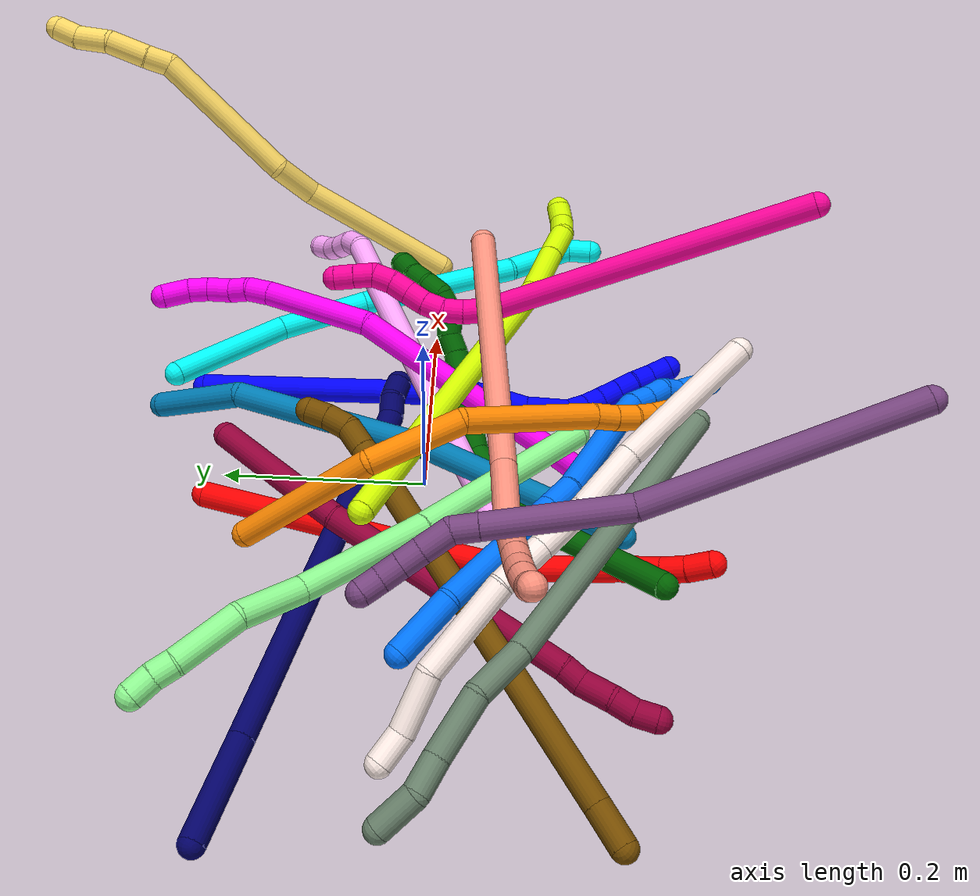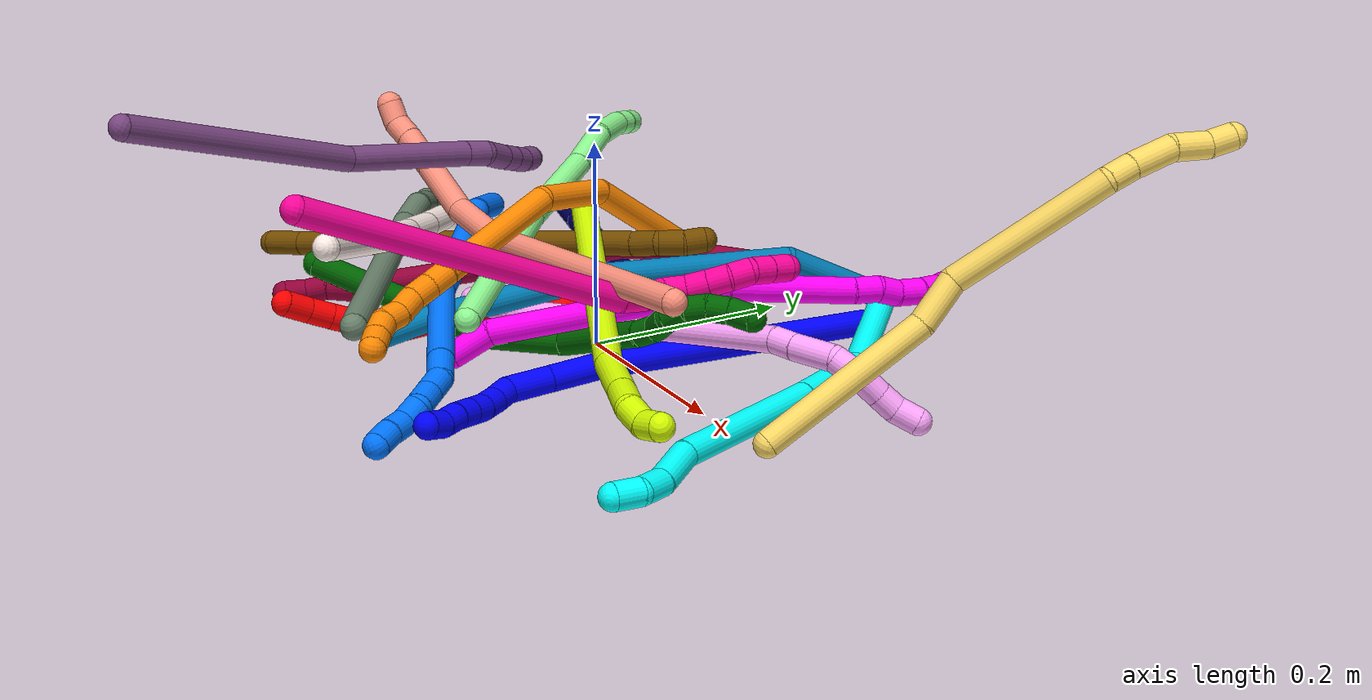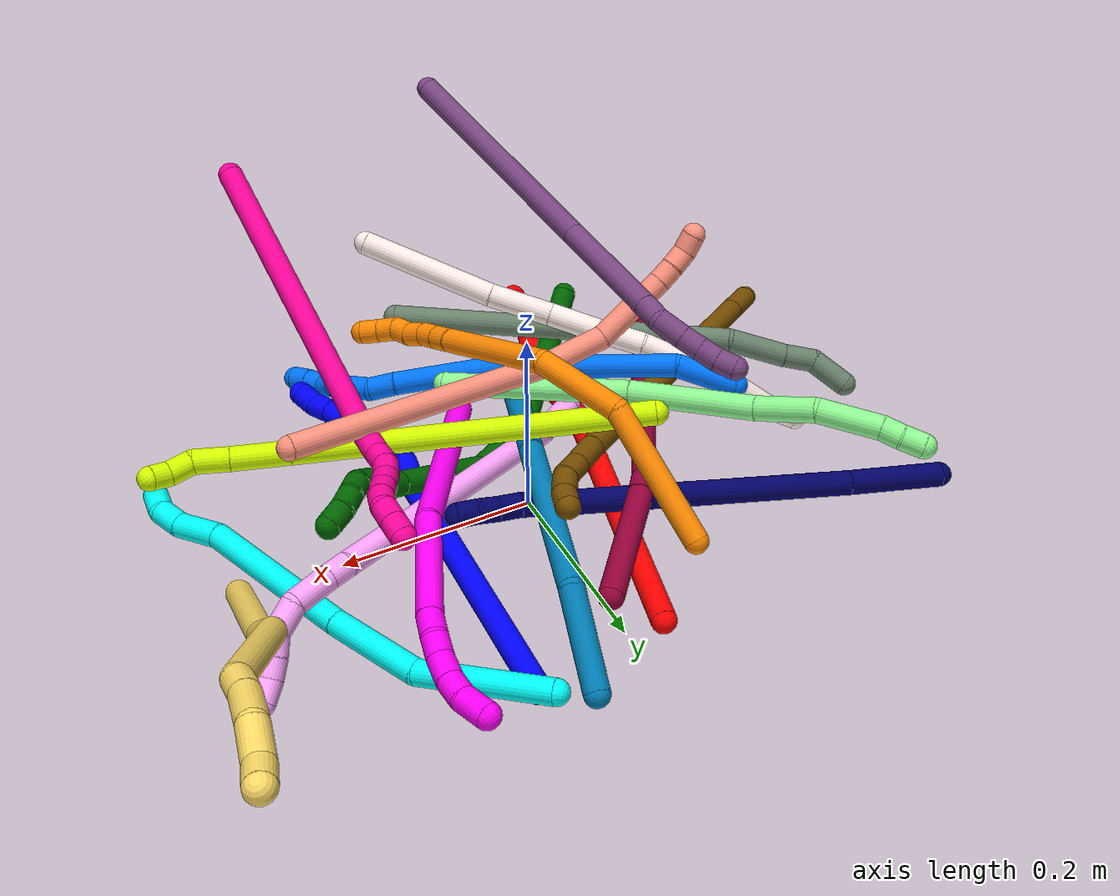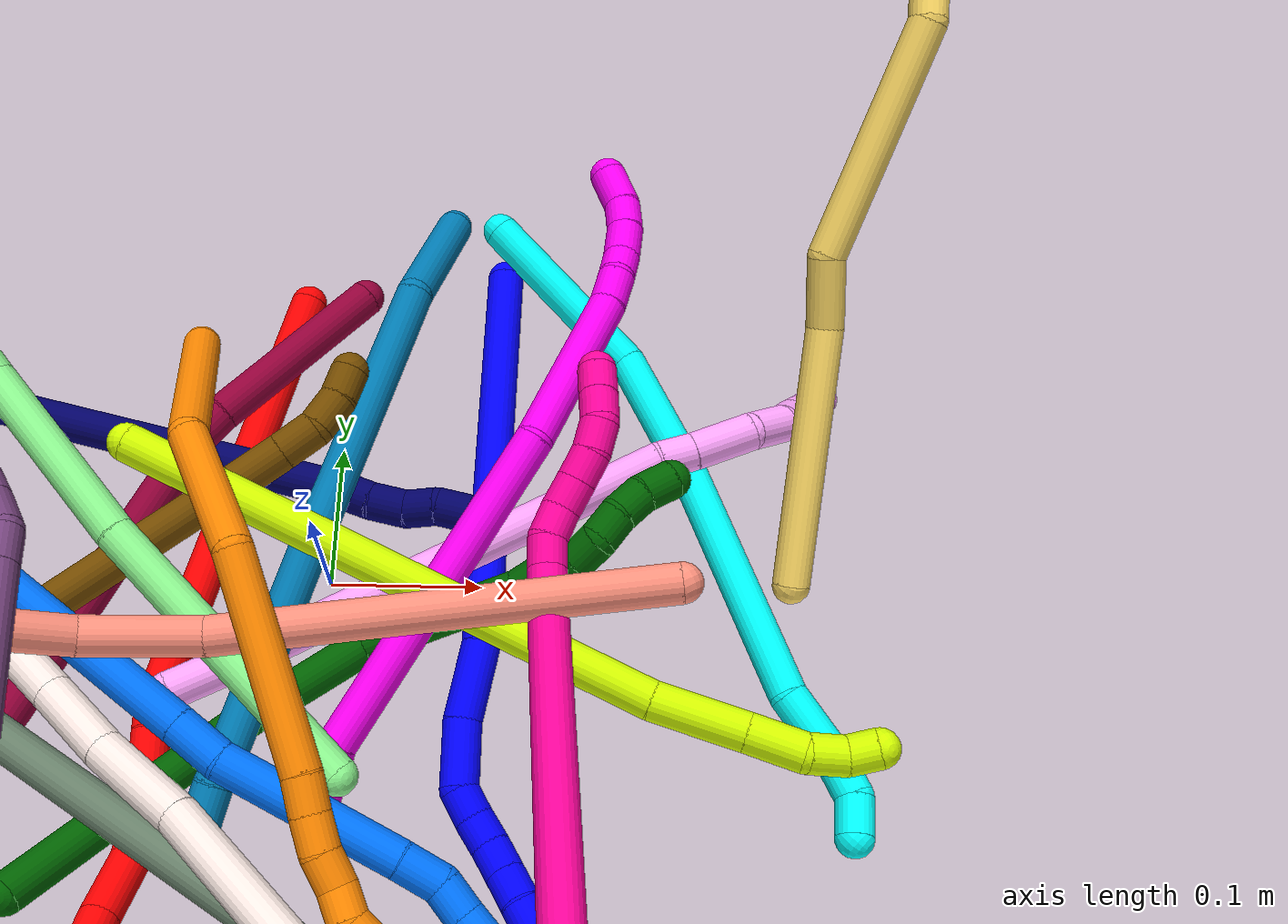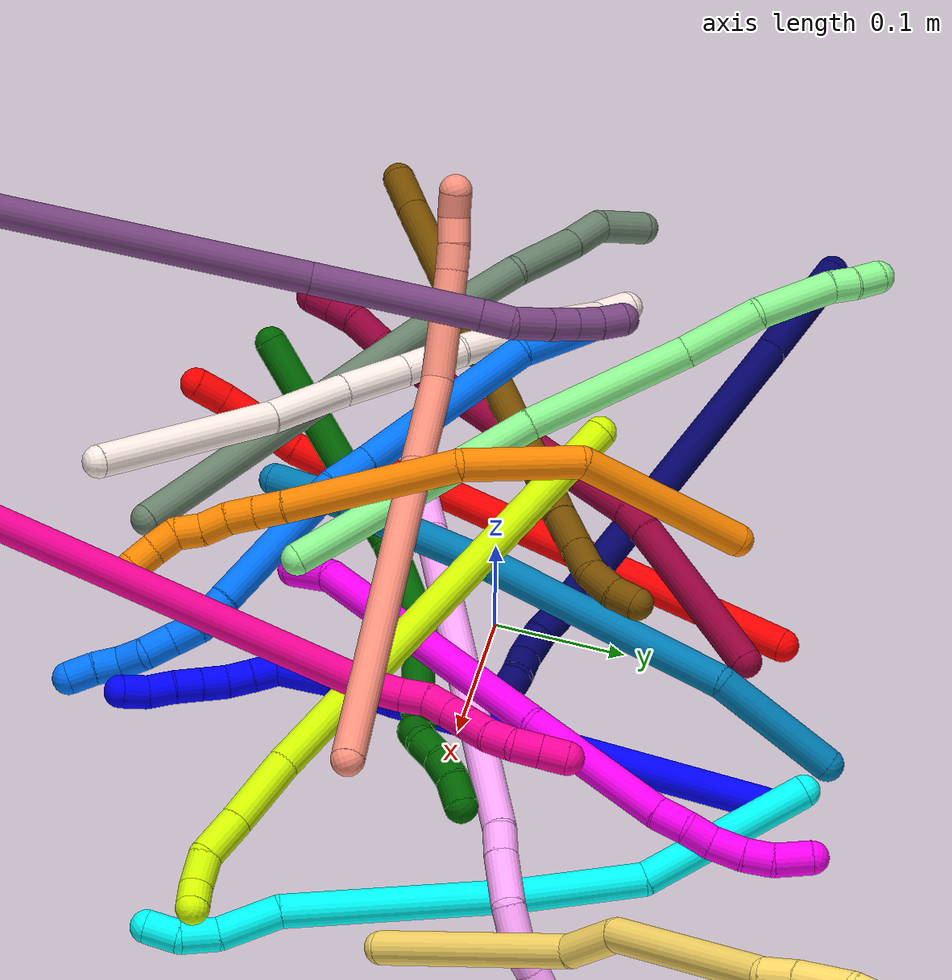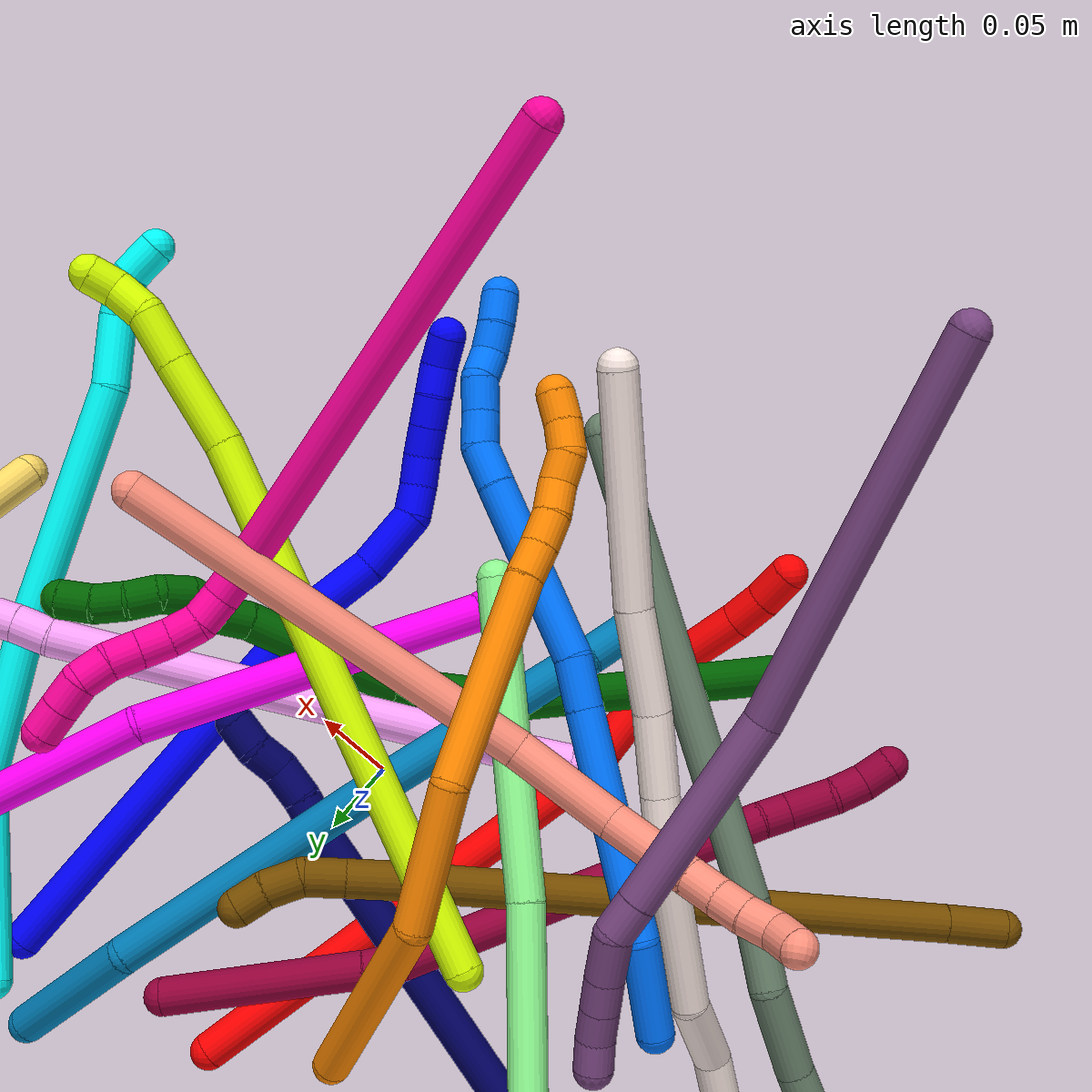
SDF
<sdf version="1.7">
 <world name="default">
  <plugin name="TubeGeneratorPlugin" filename="libtube_generator_plugin.so"/>
  <model name="photoneo_s_sensor">
   <static>1</static>
   <pose>0 0 2 1.57079 1.57079 3.14159</pose>
   <link name="link">
    <inertial><mass>0.1</mass></inertial>
    <sensor name="sensor" type="depth">
     <update_rate>30</update_rate>
     <camera>
      <horizontal_fov>1.22</horizontal_fov>
      <image><width>1920</width><height>1200</height><format>B8G8R8</format></image>
      <clip><near>0.1</near><far>4</far></clip>
      <depth_camera><output>points</output></depth_camera>
     </camera>
     <plugin name="camera_plugin" filename="libgazebo_ros_depth_camera.so">
      <baseline>0.2</baseline>
      <alwaysOn>1</alwaysOn>
      <updateRate>0.0</updateRate>
      <cameraName>camera_ir</cameraName>
      <imageTopicName>/camera/color/image_raw</imageTopicName>
      <cameraInfoTopicName>/camera/color/camera_info</cameraInfoTopicName>
      <depthImageTopicName>/camera/depth/image_raw</depthImageTopicName>
      <depthImageCameraInfoTopicName>/camera/depth/camera_info</depthImageCameraInfoTopicName>
      <pointCloudTopicName>/camera/depth/points</pointCloudTopicName>
      <frameName>fr_optical</frameName>
      <pointCloudCutoff>0.1</pointCloudCutoff>
      <pointCloudCutoffMax>2.0</pointCloudCutoffMax>
      <distortionK1>0</distortionK1>
      <distortionK2>0</distortionK2>
      <distortionK3>0</distortionK3>
      <distortionT1>0</distortionT1>
      <distortionT2>0</distortionT2>
      <CxPrime>0</CxPrime>
      <Cx>0</Cx>
      <Cy>0</Cy>
      <focalLength>0</focalLength>
      <hackBaseline>0</hackBaseline>
     </plugin>
    </sensor>
   </link>
  </model>
  <gravity>0 0 -9.8</gravity>
  <magnetic_field>6e-06 2.3e-05 -4.2e-05</magnetic_field>
  <atmosphere type="adiabatic"/>
  <physics name="default_physics" default="0" type="ode">
   <max_step_size>0.003</max_step_size>
   <real_time_factor>1</real_time_factor>
   <real_time_update_rate>1000</real_time_update_rate>
   <max_contacts>10000</max_contacts>
   <ode>
    <solver>
     <type>quick</type>
     <iters>100</iters>
     <sor>1.3</sor>
     <use_dynamic_moi_rescaling>0</use_dynamic_moi_rescaling>
    </solver>
    <constraints>
     <contact_max_correcting_vel>0</contact_max_correcting_vel>
     <contact_surface_layer>0.001</contact_surface_layer>
     <cfm>0</cfm>
     <erp>0.2</erp>
    </constraints>
   </ode>
  </physics>
  <scene><ambient>0.4 0.4 0.4 1</ambient><background>0.7 0.7 0.7 1</background><shadows>0</shadows></scene>
  <audio><device>default</device></audio>
  <spherical_coordinates>
   <surface_model>EARTH_WGS84</surface_model>
   <latitude_deg>0</latitude_deg>
   <longitude_deg>0</longitude_deg>
   <elevation>0</elevation>
   <heading_deg>0</heading_deg>
  </spherical_coordinates>
  <model name="bin">
   <static>1</static>
   <link name="bottom">
    <collision name="collision-bottom">
     <pose>0 0 -0.01 0 -0 0</pose>
     <geometry><box><size>0.8 0.6 0.02</size></box></geometry>
     <surface>
      <friction><ode><mu>100</mu><mu2>100</mu2></ode></friction>
      <contact><collide_bitmask>65535</collide_bitmask></contact>
     </surface>
    </collision>
   </link>
   <link name="west_wall">
    <collision name="collision-west_wall">
     <pose>-0.41 0 0.1 0 -0 0</pose>
     <geometry><box><size>0.02 0.6 0.2</size></box></geometry>
     <surface>
      <friction><ode><mu>100</mu><mu2>100</mu2></ode></friction>
      <contact><collide_bitmask>65535</collide_bitmask></contact>
     </surface>
    </collision>
   </link>
   <link name="east_wall">
    <collision name="collision-east_wall">
     <pose>0.41 0 0.1 0 -0 0</pose>
     <geometry><box><size>0.02 0.6 0.2</size></box></geometry>
     <surface>
      <friction><ode><mu>100</mu><mu2>100</mu2></ode></friction>
      <contact><collide_bitmask>65535</collide_bitmask></contact>
     </surface>
    </collision>
   </link>
   <link name="south_wall">
    <collision name="collision-south_wall">
     <pose>0 -0.31 0.1 0 -0 0</pose>
     <geometry><box><size>0.8 0.02 0.2</size></box></geometry>
     <surface>
      <friction><ode><mu>100</mu><mu2>100</mu2></ode></friction>
      <contact><collide_bitmask>65535</collide_bitmask></contact>
     </surface>
    </collision>
   </link>
   <link name="north_wall">
    <collision name="collision-north_wall">
     <pose>0 0.31 0.1 0 -0 0</pose>
     <geometry><box><size>0.8 0.02 0.2</size></box></geometry>
     <surface>
      <friction><ode><mu>100</mu><mu2>100</mu2></ode></friction>
      <contact><collide_bitmask>65535</collide_bitmask></contact>
     </surface>
    </collision>
   </link>
  </model>
  <model name="1">
   <static>0</static>
   <link name="1">
    <collision name="collision-cylinder-e_1_1_4">
     <pose>0.008289 -0.112985 -0.086522 2.22432 0.058181 0.117731</pose>
     <geometry><cylinder><radius>0.0125</radius><length>0.285099</length></cylinder></geometry>
     <surface>
      <friction><ode><mu>1.16</mu><mu2>1.16</mu2><slip1>0</slip1><slip2>0</slip2></ode></friction>
      <contact><ode><kp>1e+06</kp><kd>1</kd><max_vel>0</max_vel><min_depth>0.001</min_depth></ode></contact>
     </surface>
    </collision>
    <visual name="visual-cylinder-e_1_1_4">
     <pose>0.008289 -0.112985 -0.086522 2.22432 0.058181 0.117731</pose>
     <geometry><cylinder><radius>0.0125</radius><length>0.285099</length></cylinder></geometry>
     <material><ambient>0 0 1 1</ambient></material>
    </visual>
    <collision name="collision-cylinder-e_2_4_5">
     <pose>0.013325 -0.248405 -0.18449 2.04257 -0.128428 -0.209224</pose>
     <geometry><cylinder><radius>0.0125</radius><length>0.05079</length></cylinder></geometry>
     <surface>
      <friction><ode><mu>1.16</mu><mu2>1.16</mu2><slip1>0</slip1><slip2>0</slip2></ode></friction>
      <contact><ode><kp>1e+06</kp><kd>1</kd><max_vel>0</max_vel><min_depth>0.001</min_depth></ode></contact>
     </surface>
    </collision>
    <visual name="visual-cylinder-e_2_4_5">
     <pose>0.013325 -0.248405 -0.18449 2.04257 -0.128428 -0.209224</pose>
     <geometry><cylinder><radius>0.0125</radius><length>0.05079</length></cylinder></geometry>
     <material><ambient>0 0 1 1</ambient></material>
    </visual>
    <collision name="collision-cylinder-e_3_5_6">
     <pose>0.009464 -0.287806 -0.209417 2.24219 -0.028117 -0.058238</pose>
     <geometry><cylinder><radius>0.0125</radius><length>0.043359</length></cylinder></geometry>
     <surface>
      <friction><ode><mu>1.16</mu><mu2>1.16</mu2><slip1>0</slip1><slip2>0</slip2></ode></friction>
      <contact><ode><kp>1e+06</kp><kd>1</kd><max_vel>0</max_vel><min_depth>0.001</min_depth></ode></contact>
     </surface>
    </collision>
    <visual name="visual-cylinder-e_3_5_6">
     <pose>0.009464 -0.287806 -0.209417 2.24219 -0.028117 -0.058238</pose>
     <geometry><cylinder><radius>0.0125</radius><length>0.043359</length></cylinder></geometry>
     <material><ambient>0 0 1 1</ambient></material>
    </visual>
    <collision name="collision-cylinder-e_4_6_7">
     <pose>0.007946 -0.308529 -0.232167 2.75671 -0.090579 -0.457049</pose>
     <geometry><cylinder><radius>0.0125</radius><length>0.020084</length></cylinder></geometry>
     <surface>
      <friction><ode><mu>1.16</mu><mu2>1.16</mu2><slip1>0</slip1><slip2>0</slip2></ode></friction>
      <contact><ode><kp>1e+06</kp><kd>1</kd><max_vel>0</max_vel><min_depth>0.001</min_depth></ode></contact>
     </surface>
    </collision>
    <visual name="visual-cylinder-e_4_6_7">
     <pose>0.007946 -0.308529 -0.232167 2.75671 -0.090579 -0.457049</pose>
     <geometry><cylinder><radius>0.0125</radius><length>0.020084</length></cylinder></geometry>
     <material><ambient>0 0 1 1</ambient></material>
    </visual>
    <collision name="collision-cylinder-e_5_7_8">
     <pose>0.007427 -0.315554 -0.250958 2.81069 0.038687 0.230688</pose>
     <geometry><cylinder><radius>0.0125</radius><length>0.020151</length></cylinder></geometry>
     <surface>
      <friction><ode><mu>1.16</mu><mu2>1.16</mu2><slip1>0</slip1><slip2>0</slip2></ode></friction>
      <contact><ode><kp>1e+06</kp><kd>1</kd><max_vel>0</max_vel><min_depth>0.001</min_depth></ode></contact>
     </surface>
    </collision>
    <visual name="visual-cylinder-e_5_7_8">
     <pose>0.007427 -0.315554 -0.250958 2.81069 0.038687 0.230688</pose>
     <geometry><cylinder><radius>0.0125</radius><length>0.020151</length></cylinder></geometry>
     <material><ambient>0 0 1 1</ambient></material>
    </visual>
    <collision name="collision-cylinder-e_6_8_9">
     <pose>0.009699 -0.322584 -0.26961 2.75108 0.188369 0.891193</pose>
     <geometry><cylinder><radius>0.0125</radius><length>0.020101</length></cylinder></geometry>
     <surface>
      <friction><ode><mu>1.16</mu><mu2>1.16</mu2><slip1>0</slip1><slip2>0</slip2></ode></friction>
      <contact><ode><kp>1e+06</kp><kd>1</kd><max_vel>0</max_vel><min_depth>0.001</min_depth></ode></contact>
     </surface>
    </collision>
    <visual name="visual-cylinder-e_6_8_9">
     <pose>0.009699 -0.322584 -0.26961 2.75108 0.188369 0.891193</pose>
     <geometry><cylinder><radius>0.0125</radius><length>0.020101</length></cylinder></geometry>
     <material><ambient>0 0 1 1</ambient></material>
    </visual>
    <collision name="collision-cylinder-e_7_9_10">
     <pose>0.013424 -0.330161 -0.287877 2.74573 0.184041 0.862475</pose>
     <geometry><cylinder><radius>0.0125</radius><length>0.020147</length></cylinder></geometry>
     <surface>
      <friction><ode><mu>1.16</mu><mu2>1.16</mu2><slip1>0</slip1><slip2>0</slip2></ode></friction>
      <contact><ode><kp>1e+06</kp><kd>1</kd><max_vel>0</max_vel><min_depth>0.001</min_depth></ode></contact>
     </surface>
    </collision>
    <visual name="visual-cylinder-e_7_9_10">
     <pose>0.013424 -0.330161 -0.287877 2.74573 0.184041 0.862475</pose>
     <geometry><cylinder><radius>0.0125</radius><length>0.020147</length></cylinder></geometry>
     <material><ambient>0 0 1 1</ambient></material>
    </visual>
    <collision name="collision-cylinder-e_8_10_11">
     <pose>0.015634 -0.337691 -0.306334 2.76257 0.036471 0.189586</pose>
     <geometry><cylinder><radius>0.0125</radius><length>0.020077</length></cylinder></geometry>
     <surface>
      <friction><ode><mu>1.16</mu><mu2>1.16</mu2><slip1>0</slip1><slip2>0</slip2></ode></friction>
      <contact><ode><kp>1e+06</kp><kd>1</kd><max_vel>0</max_vel><min_depth>0.001</min_depth></ode></contact>
     </surface>
    </collision>
    <visual name="visual-cylinder-e_8_10_11">
     <pose>0.015634 -0.337691 -0.306334 2.76257 0.036471 0.189586</pose>
     <geometry><cylinder><radius>0.0125</radius><length>0.020077</length></cylinder></geometry>
     <material><ambient>0 0 1 1</ambient></material>
    </visual>
    <collision name="collision-cylinder-e_9_11_2">
     <pose>0.018926 -0.345883 -0.324216 2.65957 0.294039 1.08451</pose>
     <geometry><cylinder><radius>0.0125</radius><length>0.020192</length></cylinder></geometry>
     <surface>
      <friction><ode><mu>1.16</mu><mu2>1.16</mu2><slip1>0</slip1><slip2>0</slip2></ode></friction>
      <contact><ode><kp>1e+06</kp><kd>1</kd><max_vel>0</max_vel><min_depth>0.001</min_depth></ode></contact>
     </surface>
    </collision>
    <visual name="visual-cylinder-e_9_11_2">
     <pose>0.018926 -0.345883 -0.324216 2.65957 0.294039 1.08451</pose>
     <geometry><cylinder><radius>0.0125</radius><length>0.020192</length></cylinder></geometry>
     <material><ambient>0 0 1 1</ambient></material>
    </visual>
    <collision name="collision-sphere-2">
     <pose>0.021852 -0.350362 -0.332777 0 -0 0</pose>
     <geometry><sphere><radius>0.0125</radius></sphere></geometry>
     <surface>
      <friction><ode><mu>1.16</mu><mu2>1.16</mu2><slip1>0</slip1><slip2>0</slip2></ode></friction>
      <contact><ode><kp>1e+06</kp><kd>1</kd><max_vel>0</max_vel><min_depth>0.001</min_depth></ode></contact>
     </surface>
    </collision>
    <visual name="visual-sphere-2">
     <pose>0.021852 -0.350362 -0.332777 0 -0 0</pose>
     <geometry><sphere><radius>0.0125</radius></sphere></geometry>
     <material><ambient>0 0 1 1</ambient></material>
    </visual>
    <collision name="collision-sphere-11">
     <pose>0.016 -0.341403 -0.315654 0 -0 0</pose>
     <geometry><sphere><radius>0.0125</radius></sphere></geometry>
     <surface>
      <friction><ode><mu>1.16</mu><mu2>1.16</mu2><slip1>0</slip1><slip2>0</slip2></ode></friction>
      <contact><ode><kp>1e+06</kp><kd>1</kd><max_vel>0</max_vel><min_depth>0.001</min_depth></ode></contact>
     </surface>
    </collision>
    <visual name="visual-sphere-11">
     <pose>0.016 -0.341403 -0.315654 0 -0 0</pose>
     <geometry><sphere><radius>0.0125</radius></sphere></geometry>
     <material><ambient>0 0 1 1</ambient></material>
    </visual>
    <collision name="collision-sphere-10">
     <pose>0.015268 -0.333979 -0.297014 0 -0 0</pose>
     <geometry><sphere><radius>0.0125</radius></sphere></geometry>
     <surface>
      <friction><ode><mu>1.16</mu><mu2>1.16</mu2><slip1>0</slip1><slip2>0</slip2></ode></friction>
      <contact><ode><kp>1e+06</kp><kd>1</kd><max_vel>0</max_vel><min_depth>0.001</min_depth></ode></contact>
     </surface>
    </collision>
    <visual name="visual-sphere-10">
     <pose>0.015268 -0.333979 -0.297014 0 -0 0</pose>
     <geometry><sphere><radius>0.0125</radius></sphere></geometry>
     <material><ambient>0 0 1 1</ambient></material>
    </visual>
    <collision name="collision-sphere-9">
     <pose>0.011581 -0.326342 -0.278739 0 -0 0</pose>
     <geometry><sphere><radius>0.0125</radius></sphere></geometry>
     <surface>
      <friction><ode><mu>1.16</mu><mu2>1.16</mu2><slip1>0</slip1><slip2>0</slip2></ode></friction>
      <contact><ode><kp>1e+06</kp><kd>1</kd><max_vel>0</max_vel><min_depth>0.001</min_depth></ode></contact>
     </surface>
    </collision>
    <visual name="visual-sphere-9">
     <pose>0.011581 -0.326342 -0.278739 0 -0 0</pose>
     <geometry><sphere><radius>0.0125</radius></sphere></geometry>
     <material><ambient>0 0 1 1</ambient></material>
    </visual>
    <collision name="collision-sphere-4">
     <pose>0.016578 -0.22597 -0.173044 0 -0 0</pose>
     <geometry><sphere><radius>0.0125</radius></sphere></geometry>
     <surface>
      <friction><ode><mu>1.16</mu><mu2>1.16</mu2><slip1>0</slip1><slip2>0</slip2></ode></friction>
      <contact><ode><kp>1e+06</kp><kd>1</kd><max_vel>0</max_vel><min_depth>0.001</min_depth></ode></contact>
     </surface>
    </collision>
    <visual name="visual-sphere-4">
     <pose>0.016578 -0.22597 -0.173044 0 -0 0</pose>
     <geometry><sphere><radius>0.0125</radius></sphere></geometry>
     <material><ambient>0 0 1 1</ambient></material>
    </visual>
    <collision name="collision-sphere-1">
     <geometry><sphere><radius>0.0125</radius></sphere></geometry>
     <surface>
      <friction><ode><mu>1.16</mu><mu2>1.16</mu2><slip1>0</slip1><slip2>0</slip2></ode></friction>
      <contact><ode><kp>1e+06</kp><kd>1</kd><max_vel>0</max_vel><min_depth>0.001</min_depth></ode></contact>
     </surface>
    </collision>
    <visual name="visual-sphere-1">
     <geometry><sphere><radius>0.0125</radius></sphere></geometry>
     <material><ambient>0 0 1 1</ambient></material>
    </visual>
    <collision name="collision-sphere-8">
     <pose>0.007817 -0.318826 -0.26048 0 -0 0</pose>
     <geometry><sphere><radius>0.0125</radius></sphere></geometry>
     <surface>
      <friction><ode><mu>1.16</mu><mu2>1.16</mu2><slip1>0</slip1><slip2>0</slip2></ode></friction>
      <contact><ode><kp>1e+06</kp><kd>1</kd><max_vel>0</max_vel><min_depth>0.001</min_depth></ode></contact>
     </surface>
    </collision>
    <visual name="visual-sphere-8">
     <pose>0.007817 -0.318826 -0.26048 0 -0 0</pose>
     <geometry><sphere><radius>0.0125</radius></sphere></geometry>
     <material><ambient>0 0 1 1</ambient></material>
    </visual>
    <collision name="collision-sphere-5">
     <pose>0.010073 -0.270839 -0.195936 0 -0 0</pose>
     <geometry><sphere><radius>0.0125</radius></sphere></geometry>
     <surface>
      <friction><ode><mu>1.16</mu><mu2>1.16</mu2><slip1>0</slip1><slip2>0</slip2></ode></friction>
      <contact><ode><kp>1e+06</kp><kd>1</kd><max_vel>0</max_vel><min_depth>0.001</min_depth></ode></contact>
     </surface>
    </collision>
    <visual name="visual-sphere-5">
     <pose>0.010073 -0.270839 -0.195936 0 -0 0</pose>
     <geometry><sphere><radius>0.0125</radius></sphere></geometry>
     <material><ambient>0 0 1 1</ambient></material>
    </visual>
    <collision name="collision-sphere-6">
     <pose>0.008854 -0.304774 -0.222898 0 -0 0</pose>
     <geometry><sphere><radius>0.0125</radius></sphere></geometry>
     <surface>
      <friction><ode><mu>1.16</mu><mu2>1.16</mu2><slip1>0</slip1><slip2>0</slip2></ode></friction>
      <contact><ode><kp>1e+06</kp><kd>1</kd><max_vel>0</max_vel><min_depth>0.001</min_depth></ode></contact>
     </surface>
    </collision>
    <visual name="visual-sphere-6">
     <pose>0.008854 -0.304774 -0.222898 0 -0 0</pose>
     <geometry><sphere><radius>0.0125</radius></sphere></geometry>
     <material><ambient>0 0 1 1</ambient></material>
    </visual>
    <collision name="collision-sphere-7">
     <pose>0.007037 -0.312283 -0.241436 0 -0 0</pose>
     <geometry><sphere><radius>0.0125</radius></sphere></geometry>
     <surface>
      <friction><ode><mu>1.16</mu><mu2>1.16</mu2><slip1>0</slip1><slip2>0</slip2></ode></friction>
      <contact><ode><kp>1e+06</kp><kd>1</kd><max_vel>0</max_vel><min_depth>0.001</min_depth></ode></contact>
     </surface>
    </collision>
    <visual name="visual-sphere-7">
     <pose>0.007037 -0.312283 -0.241436 0 -0 0</pose>
     <geometry><sphere><radius>0.0125</radius></sphere></geometry>
     <material><ambient>0 0 1 1</ambient></material>
    </visual>
    <inertial>
     <pose>0.009842 -0.193525 -0.153507 0 -0 0</pose>
     <mass>0.5</mass>
     <inertia>
      <ixx>0.002183</ixx>
      <ixy>0</ixy>
      <ixz>0</ixz>
      <iyy>-0.000978</iyy>
      <iyz>0</iyz>
      <izz>0.001423</izz>
     </inertia>
    </inertial>
   </link>
   <pose>0.106816 0.236641 0.01171 0.015706 -1.54335 -0.683867</pose>
  </model>
  <model name="2">
   <static>0</static>
   <link name="2">
    <collision name="collision-cylinder-e_1_1_4">
     <pose>-0.011529 -0.083276 0.1289 0.573593 -0.074985 -0.022125</pose>
     <geometry><cylinder><radius>0.0125</radius><length>0.307785</length></cylinder></geometry>
     <surface>
      <friction><ode><mu>1.16</mu><mu2>1.16</mu2><slip1>0</slip1><slip2>0</slip2></ode></friction>
      <contact><ode><kp>1e+06</kp><kd>1</kd><max_vel>0</max_vel><min_depth>0.001</min_depth></ode></contact>
     </surface>
    </collision>
    <visual name="visual-cylinder-e_1_1_4">
     <pose>-0.011529 -0.083276 0.1289 0.573593 -0.074985 -0.022125</pose>
     <geometry><cylinder><radius>0.0125</radius><length>0.307785</length></cylinder></geometry>
     <material><ambient>1 0 0 1</ambient></material>
    </visual>
    <collision name="collision-cylinder-e_2_4_5">
     <pose>-0.024218 -0.174203 0.26436 0.862022 -0.114658 -0.052771</pose>
     <geometry><cylinder><radius>0.0125</radius><length>0.020292</length></cylinder></geometry>
     <surface>
      <friction><ode><mu>1.16</mu><mu2>1.16</mu2><slip1>0</slip1><slip2>0</slip2></ode></friction>
      <contact><ode><kp>1e+06</kp><kd>1</kd><max_vel>0</max_vel><min_depth>0.001</min_depth></ode></contact>
     </surface>
    </collision>
    <visual name="visual-cylinder-e_2_4_5">
     <pose>-0.024218 -0.174203 0.26436 0.862022 -0.114658 -0.052771</pose>
     <geometry><cylinder><radius>0.0125</radius><length>0.020292</length></cylinder></geometry>
     <material><ambient>1 0 0 1</ambient></material>
    </visual>
    <collision name="collision-cylinder-e_3_5_6">
     <pose>-0.031299 -0.200686 0.288983 0.806259 -0.223081 -0.095465</pose>
     <geometry><cylinder><radius>0.0125</radius><length>0.053513</length></cylinder></geometry>
     <surface>
      <friction><ode><mu>1.16</mu><mu2>1.16</mu2><slip1>0</slip1><slip2>0</slip2></ode></friction>
      <contact><ode><kp>1e+06</kp><kd>1</kd><max_vel>0</max_vel><min_depth>0.001</min_depth></ode></contact>
     </surface>
    </collision>
    <visual name="visual-cylinder-e_3_5_6">
     <pose>-0.031299 -0.200686 0.288983 0.806259 -0.223081 -0.095465</pose>
     <geometry><cylinder><radius>0.0125</radius><length>0.053513</length></cylinder></geometry>
     <material><ambient>1 0 0 1</ambient></material>
    </visual>
    <collision name="collision-cylinder-e_4_6_7">
     <pose>-0.036071 -0.230072 0.31674 0.82777 0.079874 0.0351</pose>
     <geometry><cylinder><radius>0.0125</radius><length>0.028755</length></cylinder></geometry>
     <surface>
      <friction><ode><mu>1.16</mu><mu2>1.16</mu2><slip1>0</slip1><slip2>0</slip2></ode></friction>
      <contact><ode><kp>1e+06</kp><kd>1</kd><max_vel>0</max_vel><min_depth>0.001</min_depth></ode></contact>
     </surface>
    </collision>
    <visual name="visual-cylinder-e_4_6_7">
     <pose>-0.036071 -0.230072 0.31674 0.82777 0.079874 0.0351</pose>
     <geometry><cylinder><radius>0.0125</radius><length>0.028755</length></cylinder></geometry>
     <material><ambient>1 0 0 1</ambient></material>
    </visual>
    <collision name="collision-cylinder-e_5_7_8">
     <pose>-0.02987 -0.254116 0.341417 0.733045 0.245627 0.094695</pose>
     <geometry><cylinder><radius>0.0125</radius><length>0.041565</length></cylinder></geometry>
     <surface>
      <friction><ode><mu>1.16</mu><mu2>1.16</mu2><slip1>0</slip1><slip2>0</slip2></ode></friction>
      <contact><ode><kp>1e+06</kp><kd>1</kd><max_vel>0</max_vel><min_depth>0.001</min_depth></ode></contact>
     </surface>
    </collision>
    <visual name="visual-cylinder-e_5_7_8">
     <pose>-0.02987 -0.254116 0.341417 0.733045 0.245627 0.094695</pose>
     <geometry><cylinder><radius>0.0125</radius><length>0.041565</length></cylinder></geometry>
     <material><ambient>1 0 0 1</ambient></material>
    </visual>
    <collision name="collision-cylinder-e_6_8_9">
     <pose>-0.02197 -0.276012 0.364135 0.826941 0.24418 0.107569</pose>
     <geometry><cylinder><radius>0.0125</radius><length>0.02355</length></cylinder></geometry>
     <surface>
      <friction><ode><mu>1.16</mu><mu2>1.16</mu2><slip1>0</slip1><slip2>0</slip2></ode></friction>
      <contact><ode><kp>1e+06</kp><kd>1</kd><max_vel>0</max_vel><min_depth>0.001</min_depth></ode></contact>
     </surface>
    </collision>
    <visual name="visual-cylinder-e_6_8_9">
     <pose>-0.02197 -0.276012 0.364135 0.826941 0.24418 0.107569</pose>
     <geometry><cylinder><radius>0.0125</radius><length>0.02355</length></cylinder></geometry>
     <material><ambient>1 0 0 1</ambient></material>
    </visual>
    <collision name="collision-cylinder-e_7_9_2">
     <pose>-0.016371 -0.294197 0.378755 0.957333 0.226179 0.117735</pose>
     <geometry><cylinder><radius>0.0125</radius><length>0.02454</length></cylinder></geometry>
     <surface>
      <friction><ode><mu>1.16</mu><mu2>1.16</mu2><slip1>0</slip1><slip2>0</slip2></ode></friction>
      <contact><ode><kp>1e+06</kp><kd>1</kd><max_vel>0</max_vel><min_depth>0.001</min_depth></ode></contact>
     </surface>
    </collision>
    <visual name="visual-cylinder-e_7_9_2">
     <pose>-0.016371 -0.294197 0.378755 0.957333 0.226179 0.117735</pose>
     <geometry><cylinder><radius>0.0125</radius><length>0.02454</length></cylinder></geometry>
     <material><ambient>1 0 0 1</ambient></material>
    </visual>
    <collision name="collision-sphere-2">
     <pose>-0.01362 -0.303974 0.385639 0 -0 0</pose>
     <geometry><sphere><radius>0.0125</radius></sphere></geometry>
     <surface>
      <friction><ode><mu>1.16</mu><mu2>1.16</mu2><slip1>0</slip1><slip2>0</slip2></ode></friction>
      <contact><ode><kp>1e+06</kp><kd>1</kd><max_vel>0</max_vel><min_depth>0.001</min_depth></ode></contact>
     </surface>
    </collision>
    <visual name="visual-sphere-2">
     <pose>-0.01362 -0.303974 0.385639 0 -0 0</pose>
     <geometry><sphere><radius>0.0125</radius></sphere></geometry>
     <material><ambient>1 0 0 1</ambient></material>
    </visual>
    <collision name="collision-sphere-9">
     <pose>-0.019123 -0.28442 0.371872 0 -0 0</pose>
     <geometry><sphere><radius>0.0125</radius></sphere></geometry>
     <surface>
      <friction><ode><mu>1.16</mu><mu2>1.16</mu2><slip1>0</slip1><slip2>0</slip2></ode></friction>
      <contact><ode><kp>1e+06</kp><kd>1</kd><max_vel>0</max_vel><min_depth>0.001</min_depth></ode></contact>
     </surface>
    </collision>
    <visual name="visual-sphere-9">
     <pose>-0.019123 -0.28442 0.371872 0 -0 0</pose>
     <geometry><sphere><radius>0.0125</radius></sphere></geometry>
     <material><ambient>1 0 0 1</ambient></material>
    </visual>
    <collision name="collision-sphere-4">
     <pose>-0.023058 -0.166551 0.2578 0 -0 0</pose>
     <geometry><sphere><radius>0.0125</radius></sphere></geometry>
     <surface>
      <friction><ode><mu>1.16</mu><mu2>1.16</mu2><slip1>0</slip1><slip2>0</slip2></ode></friction>
      <contact><ode><kp>1e+06</kp><kd>1</kd><max_vel>0</max_vel><min_depth>0.001</min_depth></ode></contact>
     </surface>
    </collision>
    <visual name="visual-sphere-4">
     <pose>-0.023058 -0.166551 0.2578 0 -0 0</pose>
     <geometry><sphere><radius>0.0125</radius></sphere></geometry>
     <material><ambient>1 0 0 1</ambient></material>
    </visual>
    <collision name="collision-sphere-1">
     <geometry><sphere><radius>0.0125</radius></sphere></geometry>
     <surface>
      <friction><ode><mu>1.16</mu><mu2>1.16</mu2><slip1>0</slip1><slip2>0</slip2></ode></friction>
      <contact><ode><kp>1e+06</kp><kd>1</kd><max_vel>0</max_vel><min_depth>0.001</min_depth></ode></contact>
     </surface>
    </collision>
    <visual name="visual-sphere-1">
     <geometry><sphere><radius>0.0125</radius></sphere></geometry>
     <material><ambient>1 0 0 1</ambient></material>
    </visual>
    <collision name="collision-sphere-8">
     <pose>-0.024816 -0.267605 0.356398 0 -0 0</pose>
     <geometry><sphere><radius>0.0125</radius></sphere></geometry>
     <surface>
      <friction><ode><mu>1.16</mu><mu2>1.16</mu2><slip1>0</slip1><slip2>0</slip2></ode></friction>
      <contact><ode><kp>1e+06</kp><kd>1</kd><max_vel>0</max_vel><min_depth>0.001</min_depth></ode></contact>
     </surface>
    </collision>
    <visual name="visual-sphere-8">
     <pose>-0.024816 -0.267605 0.356398 0 -0 0</pose>
     <geometry><sphere><radius>0.0125</radius></sphere></geometry>
     <material><ambient>1 0 0 1</ambient></material>
    </visual>
    <collision name="collision-sphere-5">
     <pose>-0.025379 -0.181855 0.270921 0 -0 0</pose>
     <geometry><sphere><radius>0.0125</radius></sphere></geometry>
     <surface>
      <friction><ode><mu>1.16</mu><mu2>1.16</mu2><slip1>0</slip1><slip2>0</slip2></ode></friction>
      <contact><ode><kp>1e+06</kp><kd>1</kd><max_vel>0</max_vel><min_depth>0.001</min_depth></ode></contact>
     </surface>
    </collision>
    <visual name="visual-sphere-5">
     <pose>-0.025379 -0.181855 0.270921 0 -0 0</pose>
     <geometry><sphere><radius>0.0125</radius></sphere></geometry>
     <material><ambient>1 0 0 1</ambient></material>
    </visual>
    <collision name="collision-sphere-6">
     <pose>-0.037218 -0.219518 0.307045 0 -0 0</pose>
     <geometry><sphere><radius>0.0125</radius></sphere></geometry>
     <surface>
      <friction><ode><mu>1.16</mu><mu2>1.16</mu2><slip1>0</slip1><slip2>0</slip2></ode></friction>
      <contact><ode><kp>1e+06</kp><kd>1</kd><max_vel>0</max_vel><min_depth>0.001</min_depth></ode></contact>
     </surface>
    </collision>
    <visual name="visual-sphere-6">
     <pose>-0.037218 -0.219518 0.307045 0 -0 0</pose>
     <geometry><sphere><radius>0.0125</radius></sphere></geometry>
     <material><ambient>1 0 0 1</ambient></material>
    </visual>
    <collision name="collision-sphere-7">
     <pose>-0.034924 -0.240627 0.326436 0 -0 0</pose>
     <geometry><sphere><radius>0.0125</radius></sphere></geometry>
     <surface>
      <friction><ode><mu>1.16</mu><mu2>1.16</mu2><slip1>0</slip1><slip2>0</slip2></ode></friction>
      <contact><ode><kp>1e+06</kp><kd>1</kd><max_vel>0</max_vel><min_depth>0.001</min_depth></ode></contact>
     </surface>
    </collision>
    <visual name="visual-sphere-7">
     <pose>-0.034924 -0.240627 0.326436 0 -0 0</pose>
     <geometry><sphere><radius>0.0125</radius></sphere></geometry>
     <material><ambient>1 0 0 1</ambient></material>
    </visual>
    <inertial>
     <pose>-0.017825 -0.141606 0.203342 0 -0 0</pose>
     <mass>0.5</mass>
     <inertia>
      <ixx>0.00241</ixx>
      <ixy>0</ixy>
      <ixz>0</ixz>
      <iyy>0.001997</iyy>
      <iyz>0</iyz>
      <izz>0.001557</izz>
     </inertia>
    </inertial>
   </link>
   <pose>-0.03355 0.212992 0.011556 -2.00882 -1.0654 2.75945</pose>
  </model>
  <model name="3">
   <static>0</static>
   <link name="3">
    <collision name="collision-cylinder-e_1_1_4">
     <pose>0.010481 0.00282 0.065816 -0.042819 0.157777 -0.003385</pose>
     <geometry><cylinder><radius>0.0125</radius><length>0.13341</length></cylinder></geometry>
     <surface>
      <friction><ode><mu>1.16</mu><mu2>1.16</mu2><slip1>0</slip1><slip2>0</slip2></ode></friction>
      <contact><ode><kp>1e+06</kp><kd>1</kd><max_vel>0</max_vel><min_depth>0.001</min_depth></ode></contact>
     </surface>
    </collision>
    <visual name="visual-cylinder-e_1_1_4">
     <pose>0.010481 0.00282 0.065816 -0.042819 0.157777 -0.003385</pose>
     <geometry><cylinder><radius>0.0125</radius><length>0.13341</length></cylinder></geometry>
     <material><ambient>0.003922 1 0.996078 1</ambient></material>
    </visual>
    <collision name="collision-cylinder-e_2_4_5">
     <pose>0.029431 -0.009842 0.176287 0.333735 0.177302 0.02994</pose>
     <geometry><cylinder><radius>0.0125</radius><length>0.096031</length></cylinder></geometry>
     <surface>
      <friction><ode><mu>1.16</mu><mu2>1.16</mu2><slip1>0</slip1><slip2>0</slip2></ode></friction>
      <contact><ode><kp>1e+06</kp><kd>1</kd><max_vel>0</max_vel><min_depth>0.001</min_depth></ode></contact>
     </surface>
    </collision>
    <visual name="visual-cylinder-e_2_4_5">
     <pose>0.029431 -0.009842 0.176287 0.333735 0.177302 0.02994</pose>
     <geometry><cylinder><radius>0.0125</radius><length>0.096031</length></cylinder></geometry>
     <material><ambient>0.003922 1 0.996078 1</ambient></material>
    </visual>
    <collision name="collision-cylinder-e_3_5_6">
     <pose>0.056982 -0.057463 0.297247 0.398632 0.22652 0.045945</pose>
     <geometry><cylinder><radius>0.0125</radius><length>0.169935</length></cylinder></geometry>
     <surface>
      <friction><ode><mu>1.16</mu><mu2>1.16</mu2><slip1>0</slip1><slip2>0</slip2></ode></friction>
      <contact><ode><kp>1e+06</kp><kd>1</kd><max_vel>0</max_vel><min_depth>0.001</min_depth></ode></contact>
     </surface>
    </collision>
    <visual name="visual-cylinder-e_3_5_6">
     <pose>0.056982 -0.057463 0.297247 0.398632 0.22652 0.045945</pose>
     <geometry><cylinder><radius>0.0125</radius><length>0.169935</length></cylinder></geometry>
     <material><ambient>0.003922 1 0.996078 1</ambient></material>
    </visual>
    <collision name="collision-cylinder-e_4_6_7">
     <pose>0.080971 -0.091965 0.396527 0.102551 0.209326 0.010782</pose>
     <geometry><cylinder><radius>0.0125</radius><length>0.047222</length></cylinder></geometry>
     <surface>
      <friction><ode><mu>1.16</mu><mu2>1.16</mu2><slip1>0</slip1><slip2>0</slip2></ode></friction>
      <contact><ode><kp>1e+06</kp><kd>1</kd><max_vel>0</max_vel><min_depth>0.001</min_depth></ode></contact>
     </surface>
    </collision>
    <visual name="visual-cylinder-e_4_6_7">
     <pose>0.080971 -0.091965 0.396527 0.102551 0.209326 0.010782</pose>
     <geometry><cylinder><radius>0.0125</radius><length>0.047222</length></cylinder></geometry>
     <material><ambient>0.003922 1 0.996078 1</ambient></material>
    </visual>
    <collision name="collision-cylinder-e_5_7_8">
     <pose>0.087898 -0.099561 0.432335 0.38703 0.144781 0.02842</pose>
     <geometry><cylinder><radius>0.0125</radius><length>0.028011</length></cylinder></geometry>
     <surface>
      <friction><ode><mu>1.16</mu><mu2>1.16</mu2><slip1>0</slip1><slip2>0</slip2></ode></friction>
      <contact><ode><kp>1e+06</kp><kd>1</kd><max_vel>0</max_vel><min_depth>0.001</min_depth></ode></contact>
     </surface>
    </collision>
    <visual name="visual-cylinder-e_5_7_8">
     <pose>0.087898 -0.099561 0.432335 0.38703 0.144781 0.02842</pose>
     <geometry><cylinder><radius>0.0125</radius><length>0.028011</length></cylinder></geometry>
     <material><ambient>0.003922 1 0.996078 1</ambient></material>
    </visual>
    <collision name="collision-cylinder-e_6_8_2">
     <pose>0.095056 -0.113135 0.453241 0.801964 0.416598 0.178739</pose>
     <geometry><cylinder><radius>0.0125</radius><length>0.025391</length></cylinder></geometry>
     <surface>
      <friction><ode><mu>1.16</mu><mu2>1.16</mu2><slip1>0</slip1><slip2>0</slip2></ode></friction>
      <contact><ode><kp>1e+06</kp><kd>1</kd><max_vel>0</max_vel><min_depth>0.001</min_depth></ode></contact>
     </surface>
    </collision>
    <visual name="visual-cylinder-e_6_8_2">
     <pose>0.095056 -0.113135 0.453241 0.801964 0.416598 0.178739</pose>
     <geometry><cylinder><radius>0.0125</radius><length>0.025391</length></cylinder></geometry>
     <material><ambient>0.003922 1 0.996078 1</ambient></material>
    </visual>
    <collision name="collision-sphere-2">
     <pose>0.100193 -0.12148 0.461313 0 -0 0</pose>
     <geometry><sphere><radius>0.0125</radius></sphere></geometry>
     <surface>
      <friction><ode><mu>1.16</mu><mu2>1.16</mu2><slip1>0</slip1><slip2>0</slip2></ode></friction>
      <contact><ode><kp>1e+06</kp><kd>1</kd><max_vel>0</max_vel><min_depth>0.001</min_depth></ode></contact>
     </surface>
    </collision>
    <visual name="visual-sphere-2">
     <pose>0.100193 -0.12148 0.461313 0 -0 0</pose>
     <geometry><sphere><radius>0.0125</radius></sphere></geometry>
     <material><ambient>0.003922 1 0.996078 1</ambient></material>
    </visual>
    <collision name="collision-sphere-4">
     <pose>0.020962 0.00564 0.131632 0 -0 0</pose>
     <geometry><sphere><radius>0.0125</radius></sphere></geometry>
     <surface>
      <friction><ode><mu>1.16</mu><mu2>1.16</mu2><slip1>0</slip1><slip2>0</slip2></ode></friction>
      <contact><ode><kp>1e+06</kp><kd>1</kd><max_vel>0</max_vel><min_depth>0.001</min_depth></ode></contact>
     </surface>
    </collision>
    <visual name="visual-sphere-4">
     <pose>0.020962 0.00564 0.131632 0 -0 0</pose>
     <geometry><sphere><radius>0.0125</radius></sphere></geometry>
     <material><ambient>0.003922 1 0.996078 1</ambient></material>
    </visual>
    <collision name="collision-sphere-1">
     <geometry><sphere><radius>0.0125</radius></sphere></geometry>
     <surface>
      <friction><ode><mu>1.16</mu><mu2>1.16</mu2><slip1>0</slip1><slip2>0</slip2></ode></friction>
      <contact><ode><kp>1e+06</kp><kd>1</kd><max_vel>0</max_vel><min_depth>0.001</min_depth></ode></contact>
     </surface>
    </collision>
    <visual name="visual-sphere-1">
     <geometry><sphere><radius>0.0125</radius></sphere></geometry>
     <material><ambient>0.003922 1 0.996078 1</ambient></material>
    </visual>
    <collision name="collision-sphere-8">
     <pose>0.089919 -0.104791 0.445169 0 -0 0</pose>
     <geometry><sphere><radius>0.0125</radius></sphere></geometry>
     <surface>
      <friction><ode><mu>1.16</mu><mu2>1.16</mu2><slip1>0</slip1><slip2>0</slip2></ode></friction>
      <contact><ode><kp>1e+06</kp><kd>1</kd><max_vel>0</max_vel><min_depth>0.001</min_depth></ode></contact>
     </surface>
    </collision>
    <visual name="visual-sphere-8">
     <pose>0.089919 -0.104791 0.445169 0 -0 0</pose>
     <geometry><sphere><radius>0.0125</radius></sphere></geometry>
     <material><ambient>0.003922 1 0.996078 1</ambient></material>
    </visual>
    <collision name="collision-sphere-5">
     <pose>0.037899 -0.025324 0.220942 0 -0 0</pose>
     <geometry><sphere><radius>0.0125</radius></sphere></geometry>
     <surface>
      <friction><ode><mu>1.16</mu><mu2>1.16</mu2><slip1>0</slip1><slip2>0</slip2></ode></friction>
      <contact><ode><kp>1e+06</kp><kd>1</kd><max_vel>0</max_vel><min_depth>0.001</min_depth></ode></contact>
     </surface>
    </collision>
    <visual name="visual-sphere-5">
     <pose>0.037899 -0.025324 0.220942 0 -0 0</pose>
     <geometry><sphere><radius>0.0125</radius></sphere></geometry>
     <material><ambient>0.003922 1 0.996078 1</ambient></material>
    </visual>
    <collision name="collision-sphere-6">
     <pose>0.076065 -0.089601 0.373552 0 -0 0</pose>
     <geometry><sphere><radius>0.0125</radius></sphere></geometry>
     <surface>
      <friction><ode><mu>1.16</mu><mu2>1.16</mu2><slip1>0</slip1><slip2>0</slip2></ode></friction>
      <contact><ode><kp>1e+06</kp><kd>1</kd><max_vel>0</max_vel><min_depth>0.001</min_depth></ode></contact>
     </surface>
    </collision>
    <visual name="visual-sphere-6">
     <pose>0.076065 -0.089601 0.373552 0 -0 0</pose>
     <geometry><sphere><radius>0.0125</radius></sphere></geometry>
     <material><ambient>0.003922 1 0.996078 1</ambient></material>
    </visual>
    <collision name="collision-sphere-7">
     <pose>0.085877 -0.09433 0.419501 0 -0 0</pose>
     <geometry><sphere><radius>0.0125</radius></sphere></geometry>
     <surface>
      <friction><ode><mu>1.16</mu><mu2>1.16</mu2><slip1>0</slip1><slip2>0</slip2></ode></friction>
      <contact><ode><kp>1e+06</kp><kd>1</kd><max_vel>0</max_vel><min_depth>0.001</min_depth></ode></contact>
     </surface>
    </collision>
    <visual name="visual-sphere-7">
     <pose>0.085877 -0.09433 0.419501 0 -0 0</pose>
     <geometry><sphere><radius>0.0125</radius></sphere></geometry>
     <material><ambient>0.003922 1 0.996078 1</ambient></material>
    </visual>
    <inertial>
     <pose>0.045214 -0.040676 0.237131 0 -0 0</pose>
     <mass>0.5</mass>
     <inertia>
      <ixx>0.000725</ixx>
      <ixy>0</ixy>
      <ixz>0</ixz>
      <iyy>0.000687</iyy>
      <iyz>0</iyz>
      <izz>7.1e-05</izz>
     </inertia>
    </inertial>
   </link>
   <pose>0.102983 0.262694 0.033822 -1.58261 0.98646 -2.32754</pose>
  </model>
  <model name="4">
   <static>0</static>
   <link name="4">
    <collision name="collision-cylinder-e_1_1_4">
     <pose>0.013045 0.009355 0.017803 -0.483834 0.575439 -0.145783</pose>
     <geometry><cylinder><radius>0.0125</radius><length>0.047943</length></cylinder></geometry>
     <surface>
      <friction><ode><mu>1.16</mu><mu2>1.16</mu2><slip1>0</slip1><slip2>0</slip2></ode></friction>
      <contact><ode><kp>1e+06</kp><kd>1</kd><max_vel>0</max_vel><min_depth>0.001</min_depth></ode></contact>
     </surface>
    </collision>
    <visual name="visual-cylinder-e_1_1_4">
     <pose>0.013045 0.009355 0.017803 -0.483834 0.575439 -0.145783</pose>
     <geometry><cylinder><radius>0.0125</radius><length>0.047943</length></cylinder></geometry>
     <material><ambient>1 0.65098 0.996078 1</ambient></material>
    </visual>
    <collision name="collision-cylinder-e_2_4_5">
     <pose>0.112357 0.047683 0.15177 -0.24442 0.624379 -0.079238</pose>
     <geometry><cylinder><radius>0.0125</radius><length>0.29513</length></cylinder></geometry>
     <surface>
      <friction><ode><mu>1.16</mu><mu2>1.16</mu2><slip1>0</slip1><slip2>0</slip2></ode></friction>
      <contact><ode><kp>1e+06</kp><kd>1</kd><max_vel>0</max_vel><min_depth>0.001</min_depth></ode></contact>
     </surface>
    </collision>
    <visual name="visual-cylinder-e_2_4_5">
     <pose>0.112357 0.047683 0.15177 -0.24442 0.624379 -0.079238</pose>
     <geometry><cylinder><radius>0.0125</radius><length>0.29513</length></cylinder></geometry>
     <material><ambient>1 0.65098 0.996078 1</ambient></material>
    </visual>
    <collision name="collision-cylinder-e_3_5_6">
     <pose>0.206387 0.080417 0.275436 -0.464875 0.74667 -0.184917</pose>
     <geometry><cylinder><radius>0.0125</radius><length>0.022865</length></cylinder></geometry>
     <surface>
      <friction><ode><mu>1.16</mu><mu2>1.16</mu2><slip1>0</slip1><slip2>0</slip2></ode></friction>
      <contact><ode><kp>1e+06</kp><kd>1</kd><max_vel>0</max_vel><min_depth>0.001</min_depth></ode></contact>
     </surface>
    </collision>
    <visual name="visual-cylinder-e_3_5_6">
     <pose>0.206387 0.080417 0.275436 -0.464875 0.74667 -0.184917</pose>
     <geometry><cylinder><radius>0.0125</radius><length>0.022865</length></cylinder></geometry>
     <material><ambient>1 0.65098 0.996078 1</ambient></material>
    </visual>
    <collision name="collision-cylinder-e_4_6_7">
     <pose>0.227115 0.090931 0.297751 -0.427641 0.672422 -0.151481</pose>
     <geometry><cylinder><radius>0.0125</radius><length>0.041623</length></cylinder></geometry>
     <surface>
      <friction><ode><mu>1.16</mu><mu2>1.16</mu2><slip1>0</slip1><slip2>0</slip2></ode></friction>
      <contact><ode><kp>1e+06</kp><kd>1</kd><max_vel>0</max_vel><min_depth>0.001</min_depth></ode></contact>
     </surface>
    </collision>
    <visual name="visual-cylinder-e_4_6_7">
     <pose>0.227115 0.090931 0.297751 -0.427641 0.672422 -0.151481</pose>
     <geometry><cylinder><radius>0.0125</radius><length>0.041623</length></cylinder></geometry>
     <material><ambient>1 0.65098 0.996078 1</ambient></material>
    </visual>
    <collision name="collision-cylinder-e_5_7_8">
     <pose>0.246563 0.108469 0.320729 -0.922954 0.447014 -0.225117</pose>
     <geometry><cylinder><radius>0.0125</radius><length>0.030003</length></cylinder></geometry>
     <surface>
      <friction><ode><mu>1.16</mu><mu2>1.16</mu2><slip1>0</slip1><slip2>0</slip2></ode></friction>
      <contact><ode><kp>1e+06</kp><kd>1</kd><max_vel>0</max_vel><min_depth>0.001</min_depth></ode></contact>
     </surface>
    </collision>
    <visual name="visual-cylinder-e_5_7_8">
     <pose>0.246563 0.108469 0.320729 -0.922954 0.447014 -0.225117</pose>
     <geometry><cylinder><radius>0.0125</radius><length>0.030003</length></cylinder></geometry>
     <material><ambient>1 0.65098 0.996078 1</ambient></material>
    </visual>
    <collision name="collision-cylinder-e_6_8_9">
     <pose>0.253145 0.128375 0.33302 -1.14578 0.009743 -0.006285</pose>
     <geometry><cylinder><radius>0.0125</radius><length>0.02002</length></cylinder></geometry>
     <surface>
      <friction><ode><mu>1.16</mu><mu2>1.16</mu2><slip1>0</slip1><slip2>0</slip2></ode></friction>
      <contact><ode><kp>1e+06</kp><kd>1</kd><max_vel>0</max_vel><min_depth>0.001</min_depth></ode></contact>
     </surface>
    </collision>
    <visual name="visual-cylinder-e_6_8_9">
     <pose>0.253145 0.128375 0.33302 -1.14578 0.009743 -0.006285</pose>
     <geometry><cylinder><radius>0.0125</radius><length>0.02002</length></cylinder></geometry>
     <material><ambient>1 0.65098 0.996078 1</ambient></material>
    </visual>
    <collision name="collision-cylinder-e_7_9_10">
     <pose>0.254466 0.146401 0.341674 -1.10058 0.121828 -0.0748</pose>
     <geometry><cylinder><radius>0.0125</radius><length>0.020132</length></cylinder></geometry>
     <surface>
      <friction><ode><mu>1.16</mu><mu2>1.16</mu2><slip1>0</slip1><slip2>0</slip2></ode></friction>
      <contact><ode><kp>1e+06</kp><kd>1</kd><max_vel>0</max_vel><min_depth>0.001</min_depth></ode></contact>
     </surface>
    </collision>
    <visual name="visual-cylinder-e_7_9_10">
     <pose>0.254466 0.146401 0.341674 -1.10058 0.121828 -0.0748</pose>
     <geometry><cylinder><radius>0.0125</radius><length>0.020132</length></cylinder></geometry>
     <material><ambient>1 0.65098 0.996078 1</ambient></material>
    </visual>
    <collision name="collision-cylinder-e_8_10_2">
     <pose>0.258034 0.163354 0.353544 -0.831029 0.211995 -0.093816</pose>
     <geometry><cylinder><radius>0.0125</radius><length>0.022284</length></cylinder></geometry>
     <surface>
      <friction><ode><mu>1.16</mu><mu2>1.16</mu2><slip1>0</slip1><slip2>0</slip2></ode></friction>
      <contact><ode><kp>1e+06</kp><kd>1</kd><max_vel>0</max_vel><min_depth>0.001</min_depth></ode></contact>
     </surface>
    </collision>
    <visual name="visual-cylinder-e_8_10_2">
     <pose>0.258034 0.163354 0.353544 -0.831029 0.211995 -0.093816</pose>
     <geometry><cylinder><radius>0.0125</radius><length>0.022284</length></cylinder></geometry>
     <material><ambient>1 0.65098 0.996078 1</ambient></material>
    </visual>
    <collision name="collision-sphere-2">
     <pose>0.260378 0.171399 0.360887 0 -0 0</pose>
     <geometry><sphere><radius>0.0125</radius></sphere></geometry>
     <surface>
      <friction><ode><mu>1.16</mu><mu2>1.16</mu2><slip1>0</slip1><slip2>0</slip2></ode></friction>
      <contact><ode><kp>1e+06</kp><kd>1</kd><max_vel>0</max_vel><min_depth>0.001</min_depth></ode></contact>
     </surface>
    </collision>
    <visual name="visual-sphere-2">
     <pose>0.260378 0.171399 0.360887 0 -0 0</pose>
     <geometry><sphere><radius>0.0125</radius></sphere></geometry>
     <material><ambient>1 0.65098 0.996078 1</ambient></material>
    </visual>
    <collision name="collision-sphere-10">
     <pose>0.255689 0.155308 0.346201 0 -0 0</pose>
     <geometry><sphere><radius>0.0125</radius></sphere></geometry>
     <surface>
      <friction><ode><mu>1.16</mu><mu2>1.16</mu2><slip1>0</slip1><slip2>0</slip2></ode></friction>
      <contact><ode><kp>1e+06</kp><kd>1</kd><max_vel>0</max_vel><min_depth>0.001</min_depth></ode></contact>
     </surface>
    </collision>
    <visual name="visual-sphere-10">
     <pose>0.255689 0.155308 0.346201 0 -0 0</pose>
     <geometry><sphere><radius>0.0125</radius></sphere></geometry>
     <material><ambient>1 0.65098 0.996078 1</ambient></material>
    </visual>
    <collision name="collision-sphere-9">
     <pose>0.253243 0.137494 0.337147 0 -0 0</pose>
     <geometry><sphere><radius>0.0125</radius></sphere></geometry>
     <surface>
      <friction><ode><mu>1.16</mu><mu2>1.16</mu2><slip1>0</slip1><slip2>0</slip2></ode></friction>
      <contact><ode><kp>1e+06</kp><kd>1</kd><max_vel>0</max_vel><min_depth>0.001</min_depth></ode></contact>
     </surface>
    </collision>
    <visual name="visual-sphere-9">
     <pose>0.253243 0.137494 0.337147 0 -0 0</pose>
     <geometry><sphere><radius>0.0125</radius></sphere></geometry>
     <material><ambient>1 0.65098 0.996078 1</ambient></material>
    </visual>
    <collision name="collision-sphere-4">
     <pose>0.026091 0.01871 0.035606 0 -0 0</pose>
     <geometry><sphere><radius>0.0125</radius></sphere></geometry>
     <surface>
      <friction><ode><mu>1.16</mu><mu2>1.16</mu2><slip1>0</slip1><slip2>0</slip2></ode></friction>
      <contact><ode><kp>1e+06</kp><kd>1</kd><max_vel>0</max_vel><min_depth>0.001</min_depth></ode></contact>
     </surface>
    </collision>
    <visual name="visual-sphere-4">
     <pose>0.026091 0.01871 0.035606 0 -0 0</pose>
     <geometry><sphere><radius>0.0125</radius></sphere></geometry>
     <material><ambient>1 0.65098 0.996078 1</ambient></material>
    </visual>
    <collision name="collision-sphere-1">
     <geometry><sphere><radius>0.0125</radius></sphere></geometry>
     <surface>
      <friction><ode><mu>1.16</mu><mu2>1.16</mu2><slip1>0</slip1><slip2>0</slip2></ode></friction>
      <contact><ode><kp>1e+06</kp><kd>1</kd><max_vel>0</max_vel><min_depth>0.001</min_depth></ode></contact>
     </surface>
    </collision>
    <visual name="visual-sphere-1">
     <geometry><sphere><radius>0.0125</radius></sphere></geometry>
     <material><ambient>1 0.65098 0.996078 1</ambient></material>
    </visual>
    <collision name="collision-sphere-8">
     <pose>0.253048 0.119256 0.328893 0 -0 0</pose>
     <geometry><sphere><radius>0.0125</radius></sphere></geometry>
     <surface>
      <friction><ode><mu>1.16</mu><mu2>1.16</mu2><slip1>0</slip1><slip2>0</slip2></ode></friction>
      <contact><ode><kp>1e+06</kp><kd>1</kd><max_vel>0</max_vel><min_depth>0.001</min_depth></ode></contact>
     </surface>
    </collision>
    <visual name="visual-sphere-8">
     <pose>0.253048 0.119256 0.328893 0 -0 0</pose>
     <geometry><sphere><radius>0.0125</radius></sphere></geometry>
     <material><ambient>1 0.65098 0.996078 1</ambient></material>
    </visual>
    <collision name="collision-sphere-5">
     <pose>0.198622 0.076655 0.267935 0 -0 0</pose>
     <geometry><sphere><radius>0.0125</radius></sphere></geometry>
     <surface>
      <friction><ode><mu>1.16</mu><mu2>1.16</mu2><slip1>0</slip1><slip2>0</slip2></ode></friction>
      <contact><ode><kp>1e+06</kp><kd>1</kd><max_vel>0</max_vel><min_depth>0.001</min_depth></ode></contact>
     </surface>
    </collision>
    <visual name="visual-sphere-5">
     <pose>0.198622 0.076655 0.267935 0 -0 0</pose>
     <geometry><sphere><radius>0.0125</radius></sphere></geometry>
     <material><ambient>1 0.65098 0.996078 1</ambient></material>
    </visual>
    <collision name="collision-sphere-6">
     <pose>0.214152 0.084178 0.282936 0 -0 0</pose>
     <geometry><sphere><radius>0.0125</radius></sphere></geometry>
     <surface>
      <friction><ode><mu>1.16</mu><mu2>1.16</mu2><slip1>0</slip1><slip2>0</slip2></ode></friction>
      <contact><ode><kp>1e+06</kp><kd>1</kd><max_vel>0</max_vel><min_depth>0.001</min_depth></ode></contact>
     </surface>
    </collision>
    <visual name="visual-sphere-6">
     <pose>0.214152 0.084178 0.282936 0 -0 0</pose>
     <geometry><sphere><radius>0.0125</radius></sphere></geometry>
     <material><ambient>1 0.65098 0.996078 1</ambient></material>
    </visual>
    <collision name="collision-sphere-7">
     <pose>0.240078 0.097683 0.312566 0 -0 0</pose>
     <geometry><sphere><radius>0.0125</radius></sphere></geometry>
     <surface>
      <friction><ode><mu>1.16</mu><mu2>1.16</mu2><slip1>0</slip1><slip2>0</slip2></ode></friction>
      <contact><ode><kp>1e+06</kp><kd>1</kd><max_vel>0</max_vel><min_depth>0.001</min_depth></ode></contact>
     </surface>
    </collision>
    <visual name="visual-sphere-7">
     <pose>0.240078 0.097683 0.312566 0 -0 0</pose>
     <geometry><sphere><radius>0.0125</radius></sphere></geometry>
     <material><ambient>1 0.65098 0.996078 1</ambient></material>
    </visual>
    <inertial>
     <pose>0.142592 0.065113 0.190767 0 -0 0</pose>
     <mass>0.5</mass>
     <inertia>
      <ixx>0.001645</ixx>
      <ixy>0</ixy>
      <ixz>0</ixz>
      <iyy>0.002003</iyy>
      <iyz>0</iyz>
      <izz>-0.001682</izz>
     </inertia>
    </inertial>
   </link>
   <pose>-0.090385 -0.086711 0.032087 -1.20314 -0.036956 -0.49263</pose>
  </model>
  <model name="5">
   <static>0</static>
   <link name="5">
    <collision name="collision-cylinder-e_1_1_4">
     <pose>-0.059439 -0.01456 -0.058732 2.89859 -0.776469 -2.56135</pose>
     <geometry><cylinder><radius>0.0125</radius><length>0.16964</length></cylinder></geometry>
     <surface>
      <friction><ode><mu>1.16</mu><mu2>1.16</mu2><slip1>0</slip1><slip2>0</slip2></ode></friction>
      <contact><ode><kp>1e+06</kp><kd>1</kd><max_vel>0</max_vel><min_depth>0.001</min_depth></ode></contact>
     </surface>
    </collision>
    <visual name="visual-cylinder-e_1_1_4">
     <pose>-0.059439 -0.01456 -0.058732 2.89859 -0.776469 -2.56135</pose>
     <geometry><cylinder><radius>0.0125</radius><length>0.16964</length></cylinder></geometry>
     <material><ambient>1 0.858824 0.4 1</ambient></material>
    </visual>
    <collision name="collision-cylinder-e_2_4_5">
     <pose>-0.132294 -0.027677 -0.136639 -3.06649 -0.609203 2.90372</pose>
     <geometry><cylinder><radius>0.0125</radius><length>0.046894</length></cylinder></geometry>
     <surface>
      <friction><ode><mu>1.16</mu><mu2>1.16</mu2><slip1>0</slip1><slip2>0</slip2></ode></friction>
      <contact><ode><kp>1e+06</kp><kd>1</kd><max_vel>0</max_vel><min_depth>0.001</min_depth></ode></contact>
     </surface>
    </collision>
    <visual name="visual-cylinder-e_2_4_5">
     <pose>-0.132294 -0.027677 -0.136639 -3.06649 -0.609203 2.90372</pose>
     <geometry><cylinder><radius>0.0125</radius><length>0.046894</length></cylinder></geometry>
     <material><ambient>1 0.858824 0.4 1</ambient></material>
    </visual>
    <collision name="collision-cylinder-e_3_5_6">
     <pose>-0.185694 -0.054897 -0.2169 2.70287 -0.534925 -1.77563</pose>
     <geometry><cylinder><radius>0.0125</radius><length>0.156865</length></cylinder></geometry>
     <surface>
      <friction><ode><mu>1.16</mu><mu2>1.16</mu2><slip1>0</slip1><slip2>0</slip2></ode></friction>
      <contact><ode><kp>1e+06</kp><kd>1</kd><max_vel>0</max_vel><min_depth>0.001</min_depth></ode></contact>
     </surface>
    </collision>
    <visual name="visual-cylinder-e_3_5_6">
     <pose>-0.185694 -0.054897 -0.2169 2.70287 -0.534925 -1.77563</pose>
     <geometry><cylinder><radius>0.0125</radius><length>0.156865</length></cylinder></geometry>
     <material><ambient>1 0.858824 0.4 1</ambient></material>
    </visual>
    <collision name="collision-cylinder-e_4_6_7">
     <pose>-0.236404 -0.086017 -0.284824 2.79662 -0.975362 -2.50687</pose>
     <geometry><cylinder><radius>0.0125</radius><length>0.025913</length></cylinder></geometry>
     <surface>
      <friction><ode><mu>1.16</mu><mu2>1.16</mu2><slip1>0</slip1><slip2>0</slip2></ode></friction>
      <contact><ode><kp>1e+06</kp><kd>1</kd><max_vel>0</max_vel><min_depth>0.001</min_depth></ode></contact>
     </surface>
    </collision>
    <visual name="visual-cylinder-e_4_6_7">
     <pose>-0.236404 -0.086017 -0.284824 2.79662 -0.975362 -2.50687</pose>
     <geometry><cylinder><radius>0.0125</radius><length>0.025913</length></cylinder></geometry>
     <material><ambient>1 0.858824 0.4 1</ambient></material>
    </visual>
    <collision name="collision-cylinder-e_5_7_8">
     <pose>-0.263601 -0.094636 -0.302603 2.62867 -0.919454 -2.16741</pose>
     <geometry><cylinder><radius>0.0125</radius><length>0.041421</length></cylinder></geometry>
     <surface>
      <friction><ode><mu>1.16</mu><mu2>1.16</mu2><slip1>0</slip1><slip2>0</slip2></ode></friction>
      <contact><ode><kp>1e+06</kp><kd>1</kd><max_vel>0</max_vel><min_depth>0.001</min_depth></ode></contact>
     </surface>
    </collision>
    <visual name="visual-cylinder-e_5_7_8">
     <pose>-0.263601 -0.094636 -0.302603 2.62867 -0.919454 -2.16741</pose>
     <geometry><cylinder><radius>0.0125</radius><length>0.041421</length></cylinder></geometry>
     <material><ambient>1 0.858824 0.4 1</ambient></material>
    </visual>
    <collision name="collision-cylinder-e_6_8_9">
     <pose>-0.29533 -0.10876 -0.317778 2.05963 -1.037 -1.51925</pose>
     <geometry><cylinder><radius>0.0125</radius><length>0.035448</length></cylinder></geometry>
     <surface>
      <friction><ode><mu>1.16</mu><mu2>1.16</mu2><slip1>0</slip1><slip2>0</slip2></ode></friction>
      <contact><ode><kp>1e+06</kp><kd>1</kd><max_vel>0</max_vel><min_depth>0.001</min_depth></ode></contact>
     </surface>
    </collision>
    <visual name="visual-cylinder-e_6_8_9">
     <pose>-0.29533 -0.10876 -0.317778 2.05963 -1.037 -1.51925</pose>
     <geometry><cylinder><radius>0.0125</radius><length>0.035448</length></cylinder></geometry>
     <material><ambient>1 0.858824 0.4 1</ambient></material>
    </visual>
    <collision name="collision-cylinder-e_7_9_2">
     <pose>-0.319538 -0.121709 -0.328084 2.45391 -0.850304 -1.80334</pose>
     <geometry><cylinder><radius>0.0125</radius><length>0.023818</length></cylinder></geometry>
     <surface>
      <friction><ode><mu>1.16</mu><mu2>1.16</mu2><slip1>0</slip1><slip2>0</slip2></ode></friction>
      <contact><ode><kp>1e+06</kp><kd>1</kd><max_vel>0</max_vel><min_depth>0.001</min_depth></ode></contact>
     </surface>
    </collision>
    <visual name="visual-cylinder-e_7_9_2">
     <pose>-0.319538 -0.121709 -0.328084 2.45391 -0.850304 -1.80334</pose>
     <geometry><cylinder><radius>0.0125</radius><length>0.023818</length></cylinder></geometry>
     <material><ambient>1 0.858824 0.4 1</ambient></material>
    </visual>
    <collision name="collision-sphere-2">
     <pose>-0.328488 -0.126696 -0.334156 0 -0 0</pose>
     <geometry><sphere><radius>0.0125</radius></sphere></geometry>
     <surface>
      <friction><ode><mu>1.16</mu><mu2>1.16</mu2><slip1>0</slip1><slip2>0</slip2></ode></friction>
      <contact><ode><kp>1e+06</kp><kd>1</kd><max_vel>0</max_vel><min_depth>0.001</min_depth></ode></contact>
     </surface>
    </collision>
    <visual name="visual-sphere-2">
     <pose>-0.328488 -0.126696 -0.334156 0 -0 0</pose>
     <geometry><sphere><radius>0.0125</radius></sphere></geometry>
     <material><ambient>1 0.858824 0.4 1</ambient></material>
    </visual>
    <collision name="collision-sphere-9">
     <pose>-0.310589 -0.116722 -0.322013 0 -0 0</pose>
     <geometry><sphere><radius>0.0125</radius></sphere></geometry>
     <surface>
      <friction><ode><mu>1.16</mu><mu2>1.16</mu2><slip1>0</slip1><slip2>0</slip2></ode></friction>
      <contact><ode><kp>1e+06</kp><kd>1</kd><max_vel>0</max_vel><min_depth>0.001</min_depth></ode></contact>
     </surface>
    </collision>
    <visual name="visual-sphere-9">
     <pose>-0.310589 -0.116722 -0.322013 0 -0 0</pose>
     <geometry><sphere><radius>0.0125</radius></sphere></geometry>
     <material><ambient>1 0.858824 0.4 1</ambient></material>
    </visual>
    <collision name="collision-sphere-4">
     <pose>-0.118878 -0.02912 -0.117464 0 -0 0</pose>
     <geometry><sphere><radius>0.0125</radius></sphere></geometry>
     <surface>
      <friction><ode><mu>1.16</mu><mu2>1.16</mu2><slip1>0</slip1><slip2>0</slip2></ode></friction>
      <contact><ode><kp>1e+06</kp><kd>1</kd><max_vel>0</max_vel><min_depth>0.001</min_depth></ode></contact>
     </surface>
    </collision>
    <visual name="visual-sphere-4">
     <pose>-0.118878 -0.02912 -0.117464 0 -0 0</pose>
     <geometry><sphere><radius>0.0125</radius></sphere></geometry>
     <material><ambient>1 0.858824 0.4 1</ambient></material>
    </visual>
    <collision name="collision-sphere-1">
     <geometry><sphere><radius>0.0125</radius></sphere></geometry>
     <surface>
      <friction><ode><mu>1.16</mu><mu2>1.16</mu2><slip1>0</slip1><slip2>0</slip2></ode></friction>
      <contact><ode><kp>1e+06</kp><kd>1</kd><max_vel>0</max_vel><min_depth>0.001</min_depth></ode></contact>
     </surface>
    </collision>
    <visual name="visual-sphere-1">
     <geometry><sphere><radius>0.0125</radius></sphere></geometry>
     <material><ambient>1 0.858824 0.4 1</ambient></material>
    </visual>
    <collision name="collision-sphere-8">
     <pose>-0.280072 -0.100798 -0.313543 0 -0 0</pose>
     <geometry><sphere><radius>0.0125</radius></sphere></geometry>
     <surface>
      <friction><ode><mu>1.16</mu><mu2>1.16</mu2><slip1>0</slip1><slip2>0</slip2></ode></friction>
      <contact><ode><kp>1e+06</kp><kd>1</kd><max_vel>0</max_vel><min_depth>0.001</min_depth></ode></contact>
     </surface>
    </collision>
    <visual name="visual-sphere-8">
     <pose>-0.280072 -0.100798 -0.313543 0 -0 0</pose>
     <geometry><sphere><radius>0.0125</radius></sphere></geometry>
     <material><ambient>1 0.858824 0.4 1</ambient></material>
    </visual>
    <collision name="collision-sphere-5">
     <pose>-0.145711 -0.026234 -0.155814 0 -0 0</pose>
     <geometry><sphere><radius>0.0125</radius></sphere></geometry>
     <surface>
      <friction><ode><mu>1.16</mu><mu2>1.16</mu2><slip1>0</slip1><slip2>0</slip2></ode></friction>
      <contact><ode><kp>1e+06</kp><kd>1</kd><max_vel>0</max_vel><min_depth>0.001</min_depth></ode></contact>
     </surface>
    </collision>
    <visual name="visual-sphere-5">
     <pose>-0.145711 -0.026234 -0.155814 0 -0 0</pose>
     <geometry><sphere><radius>0.0125</radius></sphere></geometry>
     <material><ambient>1 0.858824 0.4 1</ambient></material>
    </visual>
    <collision name="collision-sphere-6">
     <pose>-0.225678 -0.08356 -0.277986 0 -0 0</pose>
     <geometry><sphere><radius>0.0125</radius></sphere></geometry>
     <surface>
      <friction><ode><mu>1.16</mu><mu2>1.16</mu2><slip1>0</slip1><slip2>0</slip2></ode></friction>
      <contact><ode><kp>1e+06</kp><kd>1</kd><max_vel>0</max_vel><min_depth>0.001</min_depth></ode></contact>
     </surface>
    </collision>
    <visual name="visual-sphere-6">
     <pose>-0.225678 -0.08356 -0.277986 0 -0 0</pose>
     <geometry><sphere><radius>0.0125</radius></sphere></geometry>
     <material><ambient>1 0.858824 0.4 1</ambient></material>
    </visual>
    <collision name="collision-sphere-7">
     <pose>-0.247131 -0.088475 -0.291663 0 -0 0</pose>
     <geometry><sphere><radius>0.0125</radius></sphere></geometry>
     <surface>
      <friction><ode><mu>1.16</mu><mu2>1.16</mu2><slip1>0</slip1><slip2>0</slip2></ode></friction>
      <contact><ode><kp>1e+06</kp><kd>1</kd><max_vel>0</max_vel><min_depth>0.001</min_depth></ode></contact>
     </surface>
    </collision>
    <visual name="visual-sphere-7">
     <pose>-0.247131 -0.088475 -0.291663 0 -0 0</pose>
     <geometry><sphere><radius>0.0125</radius></sphere></geometry>
     <material><ambient>1 0.858824 0.4 1</ambient></material>
    </visual>
    <inertial>
     <pose>-0.161081 -0.050565 -0.178778 0 -0 0</pose>
     <mass>0.5</mass>
     <inertia>
      <ixx>-0.000786</ixx>
      <ixy>0</ixy>
      <ixz>0</ixz>
      <iyy>7.3e-05</iyy>
      <iyz>0</iyz>
      <izz>0.000647</izz>
     </inertia>
    </inertial>
   </link>
   <pose>0.303343 0.001345 0.011495 2.83795 -0.132302 -1.24428</pose>
  </model>
  <model name="6">
   <static>0</static>
   <link name="6">
    <collision name="collision-cylinder-e_1_1_4">
     <pose>0.067338 0.02896 -0.053006 -2.64155 0.839648 -2.10228</pose>
     <geometry><cylinder><radius>0.0125</radius><length>0.180918</length></cylinder></geometry>
     <surface>
      <friction><ode><mu>1.16</mu><mu2>1.16</mu2><slip1>0</slip1><slip2>0</slip2></ode></friction>
      <contact><ode><kp>1e+06</kp><kd>1</kd><max_vel>0</max_vel><min_depth>0.001</min_depth></ode></contact>
     </surface>
    </collision>
    <visual name="visual-cylinder-e_1_1_4">
     <pose>0.067338 0.02896 -0.053006 -2.64155 0.839648 -2.10228</pose>
     <geometry><cylinder><radius>0.0125</radius><length>0.180918</length></cylinder></geometry>
     <material><ambient>0 0.392157 0.003922 1</ambient></material>
    </visual>
    <collision name="collision-cylinder-e_2_4_5">
     <pose>0.174489 0.070004 -0.11119 -1.97562 1.25188 -1.66256</pose>
     <geometry><cylinder><radius>0.0125</radius><length>0.083853</length></cylinder></geometry>
     <surface>
      <friction><ode><mu>1.16</mu><mu2>1.16</mu2><slip1>0</slip1><slip2>0</slip2></ode></friction>
      <contact><ode><kp>1e+06</kp><kd>1</kd><max_vel>0</max_vel><min_depth>0.001</min_depth></ode></contact>
     </surface>
    </collision>
    <visual name="visual-cylinder-e_2_4_5">
     <pose>0.174489 0.070004 -0.11119 -1.97562 1.25188 -1.66256</pose>
     <geometry><cylinder><radius>0.0125</radius><length>0.083853</length></cylinder></geometry>
     <material><ambient>0 0.392157 0.003922 1</ambient></material>
    </visual>
    <collision name="collision-cylinder-e_3_5_6">
     <pose>0.266361 0.08673 -0.104798 -0.381644 1.33577 -0.302428</pose>
     <geometry><cylinder><radius>0.0125</radius><length>0.107063</length></cylinder></geometry>
     <surface>
      <friction><ode><mu>1.16</mu><mu2>1.16</mu2><slip1>0</slip1><slip2>0</slip2></ode></friction>
      <contact><ode><kp>1e+06</kp><kd>1</kd><max_vel>0</max_vel><min_depth>0.001</min_depth></ode></contact>
     </surface>
    </collision>
    <visual name="visual-cylinder-e_3_5_6">
     <pose>0.266361 0.08673 -0.104798 -0.381644 1.33577 -0.302428</pose>
     <geometry><cylinder><radius>0.0125</radius><length>0.107063</length></cylinder></geometry>
     <material><ambient>0 0.392157 0.003922 1</ambient></material>
    </visual>
    <collision name="collision-cylinder-e_4_6_7">
     <pose>0.327793 0.094303 -0.090663 -0.851566 1.17688 -0.587748</pose>
     <geometry><cylinder><radius>0.0125</radius><length>0.020298</length></cylinder></geometry>
     <surface>
      <friction><ode><mu>1.16</mu><mu2>1.16</mu2><slip1>0</slip1><slip2>0</slip2></ode></friction>
      <contact><ode><kp>1e+06</kp><kd>1</kd><max_vel>0</max_vel><min_depth>0.001</min_depth></ode></contact>
     </surface>
    </collision>
    <visual name="visual-cylinder-e_4_6_7">
     <pose>0.327793 0.094303 -0.090663 -0.851566 1.17688 -0.587748</pose>
     <geometry><cylinder><radius>0.0125</radius><length>0.020298</length></cylinder></geometry>
     <material><ambient>0 0.392157 0.003922 1</ambient></material>
    </visual>
    <collision name="collision-cylinder-e_5_7_8">
     <pose>0.347242 0.097735 -0.081274 -0.073385 0.97439 -0.038891</pose>
     <geometry><cylinder><radius>0.0125</radius><length>0.024361</length></cylinder></geometry>
     <surface>
      <friction><ode><mu>1.16</mu><mu2>1.16</mu2><slip1>0</slip1><slip2>0</slip2></ode></friction>
      <contact><ode><kp>1e+06</kp><kd>1</kd><max_vel>0</max_vel><min_depth>0.001</min_depth></ode></contact>
     </surface>
    </collision>
    <visual name="visual-cylinder-e_5_7_8">
     <pose>0.347242 0.097735 -0.081274 -0.073385 0.97439 -0.038891</pose>
     <geometry><cylinder><radius>0.0125</radius><length>0.024361</length></cylinder></geometry>
     <material><ambient>0 0.392157 0.003922 1</ambient></material>
    </visual>
    <collision name="collision-cylinder-e_6_8_9">
     <pose>0.365999 0.102929 -0.071322 -0.982727 0.994635 -0.565414</pose>
     <geometry><cylinder><radius>0.0125</radius><length>0.020702</length></cylinder></geometry>
     <surface>
      <friction><ode><mu>1.16</mu><mu2>1.16</mu2><slip1>0</slip1><slip2>0</slip2></ode></friction>
      <contact><ode><kp>1e+06</kp><kd>1</kd><max_vel>0</max_vel><min_depth>0.001</min_depth></ode></contact>
     </surface>
    </collision>
    <visual name="visual-cylinder-e_6_8_9">
     <pose>0.365999 0.102929 -0.071322 -0.982727 0.994635 -0.565414</pose>
     <geometry><cylinder><radius>0.0125</radius><length>0.020702</length></cylinder></geometry>
     <material><ambient>0 0.392157 0.003922 1</ambient></material>
    </visual>
    <collision name="collision-cylinder-e_7_9_10">
     <pose>0.382726 0.113534 -0.06983 -1.84076 0.919366 -1.15366</pose>
     <geometry><cylinder><radius>0.0125</radius><length>0.020238</length></cylinder></geometry>
     <surface>
      <friction><ode><mu>1.16</mu><mu2>1.16</mu2><slip1>0</slip1><slip2>0</slip2></ode></friction>
      <contact><ode><kp>1e+06</kp><kd>1</kd><max_vel>0</max_vel><min_depth>0.001</min_depth></ode></contact>
     </surface>
    </collision>
    <visual name="visual-cylinder-e_7_9_10">
     <pose>0.382726 0.113534 -0.06983 -1.84076 0.919366 -1.15366</pose>
     <geometry><cylinder><radius>0.0125</radius><length>0.020238</length></cylinder></geometry>
     <material><ambient>0 0.392157 0.003922 1</ambient></material>
    </visual>
    <collision name="collision-cylinder-e_8_10_11">
     <pose>0.399352 0.123732 -0.074987 -2.2586 0.99692 -1.71157</pose>
     <geometry><cylinder><radius>0.0125</radius><length>0.020429</length></cylinder></geometry>
     <surface>
      <friction><ode><mu>1.16</mu><mu2>1.16</mu2><slip1>0</slip1><slip2>0</slip2></ode></friction>
      <contact><ode><kp>1e+06</kp><kd>1</kd><max_vel>0</max_vel><min_depth>0.001</min_depth></ode></contact>
     </surface>
    </collision>
    <visual name="visual-cylinder-e_8_10_11">
     <pose>0.399352 0.123732 -0.074987 -2.2586 0.99692 -1.71157</pose>
     <geometry><cylinder><radius>0.0125</radius><length>0.020429</length></cylinder></geometry>
     <material><ambient>0 0.392157 0.003922 1</ambient></material>
    </visual>
    <collision name="collision-cylinder-e_9_11_2">
     <pose>0.418059 0.130088 -0.082461 -2.65902 1.15573 -2.41993</pose>
     <geometry><cylinder><radius>0.0125</radius><length>0.022138</length></cylinder></geometry>
     <surface>
      <friction><ode><mu>1.16</mu><mu2>1.16</mu2><slip1>0</slip1><slip2>0</slip2></ode></friction>
      <contact><ode><kp>1e+06</kp><kd>1</kd><max_vel>0</max_vel><min_depth>0.001</min_depth></ode></contact>
     </surface>
    </collision>
    <visual name="visual-cylinder-e_9_11_2">
     <pose>0.418059 0.130088 -0.082461 -2.65902 1.15573 -2.41993</pose>
     <geometry><cylinder><radius>0.0125</radius><length>0.022138</length></cylinder></geometry>
     <material><ambient>0 0.392157 0.003922 1</ambient></material>
    </visual>
    <collision name="collision-sphere-2">
     <pose>0.428188 0.132159 -0.086415 0 -0 0</pose>
     <geometry><sphere><radius>0.0125</radius></sphere></geometry>
     <surface>
      <friction><ode><mu>1.16</mu><mu2>1.16</mu2><slip1>0</slip1><slip2>0</slip2></ode></friction>
      <contact><ode><kp>1e+06</kp><kd>1</kd><max_vel>0</max_vel><min_depth>0.001</min_depth></ode></contact>
     </surface>
    </collision>
    <visual name="visual-sphere-2">
     <pose>0.428188 0.132159 -0.086415 0 -0 0</pose>
     <geometry><sphere><radius>0.0125</radius></sphere></geometry>
     <material><ambient>0 0.392157 0.003922 1</ambient></material>
    </visual>
    <collision name="collision-sphere-11">
     <pose>0.40793 0.128017 -0.078507 0 -0 0</pose>
     <geometry><sphere><radius>0.0125</radius></sphere></geometry>
     <surface>
      <friction><ode><mu>1.16</mu><mu2>1.16</mu2><slip1>0</slip1><slip2>0</slip2></ode></friction>
      <contact><ode><kp>1e+06</kp><kd>1</kd><max_vel>0</max_vel><min_depth>0.001</min_depth></ode></contact>
     </surface>
    </collision>
    <visual name="visual-sphere-11">
     <pose>0.40793 0.128017 -0.078507 0 -0 0</pose>
     <geometry><sphere><radius>0.0125</radius></sphere></geometry>
     <material><ambient>0 0.392157 0.003922 1</ambient></material>
    </visual>
    <collision name="collision-sphere-10">
     <pose>0.390773 0.119447 -0.071466 0 -0 0</pose>
     <geometry><sphere><radius>0.0125</radius></sphere></geometry>
     <surface>
      <friction><ode><mu>1.16</mu><mu2>1.16</mu2><slip1>0</slip1><slip2>0</slip2></ode></friction>
      <contact><ode><kp>1e+06</kp><kd>1</kd><max_vel>0</max_vel><min_depth>0.001</min_depth></ode></contact>
     </surface>
    </collision>
    <visual name="visual-sphere-10">
     <pose>0.390773 0.119447 -0.071466 0 -0 0</pose>
     <geometry><sphere><radius>0.0125</radius></sphere></geometry>
     <material><ambient>0 0.392157 0.003922 1</ambient></material>
    </visual>
    <collision name="collision-sphere-9">
     <pose>0.37468 0.107621 -0.068194 0 -0 0</pose>
     <geometry><sphere><radius>0.0125</radius></sphere></geometry>
     <surface>
      <friction><ode><mu>1.16</mu><mu2>1.16</mu2><slip1>0</slip1><slip2>0</slip2></ode></friction>
      <contact><ode><kp>1e+06</kp><kd>1</kd><max_vel>0</max_vel><min_depth>0.001</min_depth></ode></contact>
     </surface>
    </collision>
    <visual name="visual-sphere-9">
     <pose>0.37468 0.107621 -0.068194 0 -0 0</pose>
     <geometry><sphere><radius>0.0125</radius></sphere></geometry>
     <material><ambient>0 0.392157 0.003922 1</ambient></material>
    </visual>
    <collision name="collision-sphere-4">
     <pose>0.134677 0.057921 -0.106012 0 -0 0</pose>
     <geometry><sphere><radius>0.0125</radius></sphere></geometry>
     <surface>
      <friction><ode><mu>1.16</mu><mu2>1.16</mu2><slip1>0</slip1><slip2>0</slip2></ode></friction>
      <contact><ode><kp>1e+06</kp><kd>1</kd><max_vel>0</max_vel><min_depth>0.001</min_depth></ode></contact>
     </surface>
    </collision>
    <visual name="visual-sphere-4">
     <pose>0.134677 0.057921 -0.106012 0 -0 0</pose>
     <geometry><sphere><radius>0.0125</radius></sphere></geometry>
     <material><ambient>0 0.392157 0.003922 1</ambient></material>
    </visual>
    <collision name="collision-sphere-1">
     <geometry><sphere><radius>0.0125</radius></sphere></geometry>
     <surface>
      <friction><ode><mu>1.16</mu><mu2>1.16</mu2><slip1>0</slip1><slip2>0</slip2></ode></friction>
      <contact><ode><kp>1e+06</kp><kd>1</kd><max_vel>0</max_vel><min_depth>0.001</min_depth></ode></contact>
     </surface>
    </collision>
    <visual name="visual-sphere-1">
     <geometry><sphere><radius>0.0125</radius></sphere></geometry>
     <material><ambient>0 0.392157 0.003922 1</ambient></material>
    </visual>
    <collision name="collision-sphere-8">
     <pose>0.357319 0.098237 -0.074451 0 -0 0</pose>
     <geometry><sphere><radius>0.0125</radius></sphere></geometry>
     <surface>
      <friction><ode><mu>1.16</mu><mu2>1.16</mu2><slip1>0</slip1><slip2>0</slip2></ode></friction>
      <contact><ode><kp>1e+06</kp><kd>1</kd><max_vel>0</max_vel><min_depth>0.001</min_depth></ode></contact>
     </surface>
    </collision>
    <visual name="visual-sphere-8">
     <pose>0.357319 0.098237 -0.074451 0 -0 0</pose>
     <geometry><sphere><radius>0.0125</radius></sphere></geometry>
     <material><ambient>0 0.392157 0.003922 1</ambient></material>
    </visual>
    <collision name="collision-sphere-5">
     <pose>0.214301 0.082087 -0.116367 0 -0 0</pose>
     <geometry><sphere><radius>0.0125</radius></sphere></geometry>
     <surface>
      <friction><ode><mu>1.16</mu><mu2>1.16</mu2><slip1>0</slip1><slip2>0</slip2></ode></friction>
      <contact><ode><kp>1e+06</kp><kd>1</kd><max_vel>0</max_vel><min_depth>0.001</min_depth></ode></contact>
     </surface>
    </collision>
    <visual name="visual-sphere-5">
     <pose>0.214301 0.082087 -0.116367 0 -0 0</pose>
     <geometry><sphere><radius>0.0125</radius></sphere></geometry>
     <material><ambient>0 0.392157 0.003922 1</ambient></material>
    </visual>
    <collision name="collision-sphere-6">
     <pose>0.318421 0.091373 -0.093229 0 -0 0</pose>
     <geometry><sphere><radius>0.0125</radius></sphere></geometry>
     <surface>
      <friction><ode><mu>1.16</mu><mu2>1.16</mu2><slip1>0</slip1><slip2>0</slip2></ode></friction>
      <contact><ode><kp>1e+06</kp><kd>1</kd><max_vel>0</max_vel><min_depth>0.001</min_depth></ode></contact>
     </surface>
    </collision>
    <visual name="visual-sphere-6">
     <pose>0.318421 0.091373 -0.093229 0 -0 0</pose>
     <geometry><sphere><radius>0.0125</radius></sphere></geometry>
     <material><ambient>0 0.392157 0.003922 1</ambient></material>
    </visual>
    <collision name="collision-sphere-7">
     <pose>0.337164 0.097234 -0.088097 0 -0 0</pose>
     <geometry><sphere><radius>0.0125</radius></sphere></geometry>
     <surface>
      <friction><ode><mu>1.16</mu><mu2>1.16</mu2><slip1>0</slip1><slip2>0</slip2></ode></friction>
      <contact><ode><kp>1e+06</kp><kd>1</kd><max_vel>0</max_vel><min_depth>0.001</min_depth></ode></contact>
     </surface>
    </collision>
    <visual name="visual-sphere-7">
     <pose>0.337164 0.097234 -0.088097 0 -0 0</pose>
     <geometry><sphere><radius>0.0125</radius></sphere></geometry>
     <material><ambient>0 0.392157 0.003922 1</ambient></material>
    </visual>
    <inertial>
     <pose>0.20636 0.069053 -0.080401 0 -0 0</pose>
     <mass>0.5</mass>
     <inertia>
      <ixx>-0.000426</ixx>
      <ixy>0</ixy>
      <ixz>0</ixz>
      <iyy>0.000234</iyy>
      <iyz>0</iyz>
      <izz>-0.000729</izz>
     </inertia>
    </inertial>
   </link>
   <pose>-0.154588 -0.221826 0.072921 0.384717 -0.113508 0.257564</pose>
  </model>
  <model name="7">
   <static>0</static>
   <link name="7">
    <collision name="collision-cylinder-e_1_1_4">
     <pose>0.043488 -0.011115 -0.019052 2.61346 1.10139 2.31206</pose>
     <geometry><cylinder><radius>0.0125</radius><length>0.097524</length></cylinder></geometry>
     <surface>
      <friction><ode><mu>1.16</mu><mu2>1.16</mu2><slip1>0</slip1><slip2>0</slip2></ode></friction>
      <contact><ode><kp>1e+06</kp><kd>1</kd><max_vel>0</max_vel><min_depth>0.001</min_depth></ode></contact>
     </surface>
    </collision>
    <visual name="visual-cylinder-e_1_1_4">
     <pose>0.043488 -0.011115 -0.019052 2.61346 1.10139 2.31206</pose>
     <geometry><cylinder><radius>0.0125</radius><length>0.097524</length></cylinder></geometry>
     <material><ambient>0.003922 0 0.403922 1</ambient></material>
    </visual>
    <collision name="collision-cylinder-e_2_4_5">
     <pose>0.228566 -0.055564 -0.09603 2.61941 1.12979 2.34366</pose>
     <geometry><cylinder><radius>0.0125</radius><length>0.313139</length></cylinder></geometry>
     <surface>
      <friction><ode><mu>1.16</mu><mu2>1.16</mu2><slip1>0</slip1><slip2>0</slip2></ode></friction>
      <contact><ode><kp>1e+06</kp><kd>1</kd><max_vel>0</max_vel><min_depth>0.001</min_depth></ode></contact>
     </surface>
    </collision>
    <visual name="visual-cylinder-e_2_4_5">
     <pose>0.228566 -0.055564 -0.09603 2.61941 1.12979 2.34366</pose>
     <geometry><cylinder><radius>0.0125</radius><length>0.313139</length></cylinder></geometry>
     <material><ambient>0.003922 0 0.403922 1</ambient></material>
    </visual>
    <collision name="collision-cylinder-e_3_5_6">
     <pose>0.38043 -0.092451 -0.157817 2.39789 1.0986 2.00709</pose>
     <geometry><cylinder><radius>0.0125</radius><length>0.023074</length></cylinder></geometry>
     <surface>
      <friction><ode><mu>1.16</mu><mu2>1.16</mu2><slip1>0</slip1><slip2>0</slip2></ode></friction>
      <contact><ode><kp>1e+06</kp><kd>1</kd><max_vel>0</max_vel><min_depth>0.001</min_depth></ode></contact>
     </surface>
    </collision>
    <visual name="visual-cylinder-e_3_5_6">
     <pose>0.38043 -0.092451 -0.157817 2.39789 1.0986 2.00709</pose>
     <geometry><cylinder><radius>0.0125</radius><length>0.023074</length></cylinder></geometry>
     <material><ambient>0.003922 0 0.403922 1</ambient></material>
    </visual>
    <collision name="collision-cylinder-e_4_6_7">
     <pose>0.400958 -0.098664 -0.167248 2.69597 1.02896 2.37914</pose>
     <geometry><cylinder><radius>0.0125</radius><length>0.023936</length></cylinder></geometry>
     <surface>
      <friction><ode><mu>1.16</mu><mu2>1.16</mu2><slip1>0</slip1><slip2>0</slip2></ode></friction>
      <contact><ode><kp>1e+06</kp><kd>1</kd><max_vel>0</max_vel><min_depth>0.001</min_depth></ode></contact>
     </surface>
    </collision>
    <visual name="visual-cylinder-e_4_6_7">
     <pose>0.400958 -0.098664 -0.167248 2.69597 1.02896 2.37914</pose>
     <geometry><cylinder><radius>0.0125</radius><length>0.023936</length></cylinder></geometry>
     <material><ambient>0.003922 0 0.403922 1</ambient></material>
    </visual>
    <collision name="collision-cylinder-e_5_7_8">
     <pose>0.420807 -0.100182 -0.176939 -2.87134 1.15146 -2.72864</pose>
     <geometry><cylinder><radius>0.0125</radius><length>0.02101</length></cylinder></geometry>
     <surface>
      <friction><ode><mu>1.16</mu><mu2>1.16</mu2><slip1>0</slip1><slip2>0</slip2></ode></friction>
      <contact><ode><kp>1e+06</kp><kd>1</kd><max_vel>0</max_vel><min_depth>0.001</min_depth></ode></contact>
     </surface>
    </collision>
    <visual name="visual-cylinder-e_5_7_8">
     <pose>0.420807 -0.100182 -0.176939 -2.87134 1.15146 -2.72864</pose>
     <geometry><cylinder><radius>0.0125</radius><length>0.02101</length></cylinder></geometry>
     <material><ambient>0.003922 0 0.403922 1</ambient></material>
    </visual>
    <collision name="collision-cylinder-e_6_8_2">
     <pose>0.439419 -0.101461 -0.186201 2.70146 1.0086 2.37145</pose>
     <geometry><cylinder><radius>0.0125</radius><length>0.021316</length></cylinder></geometry>
     <surface>
      <friction><ode><mu>1.16</mu><mu2>1.16</mu2><slip1>0</slip1><slip2>0</slip2></ode></friction>
      <contact><ode><kp>1e+06</kp><kd>1</kd><max_vel>0</max_vel><min_depth>0.001</min_depth></ode></contact>
     </surface>
    </collision>
    <visual name="visual-cylinder-e_6_8_2">
     <pose>0.439419 -0.101461 -0.186201 2.70146 1.0086 2.37145</pose>
     <geometry><cylinder><radius>0.0125</radius><length>0.021316</length></cylinder></geometry>
     <material><ambient>0.003922 0 0.403922 1</ambient></material>
    </visual>
    <collision name="collision-sphere-2">
     <pose>0.448437 -0.103881 -0.191341 0 -0 0</pose>
     <geometry><sphere><radius>0.0125</radius></sphere></geometry>
     <surface>
      <friction><ode><mu>1.16</mu><mu2>1.16</mu2><slip1>0</slip1><slip2>0</slip2></ode></friction>
      <contact><ode><kp>1e+06</kp><kd>1</kd><max_vel>0</max_vel><min_depth>0.001</min_depth></ode></contact>
     </surface>
    </collision>
    <visual name="visual-sphere-2">
     <pose>0.448437 -0.103881 -0.191341 0 -0 0</pose>
     <geometry><sphere><radius>0.0125</radius></sphere></geometry>
     <material><ambient>0.003922 0 0.403922 1</ambient></material>
    </visual>
    <collision name="collision-sphere-4">
     <pose>0.086976 -0.022231 -0.038105 0 -0 0</pose>
     <geometry><sphere><radius>0.0125</radius></sphere></geometry>
     <surface>
      <friction><ode><mu>1.16</mu><mu2>1.16</mu2><slip1>0</slip1><slip2>0</slip2></ode></friction>
      <contact><ode><kp>1e+06</kp><kd>1</kd><max_vel>0</max_vel><min_depth>0.001</min_depth></ode></contact>
     </surface>
    </collision>
    <visual name="visual-sphere-4">
     <pose>0.086976 -0.022231 -0.038105 0 -0 0</pose>
     <geometry><sphere><radius>0.0125</radius></sphere></geometry>
     <material><ambient>0.003922 0 0.403922 1</ambient></material>
    </visual>
    <collision name="collision-sphere-1">
     <geometry><sphere><radius>0.0125</radius></sphere></geometry>
     <surface>
      <friction><ode><mu>1.16</mu><mu2>1.16</mu2><slip1>0</slip1><slip2>0</slip2></ode></friction>
      <contact><ode><kp>1e+06</kp><kd>1</kd><max_vel>0</max_vel><min_depth>0.001</min_depth></ode></contact>
     </surface>
    </collision>
    <visual name="visual-sphere-1">
     <geometry><sphere><radius>0.0125</radius></sphere></geometry>
     <material><ambient>0.003922 0 0.403922 1</ambient></material>
    </visual>
    <collision name="collision-sphere-8">
     <pose>0.430402 -0.09904 -0.181061 0 -0 0</pose>
     <geometry><sphere><radius>0.0125</radius></sphere></geometry>
     <surface>
      <friction><ode><mu>1.16</mu><mu2>1.16</mu2><slip1>0</slip1><slip2>0</slip2></ode></friction>
      <contact><ode><kp>1e+06</kp><kd>1</kd><max_vel>0</max_vel><min_depth>0.001</min_depth></ode></contact>
     </surface>
    </collision>
    <visual name="visual-sphere-8">
     <pose>0.430402 -0.09904 -0.181061 0 -0 0</pose>
     <geometry><sphere><radius>0.0125</radius></sphere></geometry>
     <material><ambient>0.003922 0 0.403922 1</ambient></material>
    </visual>
    <collision name="collision-sphere-5">
     <pose>0.370155 -0.088898 -0.153955 0 -0 0</pose>
     <geometry><sphere><radius>0.0125</radius></sphere></geometry>
     <surface>
      <friction><ode><mu>1.16</mu><mu2>1.16</mu2><slip1>0</slip1><slip2>0</slip2></ode></friction>
      <contact><ode><kp>1e+06</kp><kd>1</kd><max_vel>0</max_vel><min_depth>0.001</min_depth></ode></contact>
     </surface>
    </collision>
    <visual name="visual-sphere-5">
     <pose>0.370155 -0.088898 -0.153955 0 -0 0</pose>
     <geometry><sphere><radius>0.0125</radius></sphere></geometry>
     <material><ambient>0.003922 0 0.403922 1</ambient></material>
    </visual>
    <collision name="collision-sphere-6">
     <pose>0.390704 -0.096004 -0.161679 0 -0 0</pose>
     <geometry><sphere><radius>0.0125</radius></sphere></geometry>
     <surface>
      <friction><ode><mu>1.16</mu><mu2>1.16</mu2><slip1>0</slip1><slip2>0</slip2></ode></friction>
      <contact><ode><kp>1e+06</kp><kd>1</kd><max_vel>0</max_vel><min_depth>0.001</min_depth></ode></contact>
     </surface>
    </collision>
    <visual name="visual-sphere-6">
     <pose>0.390704 -0.096004 -0.161679 0 -0 0</pose>
     <geometry><sphere><radius>0.0125</radius></sphere></geometry>
     <material><ambient>0.003922 0 0.403922 1</ambient></material>
    </visual>
    <collision name="collision-sphere-7">
     <pose>0.411212 -0.101324 -0.172817 0 -0 0</pose>
     <geometry><sphere><radius>0.0125</radius></sphere></geometry>
     <surface>
      <friction><ode><mu>1.16</mu><mu2>1.16</mu2><slip1>0</slip1><slip2>0</slip2></ode></friction>
      <contact><ode><kp>1e+06</kp><kd>1</kd><max_vel>0</max_vel><min_depth>0.001</min_depth></ode></contact>
     </surface>
    </collision>
    <visual name="visual-sphere-7">
     <pose>0.411212 -0.101324 -0.172817 0 -0 0</pose>
     <geometry><sphere><radius>0.0125</radius></sphere></geometry>
     <material><ambient>0.003922 0 0.403922 1</ambient></material>
    </visual>
    <inertial>
     <pose>0.224795 -0.054492 -0.09452 0 -0 0</pose>
     <mass>0.5</mass>
     <inertia>
      <ixx>5.6e-05</ixx>
      <ixy>0</ixy>
      <ixz>0</ixz>
      <iyy>0.003273</iyy>
      <iyz>0</iyz>
      <izz>-0.001852</izz>
     </inertia>
    </inertial>
   </link>
   <pose>-0.387499 0.162384 0.011743 0.706288 -0.514035 -0.35595</pose>
  </model>
  <model name="8">
   <static>0</static>
   <link name="8">
    <collision name="collision-cylinder-e_1_1_4">
     <pose>-0.019337 -0.062542 0.007981 1.44387 -0.297591 -0.262462</pose>
     <geometry><cylinder><radius>0.0125</radius><length>0.131895</length></cylinder></geometry>
     <surface>
      <friction><ode><mu>1.16</mu><mu2>1.16</mu2><slip1>0</slip1><slip2>0</slip2></ode></friction>
      <contact><ode><kp>1e+06</kp><kd>1</kd><max_vel>0</max_vel><min_depth>0.001</min_depth></ode></contact>
     </surface>
    </collision>
    <visual name="visual-cylinder-e_1_1_4">
     <pose>-0.019337 -0.062542 0.007981 1.44387 -0.297591 -0.262462</pose>
     <geometry><cylinder><radius>0.0125</radius><length>0.131895</length></cylinder></geometry>
     <material><ambient>0.584314 0 0.227451 1</ambient></material>
    </visual>
    <collision name="collision-cylinder-e_2_4_5">
     <pose>-0.043222 -0.13581 0.017832 1.3983 -0.395671 -0.333964</pose>
     <geometry><cylinder><radius>0.0125</radius><length>0.023602</length></cylinder></geometry>
     <surface>
      <friction><ode><mu>1.16</mu><mu2>1.16</mu2><slip1>0</slip1><slip2>0</slip2></ode></friction>
      <contact><ode><kp>1e+06</kp><kd>1</kd><max_vel>0</max_vel><min_depth>0.001</min_depth></ode></contact>
     </surface>
    </collision>
    <visual name="visual-cylinder-e_2_4_5">
     <pose>-0.043222 -0.13581 0.017832 1.3983 -0.395671 -0.333964</pose>
     <geometry><cylinder><radius>0.0125</radius><length>0.023602</length></cylinder></geometry>
     <material><ambient>0.584314 0 0.227451 1</ambient></material>
    </visual>
    <collision name="collision-cylinder-e_3_5_6">
     <pose>-0.118779 -0.246875 0.041199 1.35973 -0.605328 -0.494548</pose>
     <geometry><cylinder><radius>0.0125</radius><length>0.249575</length></cylinder></geometry>
     <surface>
      <friction><ode><mu>1.16</mu><mu2>1.16</mu2><slip1>0</slip1><slip2>0</slip2></ode></friction>
      <contact><ode><kp>1e+06</kp><kd>1</kd><max_vel>0</max_vel><min_depth>0.001</min_depth></ode></contact>
     </surface>
    </collision>
    <visual name="visual-cylinder-e_3_5_6">
     <pose>-0.118779 -0.246875 0.041199 1.35973 -0.605328 -0.494548</pose>
     <geometry><cylinder><radius>0.0125</radius><length>0.249575</length></cylinder></geometry>
     <material><ambient>0.584314 0 0.227451 1</ambient></material>
    </visual>
    <collision name="collision-cylinder-e_4_6_7">
     <pose>-0.195686 -0.354746 0.065944 1.16388 -0.623431 -0.417821</pose>
     <geometry><cylinder><radius>0.0125</radius><length>0.020208</length></cylinder></geometry>
     <surface>
      <friction><ode><mu>1.16</mu><mu2>1.16</mu2><slip1>0</slip1><slip2>0</slip2></ode></friction>
      <contact><ode><kp>1e+06</kp><kd>1</kd><max_vel>0</max_vel><min_depth>0.001</min_depth></ode></contact>
     </surface>
    </collision>
    <visual name="visual-cylinder-e_4_6_7">
     <pose>-0.195686 -0.354746 0.065944 1.16388 -0.623431 -0.417821</pose>
     <geometry><cylinder><radius>0.0125</radius><length>0.020208</length></cylinder></geometry>
     <material><ambient>0.584314 0 0.227451 1</ambient></material>
    </visual>
    <collision name="collision-cylinder-e_5_7_8">
     <pose>-0.208377 -0.37665 0.069248 1.56684 -0.441514 -0.439827</pose>
     <geometry><cylinder><radius>0.0125</radius><length>0.03179</length></cylinder></geometry>
     <surface>
      <friction><ode><mu>1.16</mu><mu2>1.16</mu2><slip1>0</slip1><slip2>0</slip2></ode></friction>
      <contact><ode><kp>1e+06</kp><kd>1</kd><max_vel>0</max_vel><min_depth>0.001</min_depth></ode></contact>
     </surface>
    </collision>
    <visual name="visual-cylinder-e_5_7_8">
     <pose>-0.208377 -0.37665 0.069248 1.56684 -0.441514 -0.439827</pose>
     <geometry><cylinder><radius>0.0125</radius><length>0.03179</length></cylinder></geometry>
     <material><ambient>0.584314 0 0.227451 1</ambient></material>
    </visual>
    <collision name="collision-cylinder-e_6_8_9">
     <pose>-0.221758 -0.399305 0.071025 1.36596 -0.6617 -0.545</pose>
     <geometry><cylinder><radius>0.0125</radius><length>0.021448</length></cylinder></geometry>
     <surface>
      <friction><ode><mu>1.16</mu><mu2>1.16</mu2><slip1>0</slip1><slip2>0</slip2></ode></friction>
      <contact><ode><kp>1e+06</kp><kd>1</kd><max_vel>0</max_vel><min_depth>0.001</min_depth></ode></contact>
     </surface>
    </collision>
    <visual name="visual-cylinder-e_6_8_9">
     <pose>-0.221758 -0.399305 0.071025 1.36596 -0.6617 -0.545</pose>
     <geometry><cylinder><radius>0.0125</radius><length>0.021448</length></cylinder></geometry>
     <material><ambient>0.584314 0 0.227451 1</ambient></material>
    </visual>
    <collision name="collision-cylinder-e_7_9_2">
     <pose>-0.235083 -0.415881 0.071631 1.70452 -0.677749 -0.766287</pose>
     <geometry><cylinder><radius>0.0125</radius><length>0.021483</length></cylinder></geometry>
     <surface>
      <friction><ode><mu>1.16</mu><mu2>1.16</mu2><slip1>0</slip1><slip2>0</slip2></ode></friction>
      <contact><ode><kp>1e+06</kp><kd>1</kd><max_vel>0</max_vel><min_depth>0.001</min_depth></ode></contact>
     </surface>
    </collision>
    <visual name="visual-cylinder-e_7_9_2">
     <pose>-0.235083 -0.415881 0.071631 1.70452 -0.677749 -0.766287</pose>
     <geometry><cylinder><radius>0.0125</radius><length>0.021483</length></cylinder></geometry>
     <material><ambient>0.584314 0 0.227451 1</ambient></material>
    </visual>
    <collision name="collision-sphere-2">
     <pose>-0.241818 -0.424174 0.070515 0 -0 0</pose>
     <geometry><sphere><radius>0.0125</radius></sphere></geometry>
     <surface>
      <friction><ode><mu>1.16</mu><mu2>1.16</mu2><slip1>0</slip1><slip2>0</slip2></ode></friction>
      <contact><ode><kp>1e+06</kp><kd>1</kd><max_vel>0</max_vel><min_depth>0.001</min_depth></ode></contact>
     </surface>
    </collision>
    <visual name="visual-sphere-2">
     <pose>-0.241818 -0.424174 0.070515 0 -0 0</pose>
     <geometry><sphere><radius>0.0125</radius></sphere></geometry>
     <material><ambient>0.584314 0 0.227451 1</ambient></material>
    </visual>
    <collision name="collision-sphere-9">
     <pose>-0.228348 -0.407588 0.072746 0 -0 0</pose>
     <geometry><sphere><radius>0.0125</radius></sphere></geometry>
     <surface>
      <friction><ode><mu>1.16</mu><mu2>1.16</mu2><slip1>0</slip1><slip2>0</slip2></ode></friction>
      <contact><ode><kp>1e+06</kp><kd>1</kd><max_vel>0</max_vel><min_depth>0.001</min_depth></ode></contact>
     </surface>
    </collision>
    <visual name="visual-sphere-9">
     <pose>-0.228348 -0.407588 0.072746 0 -0 0</pose>
     <geometry><sphere><radius>0.0125</radius></sphere></geometry>
     <material><ambient>0.584314 0 0.227451 1</ambient></material>
    </visual>
    <collision name="collision-sphere-4">
     <pose>-0.038674 -0.125083 0.015963 0 -0 0</pose>
     <geometry><sphere><radius>0.0125</radius></sphere></geometry>
     <surface>
      <friction><ode><mu>1.16</mu><mu2>1.16</mu2><slip1>0</slip1><slip2>0</slip2></ode></friction>
      <contact><ode><kp>1e+06</kp><kd>1</kd><max_vel>0</max_vel><min_depth>0.001</min_depth></ode></contact>
     </surface>
    </collision>
    <visual name="visual-sphere-4">
     <pose>-0.038674 -0.125083 0.015963 0 -0 0</pose>
     <geometry><sphere><radius>0.0125</radius></sphere></geometry>
     <material><ambient>0.584314 0 0.227451 1</ambient></material>
    </visual>
    <collision name="collision-sphere-1">
     <geometry><sphere><radius>0.0125</radius></sphere></geometry>
     <surface>
      <friction><ode><mu>1.16</mu><mu2>1.16</mu2><slip1>0</slip1><slip2>0</slip2></ode></friction>
      <contact><ode><kp>1e+06</kp><kd>1</kd><max_vel>0</max_vel><min_depth>0.001</min_depth></ode></contact>
     </surface>
    </collision>
    <visual name="visual-sphere-1">
     <geometry><sphere><radius>0.0125</radius></sphere></geometry>
     <material><ambient>0.584314 0 0.227451 1</ambient></material>
    </visual>
    <collision name="collision-sphere-8">
     <pose>-0.215169 -0.391021 0.069305 0 -0 0</pose>
     <geometry><sphere><radius>0.0125</radius></sphere></geometry>
     <surface>
      <friction><ode><mu>1.16</mu><mu2>1.16</mu2><slip1>0</slip1><slip2>0</slip2></ode></friction>
      <contact><ode><kp>1e+06</kp><kd>1</kd><max_vel>0</max_vel><min_depth>0.001</min_depth></ode></contact>
     </surface>
    </collision>
    <visual name="visual-sphere-8">
     <pose>-0.215169 -0.391021 0.069305 0 -0 0</pose>
     <geometry><sphere><radius>0.0125</radius></sphere></geometry>
     <material><ambient>0.584314 0 0.227451 1</ambient></material>
    </visual>
    <collision name="collision-sphere-5">
     <pose>-0.047771 -0.146538 0.019701 0 -0 0</pose>
     <geometry><sphere><radius>0.0125</radius></sphere></geometry>
     <surface>
      <friction><ode><mu>1.16</mu><mu2>1.16</mu2><slip1>0</slip1><slip2>0</slip2></ode></friction>
      <contact><ode><kp>1e+06</kp><kd>1</kd><max_vel>0</max_vel><min_depth>0.001</min_depth></ode></contact>
     </surface>
    </collision>
    <visual name="visual-sphere-5">
     <pose>-0.047771 -0.146538 0.019701 0 -0 0</pose>
     <geometry><sphere><radius>0.0125</radius></sphere></geometry>
     <material><ambient>0.584314 0 0.227451 1</ambient></material>
    </visual>
    <collision name="collision-sphere-6">
     <pose>-0.189787 -0.347213 0.062697 0 -0 0</pose>
     <geometry><sphere><radius>0.0125</radius></sphere></geometry>
     <surface>
      <friction><ode><mu>1.16</mu><mu2>1.16</mu2><slip1>0</slip1><slip2>0</slip2></ode></friction>
      <contact><ode><kp>1e+06</kp><kd>1</kd><max_vel>0</max_vel><min_depth>0.001</min_depth></ode></contact>
     </surface>
    </collision>
    <visual name="visual-sphere-6">
     <pose>-0.189787 -0.347213 0.062697 0 -0 0</pose>
     <geometry><sphere><radius>0.0125</radius></sphere></geometry>
     <material><ambient>0.584314 0 0.227451 1</ambient></material>
    </visual>
    <collision name="collision-sphere-7">
     <pose>-0.201585 -0.36228 0.069191 0 -0 0</pose>
     <geometry><sphere><radius>0.0125</radius></sphere></geometry>
     <surface>
      <friction><ode><mu>1.16</mu><mu2>1.16</mu2><slip1>0</slip1><slip2>0</slip2></ode></friction>
      <contact><ode><kp>1e+06</kp><kd>1</kd><max_vel>0</max_vel><min_depth>0.001</min_depth></ode></contact>
     </surface>
    </collision>
    <visual name="visual-sphere-7">
     <pose>-0.201585 -0.36228 0.069191 0 -0 0</pose>
     <geometry><sphere><radius>0.0125</radius></sphere></geometry>
     <material><ambient>0.584314 0 0.227451 1</ambient></material>
    </visual>
    <inertial>
     <pose>-0.1072 -0.219418 0.036704 0 -0 0</pose>
     <mass>0.5</mass>
     <inertia>
      <ixx>0.000553</ixx>
      <ixy>0</ixy>
      <ixz>0</ixz>
      <iyy>3.2e-05</iyy>
      <iyz>0</iyz>
      <izz>0.002056</izz>
     </inertia>
    </inertial>
   </link>
   <pose>0.01287 0.195118 0.047769 -2.6915 -0.599399 1.99896</pose>
  </model>
  <model name="9">
   <static>0</static>
   <link name="9">
    <collision name="collision-cylinder-e_1_1_4">
     <pose>-0.009301 -0.047245 -0.011762 1.81479 -0.18877 -0.241072</pose>
     <geometry><cylinder><radius>0.0125</radius><length>0.099134</length></cylinder></geometry>
     <surface>
      <friction><ode><mu>1.16</mu><mu2>1.16</mu2><slip1>0</slip1><slip2>0</slip2></ode></friction>
      <contact><ode><kp>1e+06</kp><kd>1</kd><max_vel>0</max_vel><min_depth>0.001</min_depth></ode></contact>
     </surface>
    </collision>
    <visual name="visual-cylinder-e_1_1_4">
     <pose>-0.009301 -0.047245 -0.011762 1.81479 -0.18877 -0.241072</pose>
     <geometry><cylinder><radius>0.0125</radius><length>0.099134</length></cylinder></geometry>
     <material><ambient>0 0.490196 0.709804 1</ambient></material>
    </visual>
    <collision name="collision-cylinder-e_2_4_5">
     <pose>-0.022514 -0.190148 -0.003612 1.36558 -0.040008 -0.03254</pose>
     <geometry><cylinder><radius>0.0125</radius><length>0.195575</length></cylinder></geometry>
     <surface>
      <friction><ode><mu>1.16</mu><mu2>1.16</mu2><slip1>0</slip1><slip2>0</slip2></ode></friction>
      <contact><ode><kp>1e+06</kp><kd>1</kd><max_vel>0</max_vel><min_depth>0.001</min_depth></ode></contact>
     </surface>
    </collision>
    <visual name="visual-cylinder-e_2_4_5">
     <pose>-0.022514 -0.190148 -0.003612 1.36558 -0.040008 -0.03254</pose>
     <geometry><cylinder><radius>0.0125</radius><length>0.195575</length></cylinder></geometry>
     <material><ambient>0 0.490196 0.709804 1</ambient></material>
    </visual>
    <collision name="collision-cylinder-e_3_5_6">
     <pose>-0.023701 -0.348592 0.041036 1.19547 0.04035 0.027473</pose>
     <geometry><cylinder><radius>0.0125</radius><length>0.135076</length></cylinder></geometry>
     <surface>
      <friction><ode><mu>1.16</mu><mu2>1.16</mu2><slip1>0</slip1><slip2>0</slip2></ode></friction>
      <contact><ode><kp>1e+06</kp><kd>1</kd><max_vel>0</max_vel><min_depth>0.001</min_depth></ode></contact>
     </surface>
    </collision>
    <visual name="visual-cylinder-e_3_5_6">
     <pose>-0.023701 -0.348592 0.041036 1.19547 0.04035 0.027473</pose>
     <geometry><cylinder><radius>0.0125</radius><length>0.135076</length></cylinder></geometry>
     <material><ambient>0 0.490196 0.709804 1</ambient></material>
    </visual>
    <collision name="collision-cylinder-e_4_6_7">
     <pose>-0.020077 -0.421004 0.069551 1.19688 0.086702 0.059138</pose>
     <geometry><cylinder><radius>0.0125</radius><length>0.02076</length></cylinder></geometry>
     <surface>
      <friction><ode><mu>1.16</mu><mu2>1.16</mu2><slip1>0</slip1><slip2>0</slip2></ode></friction>
      <contact><ode><kp>1e+06</kp><kd>1</kd><max_vel>0</max_vel><min_depth>0.001</min_depth></ode></contact>
     </surface>
    </collision>
    <visual name="visual-cylinder-e_4_6_7">
     <pose>-0.020077 -0.421004 0.069551 1.19688 0.086702 0.059138</pose>
     <geometry><cylinder><radius>0.0125</radius><length>0.02076</length></cylinder></geometry>
     <material><ambient>0 0.490196 0.709804 1</ambient></material>
    </visual>
    <collision name="collision-cylinder-e_5_7_2">
     <pose>-0.018469 -0.45264 0.084576 1.09835 0.028698 0.017563</pose>
     <geometry><cylinder><radius>0.0125</radius><length>0.049455</length></cylinder></geometry>
     <surface>
      <friction><ode><mu>1.16</mu><mu2>1.16</mu2><slip1>0</slip1><slip2>0</slip2></ode></friction>
      <contact><ode><kp>1e+06</kp><kd>1</kd><max_vel>0</max_vel><min_depth>0.001</min_depth></ode></contact>
     </surface>
    </collision>
    <visual name="visual-cylinder-e_5_7_2">
     <pose>-0.018469 -0.45264 0.084576 1.09835 0.028698 0.017563</pose>
     <geometry><cylinder><radius>0.0125</radius><length>0.049455</length></cylinder></geometry>
     <material><ambient>0 0.490196 0.709804 1</ambient></material>
    </visual>
    <collision name="collision-sphere-2">
     <pose>-0.017759 -0.47465 0.095824 0 -0 0</pose>
     <geometry><sphere><radius>0.0125</radius></sphere></geometry>
     <surface>
      <friction><ode><mu>1.16</mu><mu2>1.16</mu2><slip1>0</slip1><slip2>0</slip2></ode></friction>
      <contact><ode><kp>1e+06</kp><kd>1</kd><max_vel>0</max_vel><min_depth>0.001</min_depth></ode></contact>
     </surface>
    </collision>
    <visual name="visual-sphere-2">
     <pose>-0.017759 -0.47465 0.095824 0 -0 0</pose>
     <geometry><sphere><radius>0.0125</radius></sphere></geometry>
     <material><ambient>0 0.490196 0.709804 1</ambient></material>
    </visual>
    <collision name="collision-sphere-7">
     <pose>-0.019179 -0.430631 0.073328 0 -0 0</pose>
     <geometry><sphere><radius>0.0125</radius></sphere></geometry>
     <surface>
      <friction><ode><mu>1.16</mu><mu2>1.16</mu2><slip1>0</slip1><slip2>0</slip2></ode></friction>
      <contact><ode><kp>1e+06</kp><kd>1</kd><max_vel>0</max_vel><min_depth>0.001</min_depth></ode></contact>
     </surface>
    </collision>
    <visual name="visual-sphere-7">
     <pose>-0.019179 -0.430631 0.073328 0 -0 0</pose>
     <geometry><sphere><radius>0.0125</radius></sphere></geometry>
     <material><ambient>0 0.490196 0.709804 1</ambient></material>
    </visual>
    <collision name="collision-sphere-6">
     <pose>-0.020976 -0.411378 0.065774 0 -0 0</pose>
     <geometry><sphere><radius>0.0125</radius></sphere></geometry>
     <surface>
      <friction><ode><mu>1.16</mu><mu2>1.16</mu2><slip1>0</slip1><slip2>0</slip2></ode></friction>
      <contact><ode><kp>1e+06</kp><kd>1</kd><max_vel>0</max_vel><min_depth>0.001</min_depth></ode></contact>
     </surface>
    </collision>
    <visual name="visual-sphere-6">
     <pose>-0.020976 -0.411378 0.065774 0 -0 0</pose>
     <geometry><sphere><radius>0.0125</radius></sphere></geometry>
     <material><ambient>0 0.490196 0.709804 1</ambient></material>
    </visual>
    <collision name="collision-sphere-5">
     <pose>-0.026425 -0.285807 0.016298 0 -0 0</pose>
     <geometry><sphere><radius>0.0125</radius></sphere></geometry>
     <surface>
      <friction><ode><mu>1.16</mu><mu2>1.16</mu2><slip1>0</slip1><slip2>0</slip2></ode></friction>
      <contact><ode><kp>1e+06</kp><kd>1</kd><max_vel>0</max_vel><min_depth>0.001</min_depth></ode></contact>
     </surface>
    </collision>
    <visual name="visual-sphere-5">
     <pose>-0.026425 -0.285807 0.016298 0 -0 0</pose>
     <geometry><sphere><radius>0.0125</radius></sphere></geometry>
     <material><ambient>0 0.490196 0.709804 1</ambient></material>
    </visual>
    <collision name="collision-sphere-1">
     <geometry><sphere><radius>0.0125</radius></sphere></geometry>
     <surface>
      <friction><ode><mu>1.16</mu><mu2>1.16</mu2><slip1>0</slip1><slip2>0</slip2></ode></friction>
      <contact><ode><kp>1e+06</kp><kd>1</kd><max_vel>0</max_vel><min_depth>0.001</min_depth></ode></contact>
     </surface>
    </collision>
    <visual name="visual-sphere-1">
     <geometry><sphere><radius>0.0125</radius></sphere></geometry>
     <material><ambient>0 0.490196 0.709804 1</ambient></material>
    </visual>
    <collision name="collision-sphere-4">
     <pose>-0.018603 -0.094489 -0.023523 0 -0 0</pose>
     <geometry><sphere><radius>0.0125</radius></sphere></geometry>
     <surface>
      <friction><ode><mu>1.16</mu><mu2>1.16</mu2><slip1>0</slip1><slip2>0</slip2></ode></friction>
      <contact><ode><kp>1e+06</kp><kd>1</kd><max_vel>0</max_vel><min_depth>0.001</min_depth></ode></contact>
     </surface>
    </collision>
    <visual name="visual-sphere-4">
     <pose>-0.018603 -0.094489 -0.023523 0 -0 0</pose>
     <geometry><sphere><radius>0.0125</radius></sphere></geometry>
     <material><ambient>0 0.490196 0.709804 1</ambient></material>
    </visual>
    <inertial>
     <pose>-0.019714 -0.240167 0.018594 0 -0 0</pose>
     <mass>0.5</mass>
     <inertia><ixx>0.0009</ixx><ixy>0</ixy><ixz>0</ixz><iyy>0.000125</iyy><iyz>0</iyz><izz>0.000946</izz></inertia>
    </inertial>
   </link>
   <pose>0.06848 0.272571 0.023511 -2.95253 0.232904 2.8205</pose>
  </model>
  <model name="10">
   <static>0</static>
   <link name="10">
    <collision name="collision-cylinder-e_1_1_4">
     <pose>0.002266 0.019179 -0.004965 -1.82411 0.113876 -0.147004</pose>
     <geometry><cylinder><radius>0.0125</radius><length>0.039881</length></cylinder></geometry>
     <surface>
      <friction><ode><mu>1.16</mu><mu2>1.16</mu2><slip1>0</slip1><slip2>0</slip2></ode></friction>
      <contact><ode><kp>1e+06</kp><kd>1</kd><max_vel>0</max_vel><min_depth>0.001</min_depth></ode></contact>
     </surface>
    </collision>
    <visual name="visual-cylinder-e_1_1_4">
     <pose>0.002266 0.019179 -0.004965 -1.82411 0.113876 -0.147004</pose>
     <geometry><cylinder><radius>0.0125</radius><length>0.039881</length></cylinder></geometry>
     <material><ambient>1 0 0.964706 1</ambient></material>
    </visual>
    <collision name="collision-cylinder-e_2_4_5">
     <pose>0.054549 0.130635 -0.051895 -1.99761 0.458363 -0.695285</pose>
     <geometry><cylinder><radius>0.0125</radius><length>0.226078</length></cylinder></geometry>
     <surface>
      <friction><ode><mu>1.16</mu><mu2>1.16</mu2><slip1>0</slip1><slip2>0</slip2></ode></friction>
      <contact><ode><kp>1e+06</kp><kd>1</kd><max_vel>0</max_vel><min_depth>0.001</min_depth></ode></contact>
     </surface>
    </collision>
    <visual name="visual-cylinder-e_2_4_5">
     <pose>0.054549 0.130635 -0.051895 -1.99761 0.458363 -0.695285</pose>
     <geometry><cylinder><radius>0.0125</radius><length>0.226078</length></cylinder></geometry>
     <material><ambient>1 0 0.964706 1</ambient></material>
    </visual>
    <collision name="collision-cylinder-e_3_5_6">
     <pose>0.129658 0.259878 -0.130156 -2.34705 0.451034 -1.00074</pose>
     <geometry><cylinder><radius>0.0125</radius><length>0.115126</length></cylinder></geometry>
     <surface>
      <friction><ode><mu>1.16</mu><mu2>1.16</mu2><slip1>0</slip1><slip2>0</slip2></ode></friction>
      <contact><ode><kp>1e+06</kp><kd>1</kd><max_vel>0</max_vel><min_depth>0.001</min_depth></ode></contact>
     </surface>
    </collision>
    <visual name="visual-cylinder-e_3_5_6">
     <pose>0.129658 0.259878 -0.130156 -2.34705 0.451034 -1.00074</pose>
     <geometry><cylinder><radius>0.0125</radius><length>0.115126</length></cylinder></geometry>
     <material><ambient>1 0 0.964706 1</ambient></material>
    </visual>
    <collision name="collision-cylinder-e_4_6_7">
     <pose>0.15825 0.304901 -0.174687 -2.36712 0.294945 -0.698626</pose>
     <geometry><cylinder><radius>0.0125</radius><length>0.024081</length></cylinder></geometry>
     <surface>
      <friction><ode><mu>1.16</mu><mu2>1.16</mu2><slip1>0</slip1><slip2>0</slip2></ode></friction>
      <contact><ode><kp>1e+06</kp><kd>1</kd><max_vel>0</max_vel><min_depth>0.001</min_depth></ode></contact>
     </surface>
    </collision>
    <visual name="visual-cylinder-e_4_6_7">
     <pose>0.15825 0.304901 -0.174687 -2.36712 0.294945 -0.698626</pose>
     <geometry><cylinder><radius>0.0125</radius><length>0.024081</length></cylinder></geometry>
     <material><ambient>1 0 0.964706 1</ambient></material>
    </visual>
    <collision name="collision-cylinder-e_5_7_8">
     <pose>0.164932 0.317199 -0.191599 -2.68692 0.318276 -1.21308</pose>
     <geometry><cylinder><radius>0.0125</radius><length>0.020339</length></cylinder></geometry>
     <surface>
      <friction><ode><mu>1.16</mu><mu2>1.16</mu2><slip1>0</slip1><slip2>0</slip2></ode></friction>
      <contact><ode><kp>1e+06</kp><kd>1</kd><max_vel>0</max_vel><min_depth>0.001</min_depth></ode></contact>
     </surface>
    </collision>
    <visual name="visual-cylinder-e_5_7_8">
     <pose>0.164932 0.317199 -0.191599 -2.68692 0.318276 -1.21308</pose>
     <geometry><cylinder><radius>0.0125</radius><length>0.020339</length></cylinder></geometry>
     <material><ambient>1 0 0.964706 1</ambient></material>
    </visual>
    <collision name="collision-cylinder-e_6_8_9">
     <pose>0.170284 0.329164 -0.209997 -2.47019 0.172971 -0.487124</pose>
     <geometry><cylinder><radius>0.0125</radius><length>0.025206</length></cylinder></geometry>
     <surface>
      <friction><ode><mu>1.16</mu><mu2>1.16</mu2><slip1>0</slip1><slip2>0</slip2></ode></friction>
      <contact><ode><kp>1e+06</kp><kd>1</kd><max_vel>0</max_vel><min_depth>0.001</min_depth></ode></contact>
     </surface>
    </collision>
    <visual name="visual-cylinder-e_6_8_9">
     <pose>0.170284 0.329164 -0.209997 -2.47019 0.172971 -0.487124</pose>
     <geometry><cylinder><radius>0.0125</radius><length>0.025206</length></cylinder></geometry>
     <material><ambient>1 0 0.964706 1</ambient></material>
    </visual>
    <collision name="collision-cylinder-e_7_9_10">
     <pose>0.172273 0.343079 -0.228359 -2.51995 -0.016958 0.052779</pose>
     <geometry><cylinder><radius>0.0125</radius><length>0.021265</length></cylinder></geometry>
     <surface>
      <friction><ode><mu>1.16</mu><mu2>1.16</mu2><slip1>0</slip1><slip2>0</slip2></ode></friction>
      <contact><ode><kp>1e+06</kp><kd>1</kd><max_vel>0</max_vel><min_depth>0.001</min_depth></ode></contact>
     </surface>
    </collision>
    <visual name="visual-cylinder-e_7_9_10">
     <pose>0.172273 0.343079 -0.228359 -2.51995 -0.016958 0.052779</pose>
     <geometry><cylinder><radius>0.0125</radius><length>0.021265</length></cylinder></geometry>
     <material><ambient>1 0 0.964706 1</ambient></material>
    </visual>
    <collision name="collision-cylinder-e_8_10_2">
     <pose>0.168107 0.356304 -0.248446 -2.59048 -0.288431 0.948956</pose>
     <geometry><cylinder><radius>0.0125</radius><length>0.028024</length></cylinder></geometry>
     <surface>
      <friction><ode><mu>1.16</mu><mu2>1.16</mu2><slip1>0</slip1><slip2>0</slip2></ode></friction>
      <contact><ode><kp>1e+06</kp><kd>1</kd><max_vel>0</max_vel><min_depth>0.001</min_depth></ode></contact>
     </surface>
    </collision>
    <visual name="visual-cylinder-e_8_10_2">
     <pose>0.168107 0.356304 -0.248446 -2.59048 -0.288431 0.948956</pose>
     <geometry><cylinder><radius>0.0125</radius><length>0.028024</length></cylinder></geometry>
     <material><ambient>1 0 0.964706 1</ambient></material>
    </visual>
    <collision name="collision-sphere-2">
     <pose>0.164121 0.363338 -0.25989 0 -0 0</pose>
     <geometry><sphere><radius>0.0125</radius></sphere></geometry>
     <surface>
      <friction><ode><mu>1.16</mu><mu2>1.16</mu2><slip1>0</slip1><slip2>0</slip2></ode></friction>
      <contact><ode><kp>1e+06</kp><kd>1</kd><max_vel>0</max_vel><min_depth>0.001</min_depth></ode></contact>
     </surface>
    </collision>
    <visual name="visual-sphere-2">
     <pose>0.164121 0.363338 -0.25989 0 -0 0</pose>
     <geometry><sphere><radius>0.0125</radius></sphere></geometry>
     <material><ambient>1 0 0.964706 1</ambient></material>
    </visual>
    <collision name="collision-sphere-10">
     <pose>0.172092 0.34927 -0.237002 0 -0 0</pose>
     <geometry><sphere><radius>0.0125</radius></sphere></geometry>
     <surface>
      <friction><ode><mu>1.16</mu><mu2>1.16</mu2><slip1>0</slip1><slip2>0</slip2></ode></friction>
      <contact><ode><kp>1e+06</kp><kd>1</kd><max_vel>0</max_vel><min_depth>0.001</min_depth></ode></contact>
     </surface>
    </collision>
    <visual name="visual-sphere-10">
     <pose>0.172092 0.34927 -0.237002 0 -0 0</pose>
     <geometry><sphere><radius>0.0125</radius></sphere></geometry>
     <material><ambient>1 0 0.964706 1</ambient></material>
    </visual>
    <collision name="collision-sphere-9">
     <pose>0.172453 0.336887 -0.219717 0 -0 0</pose>
     <geometry><sphere><radius>0.0125</radius></sphere></geometry>
     <surface>
      <friction><ode><mu>1.16</mu><mu2>1.16</mu2><slip1>0</slip1><slip2>0</slip2></ode></friction>
      <contact><ode><kp>1e+06</kp><kd>1</kd><max_vel>0</max_vel><min_depth>0.001</min_depth></ode></contact>
     </surface>
    </collision>
    <visual name="visual-sphere-9">
     <pose>0.172453 0.336887 -0.219717 0 -0 0</pose>
     <geometry><sphere><radius>0.0125</radius></sphere></geometry>
     <material><ambient>1 0 0.964706 1</ambient></material>
    </visual>
    <collision name="collision-sphere-4">
     <pose>0.004532 0.038358 -0.00993 0 -0 0</pose>
     <geometry><sphere><radius>0.0125</radius></sphere></geometry>
     <surface>
      <friction><ode><mu>1.16</mu><mu2>1.16</mu2><slip1>0</slip1><slip2>0</slip2></ode></friction>
      <contact><ode><kp>1e+06</kp><kd>1</kd><max_vel>0</max_vel><min_depth>0.001</min_depth></ode></contact>
     </surface>
    </collision>
    <visual name="visual-sphere-4">
     <pose>0.004532 0.038358 -0.00993 0 -0 0</pose>
     <geometry><sphere><radius>0.0125</radius></sphere></geometry>
     <material><ambient>1 0 0.964706 1</ambient></material>
    </visual>
    <collision name="collision-sphere-1">
     <geometry><sphere><radius>0.0125</radius></sphere></geometry>
     <surface>
      <friction><ode><mu>1.16</mu><mu2>1.16</mu2><slip1>0</slip1><slip2>0</slip2></ode></friction>
      <contact><ode><kp>1e+06</kp><kd>1</kd><max_vel>0</max_vel><min_depth>0.001</min_depth></ode></contact>
     </surface>
    </collision>
    <visual name="visual-sphere-1">
     <geometry><sphere><radius>0.0125</radius></sphere></geometry>
     <material><ambient>1 0 0.964706 1</ambient></material>
    </visual>
    <collision name="collision-sphere-8">
     <pose>0.168115 0.321441 -0.200277 0 -0 0</pose>
     <geometry><sphere><radius>0.0125</radius></sphere></geometry>
     <surface>
      <friction><ode><mu>1.16</mu><mu2>1.16</mu2><slip1>0</slip1><slip2>0</slip2></ode></friction>
      <contact><ode><kp>1e+06</kp><kd>1</kd><max_vel>0</max_vel><min_depth>0.001</min_depth></ode></contact>
     </surface>
    </collision>
    <visual name="visual-sphere-8">
     <pose>0.168115 0.321441 -0.200277 0 -0 0</pose>
     <geometry><sphere><radius>0.0125</radius></sphere></geometry>
     <material><ambient>1 0 0.964706 1</ambient></material>
    </visual>
    <collision name="collision-sphere-5">
     <pose>0.104567 0.222912 -0.09386 0 -0 0</pose>
     <geometry><sphere><radius>0.0125</radius></sphere></geometry>
     <surface>
      <friction><ode><mu>1.16</mu><mu2>1.16</mu2><slip1>0</slip1><slip2>0</slip2></ode></friction>
      <contact><ode><kp>1e+06</kp><kd>1</kd><max_vel>0</max_vel><min_depth>0.001</min_depth></ode></contact>
     </surface>
    </collision>
    <visual name="visual-sphere-5">
     <pose>0.104567 0.222912 -0.09386 0 -0 0</pose>
     <geometry><sphere><radius>0.0125</radius></sphere></geometry>
     <material><ambient>1 0 0.964706 1</ambient></material>
    </visual>
    <collision name="collision-sphere-6">
     <pose>0.15475 0.296844 -0.166452 0 -0 0</pose>
     <geometry><sphere><radius>0.0125</radius></sphere></geometry>
     <surface>
      <friction><ode><mu>1.16</mu><mu2>1.16</mu2><slip1>0</slip1><slip2>0</slip2></ode></friction>
      <contact><ode><kp>1e+06</kp><kd>1</kd><max_vel>0</max_vel><min_depth>0.001</min_depth></ode></contact>
     </surface>
    </collision>
    <visual name="visual-sphere-6">
     <pose>0.15475 0.296844 -0.166452 0 -0 0</pose>
     <geometry><sphere><radius>0.0125</radius></sphere></geometry>
     <material><ambient>1 0 0.964706 1</ambient></material>
    </visual>
    <collision name="collision-sphere-7">
     <pose>0.16175 0.312957 -0.182921 0 -0 0</pose>
     <geometry><sphere><radius>0.0125</radius></sphere></geometry>
     <surface>
      <friction><ode><mu>1.16</mu><mu2>1.16</mu2><slip1>0</slip1><slip2>0</slip2></ode></friction>
      <contact><ode><kp>1e+06</kp><kd>1</kd><max_vel>0</max_vel><min_depth>0.001</min_depth></ode></contact>
     </surface>
    </collision>
    <visual name="visual-sphere-7">
     <pose>0.16175 0.312957 -0.182921 0 -0 0</pose>
     <geometry><sphere><radius>0.0125</radius></sphere></geometry>
     <material><ambient>1 0 0.964706 1</ambient></material>
    </visual>
    <inertial>
     <pose>0.094364 0.199177 -0.10426 0 -0 0</pose>
     <mass>0.5</mass>
     <inertia>
      <ixx>0.0001</ixx>
      <ixy>0</ixy>
      <ixz>0</ixz>
      <iyy>-0.000712</iyy>
      <iyz>0</iyz>
      <izz>-0.001399</izz>
     </inertia>
    </inertial>
   </link>
   <pose>0.008276 -0.15469 0.021081 0.885541 0.379038 0.057408</pose>
  </model>
  <model name="11">
   <static>0</static>
   <link name="11">
    <collision name="collision-cylinder-e_1_1_4">
     <pose>-0.00525 0.008821 -0.072069 -3.0198 -0.072176 1.06925</pose>
     <geometry><cylinder><radius>0.0125</radius><length>0.145593</length></cylinder></geometry>
     <surface>
      <friction><ode><mu>1.16</mu><mu2>1.16</mu2><slip1>0</slip1><slip2>0</slip2></ode></friction>
      <contact><ode><kp>1e+06</kp><kd>1</kd><max_vel>0</max_vel><min_depth>0.001</min_depth></ode></contact>
     </surface>
    </collision>
    <visual name="visual-cylinder-e_1_1_4">
     <pose>-0.00525 0.008821 -0.072069 -3.0198 -0.072176 1.06925</pose>
     <geometry><cylinder><radius>0.0125</radius><length>0.145593</length></cylinder></geometry>
     <material><ambient>1 0.933333 0.909804 1</ambient></material>
    </visual>
    <collision name="collision-cylinder-e_2_4_5">
     <pose>-0.016305 0.022563 -0.176524 -2.9908 -0.175404 1.72206</pose>
     <geometry><cylinder><radius>0.0125</radius><length>0.066535</length></cylinder></geometry>
     <surface>
      <friction><ode><mu>1.16</mu><mu2>1.16</mu2><slip1>0</slip1><slip2>0</slip2></ode></friction>
      <contact><ode><kp>1e+06</kp><kd>1</kd><max_vel>0</max_vel><min_depth>0.001</min_depth></ode></contact>
     </surface>
    </collision>
    <visual name="visual-cylinder-e_2_4_5">
     <pose>-0.016305 0.022563 -0.176524 -2.9908 -0.175404 1.72206</pose>
     <geometry><cylinder><radius>0.0125</radius><length>0.066535</length></cylinder></geometry>
     <material><ambient>1 0.933333 0.909804 1</ambient></material>
    </visual>
    <collision name="collision-cylinder-e_3_5_6">
     <pose>-0.024518 0.032556 -0.234959 -2.94928 -0.090473 0.87761</pose>
     <geometry><cylinder><radius>0.0125</radius><length>0.053295</length></cylinder></geometry>
     <surface>
      <friction><ode><mu>1.16</mu><mu2>1.16</mu2><slip1>0</slip1><slip2>0</slip2></ode></friction>
      <contact><ode><kp>1e+06</kp><kd>1</kd><max_vel>0</max_vel><min_depth>0.001</min_depth></ode></contact>
     </surface>
    </collision>
    <visual name="visual-cylinder-e_3_5_6">
     <pose>-0.024518 0.032556 -0.234959 -2.94928 -0.090473 0.87761</pose>
     <geometry><cylinder><radius>0.0125</radius><length>0.053295</length></cylinder></geometry>
     <material><ambient>1 0.933333 0.909804 1</ambient></material>
    </visual>
    <collision name="collision-cylinder-e_4_6_7">
     <pose>-0.029301 0.043234 -0.285303 -2.91483 -0.094997 0.790913</pose>
     <geometry><cylinder><radius>0.0125</radius><length>0.050094</length></cylinder></geometry>
     <surface>
      <friction><ode><mu>1.16</mu><mu2>1.16</mu2><slip1>0</slip1><slip2>0</slip2></ode></friction>
      <contact><ode><kp>1e+06</kp><kd>1</kd><max_vel>0</max_vel><min_depth>0.001</min_depth></ode></contact>
     </surface>
    </collision>
    <visual name="visual-cylinder-e_4_6_7">
     <pose>-0.029301 0.043234 -0.285303 -2.91483 -0.094997 0.790913</pose>
     <geometry><cylinder><radius>0.0125</radius><length>0.050094</length></cylinder></geometry>
     <material><ambient>1 0.933333 0.909804 1</ambient></material>
    </visual>
    <collision name="collision-cylinder-e_5_7_8">
     <pose>-0.039821 0.050392 -0.357003 -3.10885 -0.170051 2.76201</pose>
     <geometry><cylinder><radius>0.0125</radius><length>0.096247</length></cylinder></geometry>
     <surface>
      <friction><ode><mu>1.16</mu><mu2>1.16</mu2><slip1>0</slip1><slip2>0</slip2></ode></friction>
      <contact><ode><kp>1e+06</kp><kd>1</kd><max_vel>0</max_vel><min_depth>0.001</min_depth></ode></contact>
     </surface>
    </collision>
    <visual name="visual-cylinder-e_5_7_8">
     <pose>-0.039821 0.050392 -0.357003 -3.10885 -0.170051 2.76201</pose>
     <geometry><cylinder><radius>0.0125</radius><length>0.096247</length></cylinder></geometry>
     <material><ambient>1 0.933333 0.909804 1</ambient></material>
    </visual>
    <collision name="collision-cylinder-e_6_8_9">
     <pose>-0.057037 0.044581 -0.430078 2.86223 -0.32747 -1.73145</pose>
     <geometry><cylinder><radius>0.0125</radius><length>0.056412</length></cylinder></geometry>
     <surface>
      <friction><ode><mu>1.16</mu><mu2>1.16</mu2><slip1>0</slip1><slip2>0</slip2></ode></friction>
      <contact><ode><kp>1e+06</kp><kd>1</kd><max_vel>0</max_vel><min_depth>0.001</min_depth></ode></contact>
     </surface>
    </collision>
    <visual name="visual-cylinder-e_6_8_9">
     <pose>-0.057037 0.044581 -0.430078 2.86223 -0.32747 -1.73145</pose>
     <geometry><cylinder><radius>0.0125</radius><length>0.056412</length></cylinder></geometry>
     <material><ambient>1 0.933333 0.909804 1</ambient></material>
    </visual>
    <collision name="collision-cylinder-e_7_9_2">
     <pose>-0.069542 0.037802 -0.471276 -3.10389 -0.217436 2.79949</pose>
     <geometry><cylinder><radius>0.0125</radius><length>0.031825</length></cylinder></geometry>
     <surface>
      <friction><ode><mu>1.16</mu><mu2>1.16</mu2><slip1>0</slip1><slip2>0</slip2></ode></friction>
      <contact><ode><kp>1e+06</kp><kd>1</kd><max_vel>0</max_vel><min_depth>0.001</min_depth></ode></contact>
     </surface>
    </collision>
    <visual name="visual-cylinder-e_7_9_2">
     <pose>-0.069542 0.037802 -0.471276 -3.10389 -0.217436 2.79949</pose>
     <geometry><cylinder><radius>0.0125</radius><length>0.031825</length></cylinder></geometry>
     <material><ambient>1 0.933333 0.909804 1</ambient></material>
    </visual>
    <collision name="collision-sphere-2">
     <pose>-0.072975 0.038388 -0.486803 0 -0 0</pose>
     <geometry><sphere><radius>0.0125</radius></sphere></geometry>
     <surface>
      <friction><ode><mu>1.16</mu><mu2>1.16</mu2><slip1>0</slip1><slip2>0</slip2></ode></friction>
      <contact><ode><kp>1e+06</kp><kd>1</kd><max_vel>0</max_vel><min_depth>0.001</min_depth></ode></contact>
     </surface>
    </collision>
    <visual name="visual-sphere-2">
     <pose>-0.072975 0.038388 -0.486803 0 -0 0</pose>
     <geometry><sphere><radius>0.0125</radius></sphere></geometry>
     <material><ambient>1 0.933333 0.909804 1</ambient></material>
    </visual>
    <collision name="collision-sphere-9">
     <pose>-0.06611 0.037217 -0.45575 0 -0 0</pose>
     <geometry><sphere><radius>0.0125</radius></sphere></geometry>
     <surface>
      <friction><ode><mu>1.16</mu><mu2>1.16</mu2><slip1>0</slip1><slip2>0</slip2></ode></friction>
      <contact><ode><kp>1e+06</kp><kd>1</kd><max_vel>0</max_vel><min_depth>0.001</min_depth></ode></contact>
     </surface>
    </collision>
    <visual name="visual-sphere-9">
     <pose>-0.06611 0.037217 -0.45575 0 -0 0</pose>
     <geometry><sphere><radius>0.0125</radius></sphere></geometry>
     <material><ambient>1 0.933333 0.909804 1</ambient></material>
    </visual>
    <collision name="collision-sphere-4">
     <pose>-0.010499 0.017642 -0.144139 0 -0 0</pose>
     <geometry><sphere><radius>0.0125</radius></sphere></geometry>
     <surface>
      <friction><ode><mu>1.16</mu><mu2>1.16</mu2><slip1>0</slip1><slip2>0</slip2></ode></friction>
      <contact><ode><kp>1e+06</kp><kd>1</kd><max_vel>0</max_vel><min_depth>0.001</min_depth></ode></contact>
     </surface>
    </collision>
    <visual name="visual-sphere-4">
     <pose>-0.010499 0.017642 -0.144139 0 -0 0</pose>
     <geometry><sphere><radius>0.0125</radius></sphere></geometry>
     <material><ambient>1 0.933333 0.909804 1</ambient></material>
    </visual>
    <collision name="collision-sphere-1">
     <geometry><sphere><radius>0.0125</radius></sphere></geometry>
     <surface>
      <friction><ode><mu>1.16</mu><mu2>1.16</mu2><slip1>0</slip1><slip2>0</slip2></ode></friction>
      <contact><ode><kp>1e+06</kp><kd>1</kd><max_vel>0</max_vel><min_depth>0.001</min_depth></ode></contact>
     </surface>
    </collision>
    <visual name="visual-sphere-1">
     <geometry><sphere><radius>0.0125</radius></sphere></geometry>
     <material><ambient>1 0.933333 0.909804 1</ambient></material>
    </visual>
    <collision name="collision-sphere-8">
     <pose>-0.047965 0.051945 -0.404407 0 -0 0</pose>
     <geometry><sphere><radius>0.0125</radius></sphere></geometry>
     <surface>
      <friction><ode><mu>1.16</mu><mu2>1.16</mu2><slip1>0</slip1><slip2>0</slip2></ode></friction>
      <contact><ode><kp>1e+06</kp><kd>1</kd><max_vel>0</max_vel><min_depth>0.001</min_depth></ode></contact>
     </surface>
    </collision>
    <visual name="visual-sphere-8">
     <pose>-0.047965 0.051945 -0.404407 0 -0 0</pose>
     <geometry><sphere><radius>0.0125</radius></sphere></geometry>
     <material><ambient>1 0.933333 0.909804 1</ambient></material>
    </visual>
    <collision name="collision-sphere-5">
     <pose>-0.02211 0.027484 -0.20891 0 -0 0</pose>
     <geometry><sphere><radius>0.0125</radius></sphere></geometry>
     <surface>
      <friction><ode><mu>1.16</mu><mu2>1.16</mu2><slip1>0</slip1><slip2>0</slip2></ode></friction>
      <contact><ode><kp>1e+06</kp><kd>1</kd><max_vel>0</max_vel><min_depth>0.001</min_depth></ode></contact>
     </surface>
    </collision>
    <visual name="visual-sphere-5">
     <pose>-0.02211 0.027484 -0.20891 0 -0 0</pose>
     <geometry><sphere><radius>0.0125</radius></sphere></geometry>
     <material><ambient>1 0.933333 0.909804 1</ambient></material>
    </visual>
    <collision name="collision-sphere-6">
     <pose>-0.026925 0.037628 -0.261008 0 -0 0</pose>
     <geometry><sphere><radius>0.0125</radius></sphere></geometry>
     <surface>
      <friction><ode><mu>1.16</mu><mu2>1.16</mu2><slip1>0</slip1><slip2>0</slip2></ode></friction>
      <contact><ode><kp>1e+06</kp><kd>1</kd><max_vel>0</max_vel><min_depth>0.001</min_depth></ode></contact>
     </surface>
    </collision>
    <visual name="visual-sphere-6">
     <pose>-0.026925 0.037628 -0.261008 0 -0 0</pose>
     <geometry><sphere><radius>0.0125</radius></sphere></geometry>
     <material><ambient>1 0.933333 0.909804 1</ambient></material>
    </visual>
    <collision name="collision-sphere-7">
     <pose>-0.031677 0.04884 -0.309599 0 -0 0</pose>
     <geometry><sphere><radius>0.0125</radius></sphere></geometry>
     <surface>
      <friction><ode><mu>1.16</mu><mu2>1.16</mu2><slip1>0</slip1><slip2>0</slip2></ode></friction>
      <contact><ode><kp>1e+06</kp><kd>1</kd><max_vel>0</max_vel><min_depth>0.001</min_depth></ode></contact>
     </surface>
    </collision>
    <visual name="visual-sphere-7">
     <pose>-0.031677 0.04884 -0.309599 0 -0 0</pose>
     <geometry><sphere><radius>0.0125</radius></sphere></geometry>
     <material><ambient>1 0.933333 0.909804 1</ambient></material>
    </visual>
    <inertial>
     <pose>-0.027774 0.030509 -0.245344 0 -0 0</pose>
     <mass>0.5</mass>
     <inertia>
      <ixx>0.000347</ixx>
      <ixy>0</ixy>
      <ixz>0</ixz>
      <iyy>0.000238</iyy>
      <iyz>0</iyz>
      <izz>-3.2e-05</izz>
     </inertia>
    </inertial>
   </link>
   <pose>0.049439 -0.288396 0.161654 1.19171 -0.069021 0.728934</pose>
  </model>
  <model name="12">
   <static>0</static>
   <link name="12">
    <collision name="collision-cylinder-e_1_1_4">
     <pose>0.0104 0.014576 0.008443 -1.0458 0.553114 -0.324337</pose>
     <geometry><cylinder><radius>0.0125</radius><length>0.039594</length></cylinder></geometry>
     <surface>
      <friction><ode><mu>1.16</mu><mu2>1.16</mu2><slip1>0</slip1><slip2>0</slip2></ode></friction>
      <contact><ode><kp>1e+06</kp><kd>1</kd><max_vel>0</max_vel><min_depth>0.001</min_depth></ode></contact>
     </surface>
    </collision>
    <visual name="visual-cylinder-e_1_1_4">
     <pose>0.0104 0.014576 0.008443 -1.0458 0.553114 -0.324337</pose>
     <geometry><cylinder><radius>0.0125</radius><length>0.039594</length></cylinder></geometry>
     <material><ambient>0.466667 0.301961 0 1</ambient></material>
    </visual>
    <collision name="collision-cylinder-e_2_4_5">
     <pose>0.112005 0.159425 0.09555 -1.02756 0.539917 -0.309813</pose>
     <geometry><cylinder><radius>0.0125</radius><length>0.354837</length></cylinder></geometry>
     <surface>
      <friction><ode><mu>1.16</mu><mu2>1.16</mu2><slip1>0</slip1><slip2>0</slip2></ode></friction>
      <contact><ode><kp>1e+06</kp><kd>1</kd><max_vel>0</max_vel><min_depth>0.001</min_depth></ode></contact>
     </surface>
    </collision>
    <visual name="visual-cylinder-e_2_4_5">
     <pose>0.112005 0.159425 0.09555 -1.02756 0.539917 -0.309813</pose>
     <geometry><cylinder><radius>0.0125</radius><length>0.354837</length></cylinder></geometry>
     <material><ambient>0.466667 0.301961 0 1</ambient></material>
    </visual>
    <collision name="collision-cylinder-e_3_5_6">
     <pose>0.21144 0.302891 0.181624 -1.05902 0.498169 -0.29557</pose>
     <geometry><cylinder><radius>0.0125</radius><length>0.03445</length></cylinder></geometry>
     <surface>
      <friction><ode><mu>1.16</mu><mu2>1.16</mu2><slip1>0</slip1><slip2>0</slip2></ode></friction>
      <contact><ode><kp>1e+06</kp><kd>1</kd><max_vel>0</max_vel><min_depth>0.001</min_depth></ode></contact>
     </surface>
    </collision>
    <visual name="visual-cylinder-e_3_5_6">
     <pose>0.21144 0.302891 0.181624 -1.05902 0.498169 -0.29557</pose>
     <geometry><cylinder><radius>0.0125</radius><length>0.03445</length></cylinder></geometry>
     <material><ambient>0.466667 0.301961 0 1</ambient></material>
    </visual>
    <collision name="collision-cylinder-e_4_6_7">
     <pose>0.22609 0.325679 0.195211 -0.99888 0.512466 -0.28395</pose>
     <geometry><cylinder><radius>0.0125</radius><length>0.026186</length></cylinder></geometry>
     <surface>
      <friction><ode><mu>1.16</mu><mu2>1.16</mu2><slip1>0</slip1><slip2>0</slip2></ode></friction>
      <contact><ode><kp>1e+06</kp><kd>1</kd><max_vel>0</max_vel><min_depth>0.001</min_depth></ode></contact>
     </surface>
    </collision>
    <visual name="visual-cylinder-e_4_6_7">
     <pose>0.22609 0.325679 0.195211 -0.99888 0.512466 -0.28395</pose>
     <geometry><cylinder><radius>0.0125</radius><length>0.026186</length></cylinder></geometry>
     <material><ambient>0.466667 0.301961 0 1</ambient></material>
    </visual>
    <collision name="collision-cylinder-e_5_7_8">
     <pose>0.233531 0.345856 0.207465 -1.04944 0.083439 -0.048317</pose>
     <geometry><cylinder><radius>0.0125</radius><length>0.024492</length></cylinder></geometry>
     <surface>
      <friction><ode><mu>1.16</mu><mu2>1.16</mu2><slip1>0</slip1><slip2>0</slip2></ode></friction>
      <contact><ode><kp>1e+06</kp><kd>1</kd><max_vel>0</max_vel><min_depth>0.001</min_depth></ode></contact>
     </surface>
    </collision>
    <visual name="visual-cylinder-e_5_7_8">
     <pose>0.233531 0.345856 0.207465 -1.04944 0.083439 -0.048317</pose>
     <geometry><cylinder><radius>0.0125</radius><length>0.024492</length></cylinder></geometry>
     <material><ambient>0.466667 0.301961 0 1</ambient></material>
    </visual>
    <collision name="collision-cylinder-e_6_8_2">
     <pose>0.233355 0.364556 0.219637 -0.926906 -0.117334 0.058689</pose>
     <geometry><cylinder><radius>0.0125</radius><length>0.020441</length></cylinder></geometry>
     <surface>
      <friction><ode><mu>1.16</mu><mu2>1.16</mu2><slip1>0</slip1><slip2>0</slip2></ode></friction>
      <contact><ode><kp>1e+06</kp><kd>1</kd><max_vel>0</max_vel><min_depth>0.001</min_depth></ode></contact>
     </surface>
    </collision>
    <visual name="visual-cylinder-e_6_8_2">
     <pose>0.233355 0.364556 0.219637 -0.926906 -0.117334 0.058689</pose>
     <geometry><cylinder><radius>0.0125</radius><length>0.020441</length></cylinder></geometry>
     <material><ambient>0.466667 0.301961 0 1</ambient></material>
    </visual>
    <collision name="collision-sphere-2">
     <pose>0.232159 0.372674 0.22573 0 -0 0</pose>
     <geometry><sphere><radius>0.0125</radius></sphere></geometry>
     <surface>
      <friction><ode><mu>1.16</mu><mu2>1.16</mu2><slip1>0</slip1><slip2>0</slip2></ode></friction>
      <contact><ode><kp>1e+06</kp><kd>1</kd><max_vel>0</max_vel><min_depth>0.001</min_depth></ode></contact>
     </surface>
    </collision>
    <visual name="visual-sphere-2">
     <pose>0.232159 0.372674 0.22573 0 -0 0</pose>
     <geometry><sphere><radius>0.0125</radius></sphere></geometry>
     <material><ambient>0.466667 0.301961 0 1</ambient></material>
    </visual>
    <collision name="collision-sphere-4">
     <pose>0.0208 0.029153 0.016886 0 -0 0</pose>
     <geometry><sphere><radius>0.0125</radius></sphere></geometry>
     <surface>
      <friction><ode><mu>1.16</mu><mu2>1.16</mu2><slip1>0</slip1><slip2>0</slip2></ode></friction>
      <contact><ode><kp>1e+06</kp><kd>1</kd><max_vel>0</max_vel><min_depth>0.001</min_depth></ode></contact>
     </surface>
    </collision>
    <visual name="visual-sphere-4">
     <pose>0.0208 0.029153 0.016886 0 -0 0</pose>
     <geometry><sphere><radius>0.0125</radius></sphere></geometry>
     <material><ambient>0.466667 0.301961 0 1</ambient></material>
    </visual>
    <collision name="collision-sphere-1">
     <geometry><sphere><radius>0.0125</radius></sphere></geometry>
     <surface>
      <friction><ode><mu>1.16</mu><mu2>1.16</mu2><slip1>0</slip1><slip2>0</slip2></ode></friction>
      <contact><ode><kp>1e+06</kp><kd>1</kd><max_vel>0</max_vel><min_depth>0.001</min_depth></ode></contact>
     </surface>
    </collision>
    <visual name="visual-sphere-1">
     <geometry><sphere><radius>0.0125</radius></sphere></geometry>
     <material><ambient>0.466667 0.301961 0 1</ambient></material>
    </visual>
    <collision name="collision-sphere-8">
     <pose>0.234551 0.356439 0.213543 0 -0 0</pose>
     <geometry><sphere><radius>0.0125</radius></sphere></geometry>
     <surface>
      <friction><ode><mu>1.16</mu><mu2>1.16</mu2><slip1>0</slip1><slip2>0</slip2></ode></friction>
      <contact><ode><kp>1e+06</kp><kd>1</kd><max_vel>0</max_vel><min_depth>0.001</min_depth></ode></contact>
     </surface>
    </collision>
    <visual name="visual-sphere-8">
     <pose>0.234551 0.356439 0.213543 0 -0 0</pose>
     <geometry><sphere><radius>0.0125</radius></sphere></geometry>
     <material><ambient>0.466667 0.301961 0 1</ambient></material>
    </visual>
    <collision name="collision-sphere-5">
     <pose>0.203209 0.289698 0.174214 0 -0 0</pose>
     <geometry><sphere><radius>0.0125</radius></sphere></geometry>
     <surface>
      <friction><ode><mu>1.16</mu><mu2>1.16</mu2><slip1>0</slip1><slip2>0</slip2></ode></friction>
      <contact><ode><kp>1e+06</kp><kd>1</kd><max_vel>0</max_vel><min_depth>0.001</min_depth></ode></contact>
     </surface>
    </collision>
    <visual name="visual-sphere-5">
     <pose>0.203209 0.289698 0.174214 0 -0 0</pose>
     <geometry><sphere><radius>0.0125</radius></sphere></geometry>
     <material><ambient>0.466667 0.301961 0 1</ambient></material>
    </visual>
    <collision name="collision-sphere-6">
     <pose>0.21967 0.316084 0.189035 0 -0 0</pose>
     <geometry><sphere><radius>0.0125</radius></sphere></geometry>
     <surface>
      <friction><ode><mu>1.16</mu><mu2>1.16</mu2><slip1>0</slip1><slip2>0</slip2></ode></friction>
      <contact><ode><kp>1e+06</kp><kd>1</kd><max_vel>0</max_vel><min_depth>0.001</min_depth></ode></contact>
     </surface>
    </collision>
    <visual name="visual-sphere-6">
     <pose>0.21967 0.316084 0.189035 0 -0 0</pose>
     <geometry><sphere><radius>0.0125</radius></sphere></geometry>
     <material><ambient>0.466667 0.301961 0 1</ambient></material>
    </visual>
    <collision name="collision-sphere-7">
     <pose>0.23251 0.335274 0.201387 0 -0 0</pose>
     <geometry><sphere><radius>0.0125</radius></sphere></geometry>
     <surface>
      <friction><ode><mu>1.16</mu><mu2>1.16</mu2><slip1>0</slip1><slip2>0</slip2></ode></friction>
      <contact><ode><kp>1e+06</kp><kd>1</kd><max_vel>0</max_vel><min_depth>0.001</min_depth></ode></contact>
     </surface>
    </collision>
    <visual name="visual-sphere-7">
     <pose>0.23251 0.335274 0.201387 0 -0 0</pose>
     <geometry><sphere><radius>0.0125</radius></sphere></geometry>
     <material><ambient>0.466667 0.301961 0 1</ambient></material>
    </visual>
    <inertial>
     <pose>0.127699 0.184065 0.110357 0 -0 0</pose>
     <mass>0.5</mass>
     <inertia>
      <ixx>0.002105</ixx>
      <ixy>0</ixy>
      <ixz>0</ixz>
      <iyy>0.0014</iyy>
      <iyz>0</iyz>
      <izz>-0.004668</izz>
     </inertia>
    </inertial>
   </link>
   <pose>-0.374297 -0.186164 0.022807 -0.530596 -0.267538 -0.444618</pose>
  </model>
  <model name="13">
   <static>0</static>
   <link name="13">
    <collision name="collision-cylinder-e_1_1_4">
     <pose>-0.070064 0.046318 -0.056813 -2.45761 -0.762822 1.68973</pose>
     <geometry><cylinder><radius>0.0125</radius><length>0.202802</length></cylinder></geometry>
     <surface>
      <friction><ode><mu>1.16</mu><mu2>1.16</mu2><slip1>0</slip1><slip2>0</slip2></ode></friction>
      <contact><ode><kp>1e+06</kp><kd>1</kd><max_vel>0</max_vel><min_depth>0.001</min_depth></ode></contact>
     </surface>
    </collision>
    <visual name="visual-cylinder-e_1_1_4">
     <pose>-0.070064 0.046318 -0.056813 -2.45761 -0.762822 1.68973</pose>
     <geometry><cylinder><radius>0.0125</radius><length>0.202802</length></cylinder></geometry>
     <material><ambient>0.564706 0.984314 0.572549 1</ambient></material>
    </visual>
    <collision name="collision-cylinder-e_2_4_5">
     <pose>-0.181278 0.126701 -0.150871 -2.40076 -0.683985 1.48389</pose>
     <geometry><cylinder><radius>0.0125</radius><length>0.130241</length></cylinder></geometry>
     <surface>
      <friction><ode><mu>1.16</mu><mu2>1.16</mu2><slip1>0</slip1><slip2>0</slip2></ode></friction>
      <contact><ode><kp>1e+06</kp><kd>1</kd><max_vel>0</max_vel><min_depth>0.001</min_depth></ode></contact>
     </surface>
    </collision>
    <visual name="visual-cylinder-e_2_4_5">
     <pose>-0.181278 0.126701 -0.150871 -2.40076 -0.683985 1.48389</pose>
     <geometry><cylinder><radius>0.0125</radius><length>0.130241</length></cylinder></geometry>
     <material><ambient>0.564706 0.984314 0.572549 1</ambient></material>
    </visual>
    <collision name="collision-cylinder-e_3_5_6">
     <pose>-0.243751 0.177591 -0.202603 -2.28165 -0.765174 1.4405</pose>
     <geometry><cylinder><radius>0.0125</radius><length>0.061571</length></cylinder></geometry>
     <surface>
      <friction><ode><mu>1.16</mu><mu2>1.16</mu2><slip1>0</slip1><slip2>0</slip2></ode></friction>
      <contact><ode><kp>1e+06</kp><kd>1</kd><max_vel>0</max_vel><min_depth>0.001</min_depth></ode></contact>
     </surface>
    </collision>
    <visual name="visual-cylinder-e_3_5_6">
     <pose>-0.243751 0.177591 -0.202603 -2.28165 -0.765174 1.4405</pose>
     <geometry><cylinder><radius>0.0125</radius><length>0.061571</length></cylinder></geometry>
     <material><ambient>0.564706 0.984314 0.572549 1</ambient></material>
    </visual>
    <collision name="collision-cylinder-e_4_6_7">
     <pose>-0.281189 0.208266 -0.240263 -2.60295 -0.538167 1.56986</pose>
     <geometry><cylinder><radius>0.0125</radius><length>0.062877</length></cylinder></geometry>
     <surface>
      <friction><ode><mu>1.16</mu><mu2>1.16</mu2><slip1>0</slip1><slip2>0</slip2></ode></friction>
      <contact><ode><kp>1e+06</kp><kd>1</kd><max_vel>0</max_vel><min_depth>0.001</min_depth></ode></contact>
     </surface>
    </collision>
    <visual name="visual-cylinder-e_4_6_7">
     <pose>-0.281189 0.208266 -0.240263 -2.60295 -0.538167 1.56986</pose>
     <geometry><cylinder><radius>0.0125</radius><length>0.062877</length></cylinder></geometry>
     <material><ambient>0.564706 0.984314 0.572549 1</ambient></material>
    </visual>
    <collision name="collision-cylinder-e_5_7_8">
     <pose>-0.300889 0.22756 -0.271151 -2.52694 -0.362876 1.04821</pose>
     <geometry><cylinder><radius>0.0125</radius><length>0.020204</length></cylinder></geometry>
     <surface>
      <friction><ode><mu>1.16</mu><mu2>1.16</mu2><slip1>0</slip1><slip2>0</slip2></ode></friction>
      <contact><ode><kp>1e+06</kp><kd>1</kd><max_vel>0</max_vel><min_depth>0.001</min_depth></ode></contact>
     </surface>
    </collision>
    <visual name="visual-cylinder-e_5_7_8">
     <pose>-0.300889 0.22756 -0.271151 -2.52694 -0.362876 1.04821</pose>
     <geometry><cylinder><radius>0.0125</radius><length>0.020204</length></cylinder></geometry>
     <material><ambient>0.564706 0.984314 0.572549 1</ambient></material>
    </visual>
    <collision name="collision-cylinder-e_6_8_2">
     <pose>-0.308927 0.237346 -0.288124 -2.7032 -0.410666 1.50351</pose>
     <geometry><cylinder><radius>0.0125</radius><length>0.022304</length></cylinder></geometry>
     <surface>
      <friction><ode><mu>1.16</mu><mu2>1.16</mu2><slip1>0</slip1><slip2>0</slip2></ode></friction>
      <contact><ode><kp>1e+06</kp><kd>1</kd><max_vel>0</max_vel><min_depth>0.001</min_depth></ode></contact>
     </surface>
    </collision>
    <visual name="visual-cylinder-e_6_8_2">
     <pose>-0.308927 0.237346 -0.288124 -2.7032 -0.410666 1.50351</pose>
     <geometry><cylinder><radius>0.0125</radius><length>0.022304</length></cylinder></geometry>
     <material><ambient>0.564706 0.984314 0.572549 1</ambient></material>
    </visual>
    <collision name="collision-sphere-2">
     <pose>-0.313379 0.241686 -0.297382 0 -0 0</pose>
     <geometry><sphere><radius>0.0125</radius></sphere></geometry>
     <surface>
      <friction><ode><mu>1.16</mu><mu2>1.16</mu2><slip1>0</slip1><slip2>0</slip2></ode></friction>
      <contact><ode><kp>1e+06</kp><kd>1</kd><max_vel>0</max_vel><min_depth>0.001</min_depth></ode></contact>
     </surface>
    </collision>
    <visual name="visual-sphere-2">
     <pose>-0.313379 0.241686 -0.297382 0 -0 0</pose>
     <geometry><sphere><radius>0.0125</radius></sphere></geometry>
     <material><ambient>0.564706 0.984314 0.572549 1</ambient></material>
    </visual>
    <collision name="collision-sphere-4">
     <pose>-0.140129 0.092636 -0.113627 0 -0 0</pose>
     <geometry><sphere><radius>0.0125</radius></sphere></geometry>
     <surface>
      <friction><ode><mu>1.16</mu><mu2>1.16</mu2><slip1>0</slip1><slip2>0</slip2></ode></friction>
      <contact><ode><kp>1e+06</kp><kd>1</kd><max_vel>0</max_vel><min_depth>0.001</min_depth></ode></contact>
     </surface>
    </collision>
    <visual name="visual-sphere-4">
     <pose>-0.140129 0.092636 -0.113627 0 -0 0</pose>
     <geometry><sphere><radius>0.0125</radius></sphere></geometry>
     <material><ambient>0.564706 0.984314 0.572549 1</ambient></material>
    </visual>
    <collision name="collision-sphere-1">
     <geometry><sphere><radius>0.0125</radius></sphere></geometry>
     <surface>
      <friction><ode><mu>1.16</mu><mu2>1.16</mu2><slip1>0</slip1><slip2>0</slip2></ode></friction>
      <contact><ode><kp>1e+06</kp><kd>1</kd><max_vel>0</max_vel><min_depth>0.001</min_depth></ode></contact>
     </surface>
    </collision>
    <visual name="visual-sphere-1">
     <geometry><sphere><radius>0.0125</radius></sphere></geometry>
     <material><ambient>0.564706 0.984314 0.572549 1</ambient></material>
    </visual>
    <collision name="collision-sphere-8">
     <pose>-0.304475 0.233006 -0.278866 0 -0 0</pose>
     <geometry><sphere><radius>0.0125</radius></sphere></geometry>
     <surface>
      <friction><ode><mu>1.16</mu><mu2>1.16</mu2><slip1>0</slip1><slip2>0</slip2></ode></friction>
      <contact><ode><kp>1e+06</kp><kd>1</kd><max_vel>0</max_vel><min_depth>0.001</min_depth></ode></contact>
     </surface>
    </collision>
    <visual name="visual-sphere-8">
     <pose>-0.304475 0.233006 -0.278866 0 -0 0</pose>
     <geometry><sphere><radius>0.0125</radius></sphere></geometry>
     <material><ambient>0.564706 0.984314 0.572549 1</ambient></material>
    </visual>
    <collision name="collision-sphere-5">
     <pose>-0.222427 0.160765 -0.188115 0 -0 0</pose>
     <geometry><sphere><radius>0.0125</radius></sphere></geometry>
     <surface>
      <friction><ode><mu>1.16</mu><mu2>1.16</mu2><slip1>0</slip1><slip2>0</slip2></ode></friction>
      <contact><ode><kp>1e+06</kp><kd>1</kd><max_vel>0</max_vel><min_depth>0.001</min_depth></ode></contact>
     </surface>
    </collision>
    <visual name="visual-sphere-5">
     <pose>-0.222427 0.160765 -0.188115 0 -0 0</pose>
     <geometry><sphere><radius>0.0125</radius></sphere></geometry>
     <material><ambient>0.564706 0.984314 0.572549 1</ambient></material>
    </visual>
    <collision name="collision-sphere-6">
     <pose>-0.265075 0.194418 -0.21709 0 -0 0</pose>
     <geometry><sphere><radius>0.0125</radius></sphere></geometry>
     <surface>
      <friction><ode><mu>1.16</mu><mu2>1.16</mu2><slip1>0</slip1><slip2>0</slip2></ode></friction>
      <contact><ode><kp>1e+06</kp><kd>1</kd><max_vel>0</max_vel><min_depth>0.001</min_depth></ode></contact>
     </surface>
    </collision>
    <visual name="visual-sphere-6">
     <pose>-0.265075 0.194418 -0.21709 0 -0 0</pose>
     <geometry><sphere><radius>0.0125</radius></sphere></geometry>
     <material><ambient>0.564706 0.984314 0.572549 1</ambient></material>
    </visual>
    <collision name="collision-sphere-7">
     <pose>-0.297303 0.222113 -0.263435 0 -0 0</pose>
     <geometry><sphere><radius>0.0125</radius></sphere></geometry>
     <surface>
      <friction><ode><mu>1.16</mu><mu2>1.16</mu2><slip1>0</slip1><slip2>0</slip2></ode></friction>
      <contact><ode><kp>1e+06</kp><kd>1</kd><max_vel>0</max_vel><min_depth>0.001</min_depth></ode></contact>
     </surface>
    </collision>
    <visual name="visual-sphere-7">
     <pose>-0.297303 0.222113 -0.263435 0 -0 0</pose>
     <geometry><sphere><radius>0.0125</radius></sphere></geometry>
     <material><ambient>0.564706 0.984314 0.572549 1</ambient></material>
    </visual>
    <inertial>
     <pose>-0.166954 0.119632 -0.141315 0 -0 0</pose>
     <mass>0.5</mass>
     <inertia>
      <ixx>0.00062</ixx>
      <ixy>0</ixy>
      <ixz>0</ixz>
      <iyy>0.001161</iyy>
      <iyz>0</iyz>
      <izz>0.000167</izz>
     </inertia>
    </inertial>
   </link>
   <pose>0.024398 -0.146415 0.06028 0.285339 0.74671 -0.118737</pose>
  </model>
  <model name="14">
   <static>0</static>
   <link name="14">
    <collision name="collision-cylinder-e_1_1_4">
     <pose>0.031217 -0.003379 0.004408 0.654032 1.39472 0.553749</pose>
     <geometry><cylinder><radius>0.0125</radius><length>0.063415</length></cylinder></geometry>
     <surface>
      <friction><ode><mu>1.16</mu><mu2>1.16</mu2><slip1>0</slip1><slip2>0</slip2></ode></friction>
      <contact><ode><kp>1e+06</kp><kd>1</kd><max_vel>0</max_vel><min_depth>0.001</min_depth></ode></contact>
     </surface>
    </collision>
    <visual name="visual-cylinder-e_1_1_4">
     <pose>0.031217 -0.003379 0.004408 0.654032 1.39472 0.553749</pose>
     <geometry><cylinder><radius>0.0125</radius><length>0.063415</length></cylinder></geometry>
     <material><ambient>0 0.462745 1 1</ambient></material>
    </visual>
    <collision name="collision-cylinder-e_2_4_5">
     <pose>0.126637 -0.038437 0.0259 1.07622 1.05985 0.672731</pose>
     <geometry><cylinder><radius>0.0125</radius><length>0.147206</length></cylinder></geometry>
     <surface>
      <friction><ode><mu>1.16</mu><mu2>1.16</mu2><slip1>0</slip1><slip2>0</slip2></ode></friction>
      <contact><ode><kp>1e+06</kp><kd>1</kd><max_vel>0</max_vel><min_depth>0.001</min_depth></ode></contact>
     </surface>
    </collision>
    <visual name="visual-cylinder-e_2_4_5">
     <pose>0.126637 -0.038437 0.0259 1.07622 1.05985 0.672731</pose>
     <geometry><cylinder><radius>0.0125</radius><length>0.147206</length></cylinder></geometry>
     <material><ambient>0 0.462745 1 1</ambient></material>
    </visual>
    <collision name="collision-cylinder-e_3_5_6">
     <pose>0.205727 -0.076806 0.046912 1.03988 1.09036 0.668369</pose>
     <geometry><cylinder><radius>0.0125</radius><length>0.033575</length></cylinder></geometry>
     <surface>
      <friction><ode><mu>1.16</mu><mu2>1.16</mu2><slip1>0</slip1><slip2>0</slip2></ode></friction>
      <contact><ode><kp>1e+06</kp><kd>1</kd><max_vel>0</max_vel><min_depth>0.001</min_depth></ode></contact>
     </surface>
    </collision>
    <visual name="visual-cylinder-e_3_5_6">
     <pose>0.205727 -0.076806 0.046912 1.03988 1.09036 0.668369</pose>
     <geometry><cylinder><radius>0.0125</radius><length>0.033575</length></cylinder></geometry>
     <material><ambient>0 0.462745 1 1</ambient></material>
    </visual>
    <collision name="collision-cylinder-e_4_6_7">
     <pose>0.270927 -0.116838 0.056281 1.40905 0.979503 0.850915</pose>
     <geometry><cylinder><radius>0.0125</radius><length>0.121205</length></cylinder></geometry>
     <surface>
      <friction><ode><mu>1.16</mu><mu2>1.16</mu2><slip1>0</slip1><slip2>0</slip2></ode></friction>
      <contact><ode><kp>1e+06</kp><kd>1</kd><max_vel>0</max_vel><min_depth>0.001</min_depth></ode></contact>
     </surface>
    </collision>
    <visual name="visual-cylinder-e_4_6_7">
     <pose>0.270927 -0.116838 0.056281 1.40905 0.979503 0.850915</pose>
     <geometry><cylinder><radius>0.0125</radius><length>0.121205</length></cylinder></geometry>
     <material><ambient>0 0.462745 1 1</ambient></material>
    </visual>
    <collision name="collision-cylinder-e_5_7_8">
     <pose>0.332332 -0.158724 0.063645 1.34933 0.902343 0.739435</pose>
     <geometry><cylinder><radius>0.0125</radius><length>0.028265</length></cylinder></geometry>
     <surface>
      <friction><ode><mu>1.16</mu><mu2>1.16</mu2><slip1>0</slip1><slip2>0</slip2></ode></friction>
      <contact><ode><kp>1e+06</kp><kd>1</kd><max_vel>0</max_vel><min_depth>0.001</min_depth></ode></contact>
     </surface>
    </collision>
    <visual name="visual-cylinder-e_5_7_8">
     <pose>0.332332 -0.158724 0.063645 1.34933 0.902343 0.739435</pose>
     <geometry><cylinder><radius>0.0125</radius><length>0.028265</length></cylinder></geometry>
     <material><ambient>0 0.462745 1 1</ambient></material>
    </visual>
    <collision name="collision-cylinder-e_6_8_9">
     <pose>0.352501 -0.17149 0.071016 0.659339 0.921516 0.336476</pose>
     <geometry><cylinder><radius>0.0125</radius><length>0.022795</length></cylinder></geometry>
     <surface>
      <friction><ode><mu>1.16</mu><mu2>1.16</mu2><slip1>0</slip1><slip2>0</slip2></ode></friction>
      <contact><ode><kp>1e+06</kp><kd>1</kd><max_vel>0</max_vel><min_depth>0.001</min_depth></ode></contact>
     </surface>
    </collision>
    <visual name="visual-cylinder-e_6_8_9">
     <pose>0.352501 -0.17149 0.071016 0.659339 0.921516 0.336476</pose>
     <geometry><cylinder><radius>0.0125</radius><length>0.022795</length></cylinder></geometry>
     <material><ambient>0 0.462745 1 1</ambient></material>
    </visual>
    <collision name="collision-cylinder-e_7_9_10">
     <pose>0.371136 -0.179666 0.081154 0.700433 1.00004 0.393944</pose>
     <geometry><cylinder><radius>0.0125</radius><length>0.022712</length></cylinder></geometry>
     <surface>
      <friction><ode><mu>1.16</mu><mu2>1.16</mu2><slip1>0</slip1><slip2>0</slip2></ode></friction>
      <contact><ode><kp>1e+06</kp><kd>1</kd><max_vel>0</max_vel><min_depth>0.001</min_depth></ode></contact>
     </surface>
    </collision>
    <visual name="visual-cylinder-e_7_9_10">
     <pose>0.371136 -0.179666 0.081154 0.700433 1.00004 0.393944</pose>
     <geometry><cylinder><radius>0.0125</radius><length>0.022712</length></cylinder></geometry>
     <material><ambient>0 0.462745 1 1</ambient></material>
    </visual>
    <collision name="collision-cylinder-e_8_10_11">
     <pose>0.385892 -0.187759 0.093564 0.492126 0.535776 0.137658</pose>
     <geometry><cylinder><radius>0.0125</radius><length>0.020372</length></cylinder></geometry>
     <surface>
      <friction><ode><mu>1.16</mu><mu2>1.16</mu2><slip1>0</slip1><slip2>0</slip2></ode></friction>
      <contact><ode><kp>1e+06</kp><kd>1</kd><max_vel>0</max_vel><min_depth>0.001</min_depth></ode></contact>
     </surface>
    </collision>
    <visual name="visual-cylinder-e_8_10_11">
     <pose>0.385892 -0.187759 0.093564 0.492126 0.535776 0.137658</pose>
     <geometry><cylinder><radius>0.0125</radius><length>0.020372</length></cylinder></geometry>
     <material><ambient>0 0.462745 1 1</ambient></material>
    </visual>
    <collision name="collision-cylinder-e_9_11_12">
     <pose>0.399037 -0.193606 0.107182 0.281922 0.912767 0.13911</pose>
     <geometry><cylinder><radius>0.0125</radius><length>0.020084</length></cylinder></geometry>
     <surface>
      <friction><ode><mu>1.16</mu><mu2>1.16</mu2><slip1>0</slip1><slip2>0</slip2></ode></friction>
      <contact><ode><kp>1e+06</kp><kd>1</kd><max_vel>0</max_vel><min_depth>0.001</min_depth></ode></contact>
     </surface>
    </collision>
    <visual name="visual-cylinder-e_9_11_12">
     <pose>0.399037 -0.193606 0.107182 0.281922 0.912767 0.13911</pose>
     <geometry><cylinder><radius>0.0125</radius><length>0.020084</length></cylinder></geometry>
     <material><ambient>0 0.462745 1 1</ambient></material>
    </visual>
    <collision name="collision-cylinder-e_10_12_2">
     <pose>0.414782 -0.198419 0.118849 0.493715 0.872225 0.23381</pose>
     <geometry><cylinder><radius>0.0125</radius><length>0.02037</length></cylinder></geometry>
     <surface>
      <friction><ode><mu>1.16</mu><mu2>1.16</mu2><slip1>0</slip1><slip2>0</slip2></ode></friction>
      <contact><ode><kp>1e+06</kp><kd>1</kd><max_vel>0</max_vel><min_depth>0.001</min_depth></ode></contact>
     </surface>
    </collision>
    <visual name="visual-cylinder-e_10_12_2">
     <pose>0.414782 -0.198419 0.118849 0.493715 0.872225 0.23381</pose>
     <geometry><cylinder><radius>0.0125</radius><length>0.02037</length></cylinder></geometry>
     <material><ambient>0 0.462745 1 1</ambient></material>
    </visual>
    <collision name="collision-sphere-2">
     <pose>0.422581 -0.201523 0.124617 0 -0 0</pose>
     <geometry><sphere><radius>0.0125</radius></sphere></geometry>
     <surface>
      <friction><ode><mu>1.16</mu><mu2>1.16</mu2><slip1>0</slip1><slip2>0</slip2></ode></friction>
      <contact><ode><kp>1e+06</kp><kd>1</kd><max_vel>0</max_vel><min_depth>0.001</min_depth></ode></contact>
     </surface>
    </collision>
    <visual name="visual-sphere-2">
     <pose>0.422581 -0.201523 0.124617 0 -0 0</pose>
     <geometry><sphere><radius>0.0125</radius></sphere></geometry>
     <material><ambient>0 0.462745 1 1</ambient></material>
    </visual>
    <collision name="collision-sphere-12">
     <pose>0.406982 -0.195315 0.113081 0 -0 0</pose>
     <geometry><sphere><radius>0.0125</radius></sphere></geometry>
     <surface>
      <friction><ode><mu>1.16</mu><mu2>1.16</mu2><slip1>0</slip1><slip2>0</slip2></ode></friction>
      <contact><ode><kp>1e+06</kp><kd>1</kd><max_vel>0</max_vel><min_depth>0.001</min_depth></ode></contact>
     </surface>
    </collision>
    <visual name="visual-sphere-12">
     <pose>0.406982 -0.195315 0.113081 0 -0 0</pose>
     <geometry><sphere><radius>0.0125</radius></sphere></geometry>
     <material><ambient>0 0.462745 1 1</ambient></material>
    </visual>
    <collision name="collision-sphere-11">
     <pose>0.391092 -0.191898 0.101283 0 -0 0</pose>
     <geometry><sphere><radius>0.0125</radius></sphere></geometry>
     <surface>
      <friction><ode><mu>1.16</mu><mu2>1.16</mu2><slip1>0</slip1><slip2>0</slip2></ode></friction>
      <contact><ode><kp>1e+06</kp><kd>1</kd><max_vel>0</max_vel><min_depth>0.001</min_depth></ode></contact>
     </surface>
    </collision>
    <visual name="visual-sphere-11">
     <pose>0.391092 -0.191898 0.101283 0 -0 0</pose>
     <geometry><sphere><radius>0.0125</radius></sphere></geometry>
     <material><ambient>0 0.462745 1 1</ambient></material>
    </visual>
    <collision name="collision-sphere-10">
     <pose>0.380692 -0.183621 0.085844 0 -0 0</pose>
     <geometry><sphere><radius>0.0125</radius></sphere></geometry>
     <surface>
      <friction><ode><mu>1.16</mu><mu2>1.16</mu2><slip1>0</slip1><slip2>0</slip2></ode></friction>
      <contact><ode><kp>1e+06</kp><kd>1</kd><max_vel>0</max_vel><min_depth>0.001</min_depth></ode></contact>
     </surface>
    </collision>
    <visual name="visual-sphere-10">
     <pose>0.380692 -0.183621 0.085844 0 -0 0</pose>
     <geometry><sphere><radius>0.0125</radius></sphere></geometry>
     <material><ambient>0 0.462745 1 1</ambient></material>
    </visual>
    <collision name="collision-sphere-9">
     <pose>0.36158 -0.175712 0.076463 0 -0 0</pose>
     <geometry><sphere><radius>0.0125</radius></sphere></geometry>
     <surface>
      <friction><ode><mu>1.16</mu><mu2>1.16</mu2><slip1>0</slip1><slip2>0</slip2></ode></friction>
      <contact><ode><kp>1e+06</kp><kd>1</kd><max_vel>0</max_vel><min_depth>0.001</min_depth></ode></contact>
     </surface>
    </collision>
    <visual name="visual-sphere-9">
     <pose>0.36158 -0.175712 0.076463 0 -0 0</pose>
     <geometry><sphere><radius>0.0125</radius></sphere></geometry>
     <material><ambient>0 0.462745 1 1</ambient></material>
    </visual>
    <collision name="collision-sphere-4">
     <pose>0.062434 -0.006758 0.008816 0 -0 0</pose>
     <geometry><sphere><radius>0.0125</radius></sphere></geometry>
     <surface>
      <friction><ode><mu>1.16</mu><mu2>1.16</mu2><slip1>0</slip1><slip2>0</slip2></ode></friction>
      <contact><ode><kp>1e+06</kp><kd>1</kd><max_vel>0</max_vel><min_depth>0.001</min_depth></ode></contact>
     </surface>
    </collision>
    <visual name="visual-sphere-4">
     <pose>0.062434 -0.006758 0.008816 0 -0 0</pose>
     <geometry><sphere><radius>0.0125</radius></sphere></geometry>
     <material><ambient>0 0.462745 1 1</ambient></material>
    </visual>
    <collision name="collision-sphere-1">
     <geometry><sphere><radius>0.0125</radius></sphere></geometry>
     <surface>
      <friction><ode><mu>1.16</mu><mu2>1.16</mu2><slip1>0</slip1><slip2>0</slip2></ode></friction>
      <contact><ode><kp>1e+06</kp><kd>1</kd><max_vel>0</max_vel><min_depth>0.001</min_depth></ode></contact>
     </surface>
    </collision>
    <visual name="visual-sphere-1">
     <geometry><sphere><radius>0.0125</radius></sphere></geometry>
     <material><ambient>0 0.462745 1 1</ambient></material>
    </visual>
    <collision name="collision-sphere-8">
     <pose>0.343423 -0.167269 0.065569 0 -0 0</pose>
     <geometry><sphere><radius>0.0125</radius></sphere></geometry>
     <surface>
      <friction><ode><mu>1.16</mu><mu2>1.16</mu2><slip1>0</slip1><slip2>0</slip2></ode></friction>
      <contact><ode><kp>1e+06</kp><kd>1</kd><max_vel>0</max_vel><min_depth>0.001</min_depth></ode></contact>
     </surface>
    </collision>
    <visual name="visual-sphere-8">
     <pose>0.343423 -0.167269 0.065569 0 -0 0</pose>
     <geometry><sphere><radius>0.0125</radius></sphere></geometry>
     <material><ambient>0 0.462745 1 1</ambient></material>
    </visual>
    <collision name="collision-sphere-5">
     <pose>0.19084 -0.070116 0.042984 0 -0 0</pose>
     <geometry><sphere><radius>0.0125</radius></sphere></geometry>
     <surface>
      <friction><ode><mu>1.16</mu><mu2>1.16</mu2><slip1>0</slip1><slip2>0</slip2></ode></friction>
      <contact><ode><kp>1e+06</kp><kd>1</kd><max_vel>0</max_vel><min_depth>0.001</min_depth></ode></contact>
     </surface>
    </collision>
    <visual name="visual-sphere-5">
     <pose>0.19084 -0.070116 0.042984 0 -0 0</pose>
     <geometry><sphere><radius>0.0125</radius></sphere></geometry>
     <material><ambient>0 0.462745 1 1</ambient></material>
    </visual>
    <collision name="collision-sphere-6">
     <pose>0.220614 -0.083497 0.05084 0 -0 0</pose>
     <geometry><sphere><radius>0.0125</radius></sphere></geometry>
     <surface>
      <friction><ode><mu>1.16</mu><mu2>1.16</mu2><slip1>0</slip1><slip2>0</slip2></ode></friction>
      <contact><ode><kp>1e+06</kp><kd>1</kd><max_vel>0</max_vel><min_depth>0.001</min_depth></ode></contact>
     </surface>
    </collision>
    <visual name="visual-sphere-6">
     <pose>0.220614 -0.083497 0.05084 0 -0 0</pose>
     <geometry><sphere><radius>0.0125</radius></sphere></geometry>
     <material><ambient>0 0.462745 1 1</ambient></material>
    </visual>
    <collision name="collision-sphere-7">
     <pose>0.321241 -0.150179 0.061721 0 -0 0</pose>
     <geometry><sphere><radius>0.0125</radius></sphere></geometry>
     <surface>
      <friction><ode><mu>1.16</mu><mu2>1.16</mu2><slip1>0</slip1><slip2>0</slip2></ode></friction>
      <contact><ode><kp>1e+06</kp><kd>1</kd><max_vel>0</max_vel><min_depth>0.001</min_depth></ode></contact>
     </surface>
    </collision>
    <visual name="visual-sphere-7">
     <pose>0.321241 -0.150179 0.061721 0 -0 0</pose>
     <geometry><sphere><radius>0.0125</radius></sphere></geometry>
     <material><ambient>0 0.462745 1 1</ambient></material>
    </visual>
    <inertial>
     <pose>0.221099 -0.093688 0.048459 0 -0 0</pose>
     <mass>0.5</mass>
     <inertia>
      <ixx>0.000358</ixx>
      <ixy>0</ixy>
      <ixz>0</ixz>
      <iyy>0.000516</iyy>
      <iyz>0</iyz>
      <izz>-0.00018</izz>
     </inertia>
    </inertial>
   </link>
   <pose>-0.237077 0.005526 0.072104 2.04963 -0.386874 -0.621012</pose>
  </model>
  <model name="15">
   <static>0</static>
   <link name="15">
    <collision name="collision-cylinder-e_1_1_4">
     <pose>0.134113 -0.076285 0.091874 0.692961 0.8433 0.321108</pose>
     <geometry><cylinder><radius>0.0125</radius><length>0.359146</length></cylinder></geometry>
     <surface>
      <friction><ode><mu>1.16</mu><mu2>1.16</mu2><slip1>0</slip1><slip2>0</slip2></ode></friction>
      <contact><ode><kp>1e+06</kp><kd>1</kd><max_vel>0</max_vel><min_depth>0.001</min_depth></ode></contact>
     </surface>
    </collision>
    <visual name="visual-cylinder-e_1_1_4">
     <pose>0.134113 -0.076285 0.091874 0.692961 0.8433 0.321108</pose>
     <geometry><cylinder><radius>0.0125</radius><length>0.359146</length></cylinder></geometry>
     <material><ambient>0.835294 1 0 1</ambient></material>
    </visual>
    <collision name="collision-cylinder-e_2_4_5">
     <pose>0.291002 -0.161344 0.200739 0.476627 0.872401 0.225522</pose>
     <geometry><cylinder><radius>0.0125</radius><length>0.059479</length></cylinder></geometry>
     <surface>
      <friction><ode><mu>1.16</mu><mu2>1.16</mu2><slip1>0</slip1><slip2>0</slip2></ode></friction>
      <contact><ode><kp>1e+06</kp><kd>1</kd><max_vel>0</max_vel><min_depth>0.001</min_depth></ode></contact>
     </surface>
    </collision>
    <visual name="visual-cylinder-e_2_4_5">
     <pose>0.291002 -0.161344 0.200739 0.476627 0.872401 0.225522</pose>
     <geometry><cylinder><radius>0.0125</radius><length>0.059479</length></cylinder></geometry>
     <material><ambient>0.835294 1 0 1</ambient></material>
    </visual>
    <collision name="collision-cylinder-e_3_5_6">
     <pose>0.327206 -0.175675 0.22845 0.47832 0.838348 0.216441</pose>
     <geometry><cylinder><radius>0.0125</radius><length>0.036118</length></cylinder></geometry>
     <surface>
      <friction><ode><mu>1.16</mu><mu2>1.16</mu2><slip1>0</slip1><slip2>0</slip2></ode></friction>
      <contact><ode><kp>1e+06</kp><kd>1</kd><max_vel>0</max_vel><min_depth>0.001</min_depth></ode></contact>
     </surface>
    </collision>
    <visual name="visual-cylinder-e_3_5_6">
     <pose>0.327206 -0.175675 0.22845 0.47832 0.838348 0.216441</pose>
     <geometry><cylinder><radius>0.0125</radius><length>0.036118</length></cylinder></geometry>
     <material><ambient>0.835294 1 0 1</ambient></material>
    </visual>
    <collision name="collision-cylinder-e_4_6_7">
     <pose>0.352586 -0.182316 0.243044 0.272543 1.24624 0.196445</pose>
     <geometry><cylinder><radius>0.0125</radius><length>0.025221</length></cylinder></geometry>
     <surface>
      <friction><ode><mu>1.16</mu><mu2>1.16</mu2><slip1>0</slip1><slip2>0</slip2></ode></friction>
      <contact><ode><kp>1e+06</kp><kd>1</kd><max_vel>0</max_vel><min_depth>0.001</min_depth></ode></contact>
     </surface>
    </collision>
    <visual name="visual-cylinder-e_4_6_7">
     <pose>0.352586 -0.182316 0.243044 0.272543 1.24624 0.196445</pose>
     <geometry><cylinder><radius>0.0125</radius><length>0.025221</length></cylinder></geometry>
     <material><ambient>0.835294 1 0 1</ambient></material>
    </visual>
    <collision name="collision-cylinder-e_5_7_2">
     <pose>0.372386 -0.18093 0.252633 -0.407689 0.900067 -0.199067</pose>
     <geometry><cylinder><radius>0.0125</radius><length>0.020036</length></cylinder></geometry>
     <surface>
      <friction><ode><mu>1.16</mu><mu2>1.16</mu2><slip1>0</slip1><slip2>0</slip2></ode></friction>
      <contact><ode><kp>1e+06</kp><kd>1</kd><max_vel>0</max_vel><min_depth>0.001</min_depth></ode></contact>
     </surface>
    </collision>
    <visual name="visual-cylinder-e_5_7_2">
     <pose>0.372386 -0.18093 0.252633 -0.407689 0.900067 -0.199067</pose>
     <geometry><cylinder><radius>0.0125</radius><length>0.020036</length></cylinder></geometry>
     <material><ambient>0.835294 1 0 1</ambient></material>
    </visual>
    <collision name="collision-sphere-2">
     <pose>0.380234 -0.178461 0.25835 0 -0 0</pose>
     <geometry><sphere><radius>0.0125</radius></sphere></geometry>
     <surface>
      <friction><ode><mu>1.16</mu><mu2>1.16</mu2><slip1>0</slip1><slip2>0</slip2></ode></friction>
      <contact><ode><kp>1e+06</kp><kd>1</kd><max_vel>0</max_vel><min_depth>0.001</min_depth></ode></contact>
     </surface>
    </collision>
    <visual name="visual-sphere-2">
     <pose>0.380234 -0.178461 0.25835 0 -0 0</pose>
     <geometry><sphere><radius>0.0125</radius></sphere></geometry>
     <material><ambient>0.835294 1 0 1</ambient></material>
    </visual>
    <collision name="collision-sphere-7">
     <pose>0.364538 -0.183398 0.246917 0 -0 0</pose>
     <geometry><sphere><radius>0.0125</radius></sphere></geometry>
     <surface>
      <friction><ode><mu>1.16</mu><mu2>1.16</mu2><slip1>0</slip1><slip2>0</slip2></ode></friction>
      <contact><ode><kp>1e+06</kp><kd>1</kd><max_vel>0</max_vel><min_depth>0.001</min_depth></ode></contact>
     </surface>
    </collision>
    <visual name="visual-sphere-7">
     <pose>0.364538 -0.183398 0.246917 0 -0 0</pose>
     <geometry><sphere><radius>0.0125</radius></sphere></geometry>
     <material><ambient>0.835294 1 0 1</ambient></material>
    </visual>
    <collision name="collision-sphere-6">
     <pose>0.340634 -0.181234 0.239171 0 -0 0</pose>
     <geometry><sphere><radius>0.0125</radius></sphere></geometry>
     <surface>
      <friction><ode><mu>1.16</mu><mu2>1.16</mu2><slip1>0</slip1><slip2>0</slip2></ode></friction>
      <contact><ode><kp>1e+06</kp><kd>1</kd><max_vel>0</max_vel><min_depth>0.001</min_depth></ode></contact>
     </surface>
    </collision>
    <visual name="visual-sphere-6">
     <pose>0.340634 -0.181234 0.239171 0 -0 0</pose>
     <geometry><sphere><radius>0.0125</radius></sphere></geometry>
     <material><ambient>0.835294 1 0 1</ambient></material>
    </visual>
    <collision name="collision-sphere-5">
     <pose>0.313779 -0.170117 0.21773 0 -0 0</pose>
     <geometry><sphere><radius>0.0125</radius></sphere></geometry>
     <surface>
      <friction><ode><mu>1.16</mu><mu2>1.16</mu2><slip1>0</slip1><slip2>0</slip2></ode></friction>
      <contact><ode><kp>1e+06</kp><kd>1</kd><max_vel>0</max_vel><min_depth>0.001</min_depth></ode></contact>
     </surface>
    </collision>
    <visual name="visual-sphere-5">
     <pose>0.313779 -0.170117 0.21773 0 -0 0</pose>
     <geometry><sphere><radius>0.0125</radius></sphere></geometry>
     <material><ambient>0.835294 1 0 1</ambient></material>
    </visual>
    <collision name="collision-sphere-1">
     <geometry><sphere><radius>0.0125</radius></sphere></geometry>
     <surface>
      <friction><ode><mu>1.16</mu><mu2>1.16</mu2><slip1>0</slip1><slip2>0</slip2></ode></friction>
      <contact><ode><kp>1e+06</kp><kd>1</kd><max_vel>0</max_vel><min_depth>0.001</min_depth></ode></contact>
     </surface>
    </collision>
    <visual name="visual-sphere-1">
     <geometry><sphere><radius>0.0125</radius></sphere></geometry>
     <material><ambient>0.835294 1 0 1</ambient></material>
    </visual>
    <collision name="collision-sphere-4">
     <pose>0.268225 -0.152571 0.183748 0 -0 0</pose>
     <geometry><sphere><radius>0.0125</radius></sphere></geometry>
     <surface>
      <friction><ode><mu>1.16</mu><mu2>1.16</mu2><slip1>0</slip1><slip2>0</slip2></ode></friction>
      <contact><ode><kp>1e+06</kp><kd>1</kd><max_vel>0</max_vel><min_depth>0.001</min_depth></ode></contact>
     </surface>
    </collision>
    <visual name="visual-sphere-4">
     <pose>0.268225 -0.152571 0.183748 0 -0 0</pose>
     <geometry><sphere><radius>0.0125</radius></sphere></geometry>
     <material><ambient>0.835294 1 0 1</ambient></material>
    </visual>
    <inertial>
     <pose>0.187292 -0.103125 0.128757 0 -0 0</pose>
     <mass>0.5</mass>
     <inertia>
      <ixx>0.003309</ixx>
      <ixy>0</ixy>
      <ixz>0</ixz>
      <iyy>0.004242</iyy>
      <iyz>0</iyz>
      <izz>-0.001243</izz>
     </inertia>
    </inertial>
   </link>
   <pose>-0.116324 0.047326 0.108465 0.48157 0.461692 0.239458</pose>
  </model>
  <model name="16">
   <static>0</static>
   <link name="16">
    <collision name="collision-cylinder-e_1_1_4">
     <pose>-0.112495 -0.068189 -0.049657 2.20022 -0.927397 -1.55341</pose>
     <geometry><cylinder><radius>0.0125</radius><length>0.281216</length></cylinder></geometry>
     <surface>
      <friction><ode><mu>1.16</mu><mu2>1.16</mu2><slip1>0</slip1><slip2>0</slip2></ode></friction>
      <contact><ode><kp>1e+06</kp><kd>1</kd><max_vel>0</max_vel><min_depth>0.001</min_depth></ode></contact>
     </surface>
    </collision>
    <visual name="visual-cylinder-e_1_1_4">
     <pose>-0.112495 -0.068189 -0.049657 2.20022 -0.927397 -1.55341</pose>
     <geometry><cylinder><radius>0.0125</radius><length>0.281216</length></cylinder></geometry>
     <material><ambient>1 0.576471 0.494118 1</ambient></material>
    </visual>
    <collision name="collision-cylinder-e_2_4_5">
     <pose>-0.256084 -0.147091 -0.115561 2.55862 -1.01154 -2.14861</pose>
     <geometry><cylinder><radius>0.0125</radius><length>0.073364</length></cylinder></geometry>
     <surface>
      <friction><ode><mu>1.16</mu><mu2>1.16</mu2><slip1>0</slip1><slip2>0</slip2></ode></friction>
      <contact><ode><kp>1e+06</kp><kd>1</kd><max_vel>0</max_vel><min_depth>0.001</min_depth></ode></contact>
     </surface>
    </collision>
    <visual name="visual-cylinder-e_2_4_5">
     <pose>-0.256084 -0.147091 -0.115561 2.55862 -1.01154 -2.14861</pose>
     <geometry><cylinder><radius>0.0125</radius><length>0.073364</length></cylinder></geometry>
     <material><ambient>1 0.576471 0.494118 1</ambient></material>
    </visual>
    <collision name="collision-cylinder-e_3_5_6">
     <pose>-0.314472 -0.155074 -0.145405 -2.94338 -1.1007 2.82028</pose>
     <geometry><cylinder><radius>0.0125</radius><length>0.061232</length></cylinder></geometry>
     <surface>
      <friction><ode><mu>1.16</mu><mu2>1.16</mu2><slip1>0</slip1><slip2>0</slip2></ode></friction>
      <contact><ode><kp>1e+06</kp><kd>1</kd><max_vel>0</max_vel><min_depth>0.001</min_depth></ode></contact>
     </surface>
    </collision>
    <visual name="visual-cylinder-e_3_5_6">
     <pose>-0.314472 -0.155074 -0.145405 -2.94338 -1.1007 2.82028</pose>
     <geometry><cylinder><radius>0.0125</radius><length>0.061232</length></cylinder></geometry>
     <material><ambient>1 0.576471 0.494118 1</ambient></material>
    </visual>
    <collision name="collision-cylinder-e_4_6_7">
     <pose>-0.351856 -0.151443 -0.163931 -2.96082 -1.10984 2.85124</pose>
     <geometry><cylinder><radius>0.0125</radius><length>0.02253</length></cylinder></geometry>
     <surface>
      <friction><ode><mu>1.16</mu><mu2>1.16</mu2><slip1>0</slip1><slip2>0</slip2></ode></friction>
      <contact><ode><kp>1e+06</kp><kd>1</kd><max_vel>0</max_vel><min_depth>0.001</min_depth></ode></contact>
     </surface>
    </collision>
    <visual name="visual-cylinder-e_4_6_7">
     <pose>-0.351856 -0.151443 -0.163931 -2.96082 -1.10984 2.85124</pose>
     <geometry><cylinder><radius>0.0125</radius><length>0.02253</length></cylinder></geometry>
     <material><ambient>1 0.576471 0.494118 1</ambient></material>
    </visual>
    <collision name="collision-cylinder-e_5_7_8">
     <pose>-0.370915 -0.148948 -0.173003 -2.77428 -1.11118 2.56015</pose>
     <geometry><cylinder><radius>0.0125</radius><length>0.020015</length></cylinder></geometry>
     <surface>
      <friction><ode><mu>1.16</mu><mu2>1.16</mu2><slip1>0</slip1><slip2>0</slip2></ode></friction>
      <contact><ode><kp>1e+06</kp><kd>1</kd><max_vel>0</max_vel><min_depth>0.001</min_depth></ode></contact>
     </surface>
    </collision>
    <visual name="visual-cylinder-e_5_7_8">
     <pose>-0.370915 -0.148948 -0.173003 -2.77428 -1.11118 2.56015</pose>
     <geometry><cylinder><radius>0.0125</radius><length>0.020015</length></cylinder></geometry>
     <material><ambient>1 0.576471 0.494118 1</ambient></material>
    </visual>
    <collision name="collision-cylinder-e_6_8_9">
     <pose>-0.3898 -0.14608 -0.180556 -2.78417 -1.21907 2.63528</pose>
     <geometry><cylinder><radius>0.0125</radius><length>0.021126</length></cylinder></geometry>
     <surface>
      <friction><ode><mu>1.16</mu><mu2>1.16</mu2><slip1>0</slip1><slip2>0</slip2></ode></friction>
      <contact><ode><kp>1e+06</kp><kd>1</kd><max_vel>0</max_vel><min_depth>0.001</min_depth></ode></contact>
     </surface>
    </collision>
    <visual name="visual-cylinder-e_6_8_9">
     <pose>-0.3898 -0.14608 -0.180556 -2.78417 -1.21907 2.63528</pose>
     <geometry><cylinder><radius>0.0125</radius><length>0.021126</length></cylinder></geometry>
     <material><ambient>1 0.576471 0.494118 1</ambient></material>
    </visual>
    <collision name="collision-cylinder-e_7_9_2">
     <pose>-0.407412 -0.139497 -0.188185 -2.24235 -0.848408 1.50454</pose>
     <geometry><cylinder><radius>0.0125</radius><length>0.020516</length></cylinder></geometry>
     <surface>
      <friction><ode><mu>1.16</mu><mu2>1.16</mu2><slip1>0</slip1><slip2>0</slip2></ode></friction>
      <contact><ode><kp>1e+06</kp><kd>1</kd><max_vel>0</max_vel><min_depth>0.001</min_depth></ode></contact>
     </surface>
    </collision>
    <visual name="visual-cylinder-e_7_9_2">
     <pose>-0.407412 -0.139497 -0.188185 -2.24235 -0.848408 1.50454</pose>
     <geometry><cylinder><radius>0.0125</radius><length>0.020516</length></cylinder></geometry>
     <material><ambient>1 0.576471 0.494118 1</ambient></material>
    </visual>
    <collision name="collision-sphere-2">
     <pose>-0.415108 -0.134188 -0.192405 0 -0 0</pose>
     <geometry><sphere><radius>0.0125</radius></sphere></geometry>
     <surface>
      <friction><ode><mu>1.16</mu><mu2>1.16</mu2><slip1>0</slip1><slip2>0</slip2></ode></friction>
      <contact><ode><kp>1e+06</kp><kd>1</kd><max_vel>0</max_vel><min_depth>0.001</min_depth></ode></contact>
     </surface>
    </collision>
    <visual name="visual-sphere-2">
     <pose>-0.415108 -0.134188 -0.192405 0 -0 0</pose>
     <geometry><sphere><radius>0.0125</radius></sphere></geometry>
     <material><ambient>1 0.576471 0.494118 1</ambient></material>
    </visual>
    <collision name="collision-sphere-9">
     <pose>-0.399716 -0.144807 -0.183965 0 -0 0</pose>
     <geometry><sphere><radius>0.0125</radius></sphere></geometry>
     <surface>
      <friction><ode><mu>1.16</mu><mu2>1.16</mu2><slip1>0</slip1><slip2>0</slip2></ode></friction>
      <contact><ode><kp>1e+06</kp><kd>1</kd><max_vel>0</max_vel><min_depth>0.001</min_depth></ode></contact>
     </surface>
    </collision>
    <visual name="visual-sphere-9">
     <pose>-0.399716 -0.144807 -0.183965 0 -0 0</pose>
     <geometry><sphere><radius>0.0125</radius></sphere></geometry>
     <material><ambient>1 0.576471 0.494118 1</ambient></material>
    </visual>
    <collision name="collision-sphere-4">
     <pose>-0.22499 -0.136377 -0.099314 0 -0 0</pose>
     <geometry><sphere><radius>0.0125</radius></sphere></geometry>
     <surface>
      <friction><ode><mu>1.16</mu><mu2>1.16</mu2><slip1>0</slip1><slip2>0</slip2></ode></friction>
      <contact><ode><kp>1e+06</kp><kd>1</kd><max_vel>0</max_vel><min_depth>0.001</min_depth></ode></contact>
     </surface>
    </collision>
    <visual name="visual-sphere-4">
     <pose>-0.22499 -0.136377 -0.099314 0 -0 0</pose>
     <geometry><sphere><radius>0.0125</radius></sphere></geometry>
     <material><ambient>1 0.576471 0.494118 1</ambient></material>
    </visual>
    <collision name="collision-sphere-1">
     <geometry><sphere><radius>0.0125</radius></sphere></geometry>
     <surface>
      <friction><ode><mu>1.16</mu><mu2>1.16</mu2><slip1>0</slip1><slip2>0</slip2></ode></friction>
      <contact><ode><kp>1e+06</kp><kd>1</kd><max_vel>0</max_vel><min_depth>0.001</min_depth></ode></contact>
     </surface>
    </collision>
    <visual name="visual-sphere-1">
     <geometry><sphere><radius>0.0125</radius></sphere></geometry>
     <material><ambient>1 0.576471 0.494118 1</ambient></material>
    </visual>
    <collision name="collision-sphere-8">
     <pose>-0.379884 -0.147353 -0.177147 0 -0 0</pose>
     <geometry><sphere><radius>0.0125</radius></sphere></geometry>
     <surface>
      <friction><ode><mu>1.16</mu><mu2>1.16</mu2><slip1>0</slip1><slip2>0</slip2></ode></friction>
      <contact><ode><kp>1e+06</kp><kd>1</kd><max_vel>0</max_vel><min_depth>0.001</min_depth></ode></contact>
     </surface>
    </collision>
    <visual name="visual-sphere-8">
     <pose>-0.379884 -0.147353 -0.177147 0 -0 0</pose>
     <geometry><sphere><radius>0.0125</radius></sphere></geometry>
     <material><ambient>1 0.576471 0.494118 1</ambient></material>
    </visual>
    <collision name="collision-sphere-5">
     <pose>-0.287177 -0.157805 -0.131808 0 -0 0</pose>
     <geometry><sphere><radius>0.0125</radius></sphere></geometry>
     <surface>
      <friction><ode><mu>1.16</mu><mu2>1.16</mu2><slip1>0</slip1><slip2>0</slip2></ode></friction>
      <contact><ode><kp>1e+06</kp><kd>1</kd><max_vel>0</max_vel><min_depth>0.001</min_depth></ode></contact>
     </surface>
    </collision>
    <visual name="visual-sphere-5">
     <pose>-0.287177 -0.157805 -0.131808 0 -0 0</pose>
     <geometry><sphere><radius>0.0125</radius></sphere></geometry>
     <material><ambient>1 0.576471 0.494118 1</ambient></material>
    </visual>
    <collision name="collision-sphere-6">
     <pose>-0.341767 -0.152344 -0.159002 0 -0 0</pose>
     <geometry><sphere><radius>0.0125</radius></sphere></geometry>
     <surface>
      <friction><ode><mu>1.16</mu><mu2>1.16</mu2><slip1>0</slip1><slip2>0</slip2></ode></friction>
      <contact><ode><kp>1e+06</kp><kd>1</kd><max_vel>0</max_vel><min_depth>0.001</min_depth></ode></contact>
     </surface>
    </collision>
    <visual name="visual-sphere-6">
     <pose>-0.341767 -0.152344 -0.159002 0 -0 0</pose>
     <geometry><sphere><radius>0.0125</radius></sphere></geometry>
     <material><ambient>1 0.576471 0.494118 1</ambient></material>
    </visual>
    <collision name="collision-sphere-7">
     <pose>-0.361945 -0.150542 -0.16886 0 -0 0</pose>
     <geometry><sphere><radius>0.0125</radius></sphere></geometry>
     <surface>
      <friction><ode><mu>1.16</mu><mu2>1.16</mu2><slip1>0</slip1><slip2>0</slip2></ode></friction>
      <contact><ode><kp>1e+06</kp><kd>1</kd><max_vel>0</max_vel><min_depth>0.001</min_depth></ode></contact>
     </surface>
    </collision>
    <visual name="visual-sphere-7">
     <pose>-0.361945 -0.150542 -0.16886 0 -0 0</pose>
     <geometry><sphere><radius>0.0125</radius></sphere></geometry>
     <material><ambient>1 0.576471 0.494118 1</ambient></material>
    </visual>
    <inertial>
     <pose>-0.203247 -0.103608 -0.092354 0 -0 0</pose>
     <mass>0.5</mass>
     <inertia>
      <ixx>-0.001164</ixx>
      <ixy>0</ixy>
      <ixz>0</ixz>
      <iyy>0.000104</iyy>
      <iyz>0</iyz>
      <izz>0.002443</izz>
     </inertia>
    </inertial>
   </link>
   <pose>0.225211 -0.045811 0.123446 1.86523 0.338983 0.610787</pose>
  </model>
  <model name="17">
   <static>0</static>
   <link name="17">
    <collision name="collision-cylinder-e_1_1_4">
     <pose>-0.113923 0.092383 -0.046638 -2.03831 -0.833361 1.24704</pose>
     <geometry><cylinder><radius>0.0125</radius><length>0.307819</length></cylinder></geometry>
     <surface>
      <friction><ode><mu>1.16</mu><mu2>1.16</mu2><slip1>0</slip1><slip2>0</slip2></ode></friction>
      <contact><ode><kp>1e+06</kp><kd>1</kd><max_vel>0</max_vel><min_depth>0.001</min_depth></ode></contact>
     </surface>
    </collision>
    <visual name="visual-cylinder-e_1_1_4">
     <pose>-0.113923 0.092383 -0.046638 -2.03831 -0.833361 1.24704</pose>
     <geometry><cylinder><radius>0.0125</radius><length>0.307819</length></cylinder></geometry>
     <material><ambient>0.415686 0.509804 0.423529 1</ambient></material>
    </visual>
    <collision name="collision-cylinder-e_2_4_5">
     <pose>-0.246747 0.204281 -0.100369 -1.91938 -0.73844 1.0093</pose>
     <geometry><cylinder><radius>0.0125</radius><length>0.056158</length></cylinder></geometry>
     <surface>
      <friction><ode><mu>1.16</mu><mu2>1.16</mu2><slip1>0</slip1><slip2>0</slip2></ode></friction>
      <contact><ode><kp>1e+06</kp><kd>1</kd><max_vel>0</max_vel><min_depth>0.001</min_depth></ode></contact>
     </surface>
    </collision>
    <visual name="visual-cylinder-e_2_4_5">
     <pose>-0.246747 0.204281 -0.100369 -1.91938 -0.73844 1.0093</pose>
     <geometry><cylinder><radius>0.0125</radius><length>0.056158</length></cylinder></geometry>
     <material><ambient>0.415686 0.509804 0.423529 1</ambient></material>
    </visual>
    <collision name="collision-cylinder-e_3_5_6">
     <pose>-0.286946 0.238335 -0.123637 -2.40948 -0.774926 1.63334</pose>
     <geometry><cylinder><radius>0.0125</radius><length>0.060881</length></cylinder></geometry>
     <surface>
      <friction><ode><mu>1.16</mu><mu2>1.16</mu2><slip1>0</slip1><slip2>0</slip2></ode></friction>
      <contact><ode><kp>1e+06</kp><kd>1</kd><max_vel>0</max_vel><min_depth>0.001</min_depth></ode></contact>
     </surface>
    </collision>
    <visual name="visual-cylinder-e_3_5_6">
     <pose>-0.286946 0.238335 -0.123637 -2.40948 -0.774926 1.63334</pose>
     <geometry><cylinder><radius>0.0125</radius><length>0.060881</length></cylinder></geometry>
     <material><ambient>0.415686 0.509804 0.423529 1</ambient></material>
    </visual>
    <collision name="collision-cylinder-e_4_6_7">
     <pose>-0.321004 0.260586 -0.147564 -2.35864 -0.862307 1.67893</pose>
     <geometry><cylinder><radius>0.0125</radius><length>0.033607</length></cylinder></geometry>
     <surface>
      <friction><ode><mu>1.16</mu><mu2>1.16</mu2><slip1>0</slip1><slip2>0</slip2></ode></friction>
      <contact><ode><kp>1e+06</kp><kd>1</kd><max_vel>0</max_vel><min_depth>0.001</min_depth></ode></contact>
     </surface>
    </collision>
    <visual name="visual-cylinder-e_4_6_7">
     <pose>-0.321004 0.260586 -0.147564 -2.35864 -0.862307 1.67893</pose>
     <geometry><cylinder><radius>0.0125</radius><length>0.033607</length></cylinder></geometry>
     <material><ambient>0.415686 0.509804 0.423529 1</ambient></material>
    </visual>
    <collision name="collision-cylinder-e_5_7_2">
     <pose>-0.341307 0.280382 -0.170426 -2.46707 -0.371729 0.984424</pose>
     <geometry><cylinder><radius>0.0125</radius><length>0.041535</length></cylinder></geometry>
     <surface>
      <friction><ode><mu>1.16</mu><mu2>1.16</mu2><slip1>0</slip1><slip2>0</slip2></ode></friction>
      <contact><ode><kp>1e+06</kp><kd>1</kd><max_vel>0</max_vel><min_depth>0.001</min_depth></ode></contact>
     </surface>
    </collision>
    <visual name="visual-cylinder-e_5_7_2">
     <pose>-0.341307 0.280382 -0.170426 -2.46707 -0.371729 0.984424</pose>
     <geometry><cylinder><radius>0.0125</radius><length>0.041535</length></cylinder></geometry>
     <material><ambient>0.415686 0.509804 0.423529 1</ambient></material>
    </visual>
    <collision name="collision-sphere-2">
     <pose>-0.34885 0.292466 -0.185538 0 -0 0</pose>
     <geometry><sphere><radius>0.0125</radius></sphere></geometry>
     <surface>
      <friction><ode><mu>1.16</mu><mu2>1.16</mu2><slip1>0</slip1><slip2>0</slip2></ode></friction>
      <contact><ode><kp>1e+06</kp><kd>1</kd><max_vel>0</max_vel><min_depth>0.001</min_depth></ode></contact>
     </surface>
    </collision>
    <visual name="visual-sphere-2">
     <pose>-0.34885 0.292466 -0.185538 0 -0 0</pose>
     <geometry><sphere><radius>0.0125</radius></sphere></geometry>
     <material><ambient>0.415686 0.509804 0.423529 1</ambient></material>
    </visual>
    <collision name="collision-sphere-7">
     <pose>-0.333764 0.268298 -0.155314 0 -0 0</pose>
     <geometry><sphere><radius>0.0125</radius></sphere></geometry>
     <surface>
      <friction><ode><mu>1.16</mu><mu2>1.16</mu2><slip1>0</slip1><slip2>0</slip2></ode></friction>
      <contact><ode><kp>1e+06</kp><kd>1</kd><max_vel>0</max_vel><min_depth>0.001</min_depth></ode></contact>
     </surface>
    </collision>
    <visual name="visual-sphere-7">
     <pose>-0.333764 0.268298 -0.155314 0 -0 0</pose>
     <geometry><sphere><radius>0.0125</radius></sphere></geometry>
     <material><ambient>0.415686 0.509804 0.423529 1</ambient></material>
    </visual>
    <collision name="collision-sphere-6">
     <pose>-0.308244 0.252873 -0.139813 0 -0 0</pose>
     <geometry><sphere><radius>0.0125</radius></sphere></geometry>
     <surface>
      <friction><ode><mu>1.16</mu><mu2>1.16</mu2><slip1>0</slip1><slip2>0</slip2></ode></friction>
      <contact><ode><kp>1e+06</kp><kd>1</kd><max_vel>0</max_vel><min_depth>0.001</min_depth></ode></contact>
     </surface>
    </collision>
    <visual name="visual-sphere-6">
     <pose>-0.308244 0.252873 -0.139813 0 -0 0</pose>
     <geometry><sphere><radius>0.0125</radius></sphere></geometry>
     <material><ambient>0.415686 0.509804 0.423529 1</ambient></material>
    </visual>
    <collision name="collision-sphere-5">
     <pose>-0.265648 0.223797 -0.107461 0 -0 0</pose>
     <geometry><sphere><radius>0.0125</radius></sphere></geometry>
     <surface>
      <friction><ode><mu>1.16</mu><mu2>1.16</mu2><slip1>0</slip1><slip2>0</slip2></ode></friction>
      <contact><ode><kp>1e+06</kp><kd>1</kd><max_vel>0</max_vel><min_depth>0.001</min_depth></ode></contact>
     </surface>
    </collision>
    <visual name="visual-sphere-5">
     <pose>-0.265648 0.223797 -0.107461 0 -0 0</pose>
     <geometry><sphere><radius>0.0125</radius></sphere></geometry>
     <material><ambient>0.415686 0.509804 0.423529 1</ambient></material>
    </visual>
    <collision name="collision-sphere-1">
     <geometry><sphere><radius>0.0125</radius></sphere></geometry>
     <surface>
      <friction><ode><mu>1.16</mu><mu2>1.16</mu2><slip1>0</slip1><slip2>0</slip2></ode></friction>
      <contact><ode><kp>1e+06</kp><kd>1</kd><max_vel>0</max_vel><min_depth>0.001</min_depth></ode></contact>
     </surface>
    </collision>
    <visual name="visual-sphere-1">
     <geometry><sphere><radius>0.0125</radius></sphere></geometry>
     <material><ambient>0.415686 0.509804 0.423529 1</ambient></material>
    </visual>
    <collision name="collision-sphere-4">
     <pose>-0.227846 0.184765 -0.093276 0 -0 0</pose>
     <geometry><sphere><radius>0.0125</radius></sphere></geometry>
     <surface>
      <friction><ode><mu>1.16</mu><mu2>1.16</mu2><slip1>0</slip1><slip2>0</slip2></ode></friction>
      <contact><ode><kp>1e+06</kp><kd>1</kd><max_vel>0</max_vel><min_depth>0.001</min_depth></ode></contact>
     </surface>
    </collision>
    <visual name="visual-sphere-4">
     <pose>-0.227846 0.184765 -0.093276 0 -0 0</pose>
     <geometry><sphere><radius>0.0125</radius></sphere></geometry>
     <material><ambient>0.415686 0.509804 0.423529 1</ambient></material>
    </visual>
    <inertial>
     <pose>-0.182717 0.149645 -0.079115 0 -0 0</pose>
     <mass>0.5</mass>
     <inertia>
      <ixx>0.002096</ixx>
      <ixy>0</ixy>
      <ixz>0</ixz>
      <iyy>0.002812</iyy>
      <iyz>0</iyz>
      <izz>0.000331</izz>
     </inertia>
    </inertial>
   </link>
   <pose>0.03254 -0.260334 0.078003 0.329764 0.094229 0.168561</pose>
  </model>
  <model name="18">
   <static>0</static>
   <link name="18">
    <collision name="collision-cylinder-e_1_1_4">
     <pose>-0.01245 0.048781 -0.159266 -2.84438 -0.074604 0.488597</pose>
     <geometry><cylinder><radius>0.0125</radius><length>0.334066</length></cylinder></geometry>
     <surface>
      <friction><ode><mu>1.16</mu><mu2>1.16</mu2><slip1>0</slip1><slip2>0</slip2></ode></friction>
      <contact><ode><kp>1e+06</kp><kd>1</kd><max_vel>0</max_vel><min_depth>0.001</min_depth></ode></contact>
     </surface>
    </collision>
    <visual name="visual-cylinder-e_1_1_4">
     <pose>-0.01245 0.048781 -0.159266 -2.84438 -0.074604 0.488597</pose>
     <geometry><cylinder><radius>0.0125</radius><length>0.334066</length></cylinder></geometry>
     <material><ambient>1 0.007843 0.615686 1</ambient></material>
    </visual>
    <collision name="collision-cylinder-e_2_4_5">
     <pose>-0.022149 0.100833 -0.330334 -2.87123 0.220888 -1.36807</pose>
     <geometry><cylinder><radius>0.0125</radius><length>0.025106</length></cylinder></geometry>
     <surface>
      <friction><ode><mu>1.16</mu><mu2>1.16</mu2><slip1>0</slip1><slip2>0</slip2></ode></friction>
      <contact><ode><kp>1e+06</kp><kd>1</kd><max_vel>0</max_vel><min_depth>0.001</min_depth></ode></contact>
     </surface>
    </collision>
    <visual name="visual-cylinder-e_2_4_5">
     <pose>-0.022149 0.100833 -0.330334 -2.87123 0.220888 -1.36807</pose>
     <geometry><cylinder><radius>0.0125</radius><length>0.025106</length></cylinder></geometry>
     <material><ambient>1 0.007843 0.615686 1</ambient></material>
    </visual>
    <collision name="collision-cylinder-e_3_5_6">
     <pose>-0.015184 0.106121 -0.351038 -2.91874 0.432641 -2.19971</pose>
     <geometry><cylinder><radius>0.0125</radius><length>0.020106</length></cylinder></geometry>
     <surface>
      <friction><ode><mu>1.16</mu><mu2>1.16</mu2><slip1>0</slip1><slip2>0</slip2></ode></friction>
      <contact><ode><kp>1e+06</kp><kd>1</kd><max_vel>0</max_vel><min_depth>0.001</min_depth></ode></contact>
     </surface>
    </collision>
    <visual name="visual-cylinder-e_3_5_6">
     <pose>-0.015184 0.106121 -0.351038 -2.91874 0.432641 -2.19971</pose>
     <geometry><cylinder><radius>0.0125</radius><length>0.020106</length></cylinder></geometry>
     <material><ambient>1 0.007843 0.615686 1</ambient></material>
    </visual>
    <collision name="collision-cylinder-e_4_6_7">
     <pose>-0.007293 0.10627 -0.369201 2.9426 0.371062 2.16395</pose>
     <geometry><cylinder><radius>0.0125</radius><length>0.020276</length></cylinder></geometry>
     <surface>
      <friction><ode><mu>1.16</mu><mu2>1.16</mu2><slip1>0</slip1><slip2>0</slip2></ode></friction>
      <contact><ode><kp>1e+06</kp><kd>1</kd><max_vel>0</max_vel><min_depth>0.001</min_depth></ode></contact>
     </surface>
    </collision>
    <visual name="visual-cylinder-e_4_6_7">
     <pose>-0.007293 0.10627 -0.369201 2.9426 0.371062 2.16395</pose>
     <geometry><cylinder><radius>0.0125</radius><length>0.020276</length></cylinder></geometry>
     <material><ambient>1 0.007843 0.615686 1</ambient></material>
    </visual>
    <collision name="collision-cylinder-e_5_7_8">
     <pose>0.001381 0.101213 -0.386672 2.77104 0.516137 1.90668</pose>
     <geometry><cylinder><radius>0.0125</radius><length>0.020254</length></cylinder></geometry>
     <surface>
      <friction><ode><mu>1.16</mu><mu2>1.16</mu2><slip1>0</slip1><slip2>0</slip2></ode></friction>
      <contact><ode><kp>1e+06</kp><kd>1</kd><max_vel>0</max_vel><min_depth>0.001</min_depth></ode></contact>
     </surface>
    </collision>
    <visual name="visual-cylinder-e_5_7_8">
     <pose>0.001381 0.101213 -0.386672 2.77104 0.516137 1.90668</pose>
     <geometry><cylinder><radius>0.0125</radius><length>0.020254</length></cylinder></geometry>
     <material><ambient>1 0.007843 0.615686 1</ambient></material>
    </visual>
    <collision name="collision-cylinder-e_6_8_9">
     <pose>0.011529 0.094976 -0.402922 2.77929 0.539643 1.97169</pose>
     <geometry><cylinder><radius>0.0125</radius><length>0.020045</length></cylinder></geometry>
     <surface>
      <friction><ode><mu>1.16</mu><mu2>1.16</mu2><slip1>0</slip1><slip2>0</slip2></ode></friction>
      <contact><ode><kp>1e+06</kp><kd>1</kd><max_vel>0</max_vel><min_depth>0.001</min_depth></ode></contact>
     </surface>
    </collision>
    <visual name="visual-cylinder-e_6_8_9">
     <pose>0.011529 0.094976 -0.402922 2.77929 0.539643 1.97169</pose>
     <geometry><cylinder><radius>0.0125</radius><length>0.020045</length></cylinder></geometry>
     <material><ambient>1 0.007843 0.615686 1</ambient></material>
    </visual>
    <collision name="collision-cylinder-e_7_9_10">
     <pose>0.021602 0.091159 -0.419683 3.05354 0.512332 2.80832</pose>
     <geometry><cylinder><radius>0.0125</radius><length>0.020087</length></cylinder></geometry>
     <surface>
      <friction><ode><mu>1.16</mu><mu2>1.16</mu2><slip1>0</slip1><slip2>0</slip2></ode></friction>
      <contact><ode><kp>1e+06</kp><kd>1</kd><max_vel>0</max_vel><min_depth>0.001</min_depth></ode></contact>
     </surface>
    </collision>
    <visual name="visual-cylinder-e_7_9_10">
     <pose>0.021602 0.091159 -0.419683 3.05354 0.512332 2.80832</pose>
     <geometry><cylinder><radius>0.0125</radius><length>0.020087</length></cylinder></geometry>
     <material><ambient>1 0.007843 0.615686 1</ambient></material>
    </visual>
    <collision name="collision-cylinder-e_8_10_11">
     <pose>0.028938 0.092974 -0.437785 -2.87271 0.243003 -1.46865</pose>
     <geometry><cylinder><radius>0.0125</radius><length>0.020054</length></cylinder></geometry>
     <surface>
      <friction><ode><mu>1.16</mu><mu2>1.16</mu2><slip1>0</slip1><slip2>0</slip2></ode></friction>
      <contact><ode><kp>1e+06</kp><kd>1</kd><max_vel>0</max_vel><min_depth>0.001</min_depth></ode></contact>
     </surface>
    </collision>
    <visual name="visual-cylinder-e_8_10_11">
     <pose>0.028938 0.092974 -0.437785 -2.87271 0.243003 -1.46865</pose>
     <geometry><cylinder><radius>0.0125</radius><length>0.020054</length></cylinder></geometry>
     <material><ambient>1 0.007843 0.615686 1</ambient></material>
    </visual>
    <collision name="collision-cylinder-e_9_11_2">
     <pose>0.033623 0.098229 -0.456536 -2.86402 0.229187 -1.37838</pose>
     <geometry><cylinder><radius>0.0125</radius><length>0.020006</length></cylinder></geometry>
     <surface>
      <friction><ode><mu>1.16</mu><mu2>1.16</mu2><slip1>0</slip1><slip2>0</slip2></ode></friction>
      <contact><ode><kp>1e+06</kp><kd>1</kd><max_vel>0</max_vel><min_depth>0.001</min_depth></ode></contact>
     </surface>
    </collision>
    <visual name="visual-cylinder-e_9_11_2">
     <pose>0.033623 0.098229 -0.456536 -2.86402 0.229187 -1.37838</pose>
     <geometry><cylinder><radius>0.0125</radius><length>0.020006</length></cylinder></geometry>
     <material><ambient>1 0.007843 0.615686 1</ambient></material>
    </visual>
    <collision name="collision-sphere-2">
     <pose>0.035896 0.100898 -0.465905 0 -0 0</pose>
     <geometry><sphere><radius>0.0125</radius></sphere></geometry>
     <surface>
      <friction><ode><mu>1.16</mu><mu2>1.16</mu2><slip1>0</slip1><slip2>0</slip2></ode></friction>
      <contact><ode><kp>1e+06</kp><kd>1</kd><max_vel>0</max_vel><min_depth>0.001</min_depth></ode></contact>
     </surface>
    </collision>
    <visual name="visual-sphere-2">
     <pose>0.035896 0.100898 -0.465905 0 -0 0</pose>
     <geometry><sphere><radius>0.0125</radius></sphere></geometry>
     <material><ambient>1 0.007843 0.615686 1</ambient></material>
    </visual>
    <collision name="collision-sphere-11">
     <pose>0.031351 0.09556 -0.447168 0 -0 0</pose>
     <geometry><sphere><radius>0.0125</radius></sphere></geometry>
     <surface>
      <friction><ode><mu>1.16</mu><mu2>1.16</mu2><slip1>0</slip1><slip2>0</slip2></ode></friction>
      <contact><ode><kp>1e+06</kp><kd>1</kd><max_vel>0</max_vel><min_depth>0.001</min_depth></ode></contact>
     </surface>
    </collision>
    <visual name="visual-sphere-11">
     <pose>0.031351 0.09556 -0.447168 0 -0 0</pose>
     <geometry><sphere><radius>0.0125</radius></sphere></geometry>
     <material><ambient>1 0.007843 0.615686 1</ambient></material>
    </visual>
    <collision name="collision-sphere-10">
     <pose>0.026526 0.090389 -0.428403 0 -0 0</pose>
     <geometry><sphere><radius>0.0125</radius></sphere></geometry>
     <surface>
      <friction><ode><mu>1.16</mu><mu2>1.16</mu2><slip1>0</slip1><slip2>0</slip2></ode></friction>
      <contact><ode><kp>1e+06</kp><kd>1</kd><max_vel>0</max_vel><min_depth>0.001</min_depth></ode></contact>
     </surface>
    </collision>
    <visual name="visual-sphere-10">
     <pose>0.026526 0.090389 -0.428403 0 -0 0</pose>
     <geometry><sphere><radius>0.0125</radius></sphere></geometry>
     <material><ambient>1 0.007843 0.615686 1</ambient></material>
    </visual>
    <collision name="collision-sphere-9">
     <pose>0.016679 0.091928 -0.410963 0 -0 0</pose>
     <geometry><sphere><radius>0.0125</radius></sphere></geometry>
     <surface>
      <friction><ode><mu>1.16</mu><mu2>1.16</mu2><slip1>0</slip1><slip2>0</slip2></ode></friction>
      <contact><ode><kp>1e+06</kp><kd>1</kd><max_vel>0</max_vel><min_depth>0.001</min_depth></ode></contact>
     </surface>
    </collision>
    <visual name="visual-sphere-9">
     <pose>0.016679 0.091928 -0.410963 0 -0 0</pose>
     <geometry><sphere><radius>0.0125</radius></sphere></geometry>
     <material><ambient>1 0.007843 0.615686 1</ambient></material>
    </visual>
    <collision name="collision-sphere-4">
     <pose>-0.0249 0.097562 -0.318531 0 -0 0</pose>
     <geometry><sphere><radius>0.0125</radius></sphere></geometry>
     <surface>
      <friction><ode><mu>1.16</mu><mu2>1.16</mu2><slip1>0</slip1><slip2>0</slip2></ode></friction>
      <contact><ode><kp>1e+06</kp><kd>1</kd><max_vel>0</max_vel><min_depth>0.001</min_depth></ode></contact>
     </surface>
    </collision>
    <visual name="visual-sphere-4">
     <pose>-0.0249 0.097562 -0.318531 0 -0 0</pose>
     <geometry><sphere><radius>0.0125</radius></sphere></geometry>
     <material><ambient>1 0.007843 0.615686 1</ambient></material>
    </visual>
    <collision name="collision-sphere-1">
     <geometry><sphere><radius>0.0125</radius></sphere></geometry>
     <surface>
      <friction><ode><mu>1.16</mu><mu2>1.16</mu2><slip1>0</slip1><slip2>0</slip2></ode></friction>
      <contact><ode><kp>1e+06</kp><kd>1</kd><max_vel>0</max_vel><min_depth>0.001</min_depth></ode></contact>
     </surface>
    </collision>
    <visual name="visual-sphere-1">
     <geometry><sphere><radius>0.0125</radius></sphere></geometry>
     <material><ambient>1 0.007843 0.615686 1</ambient></material>
    </visual>
    <collision name="collision-sphere-8">
     <pose>0.006379 0.098023 -0.394882 0 -0 0</pose>
     <geometry><sphere><radius>0.0125</radius></sphere></geometry>
     <surface>
      <friction><ode><mu>1.16</mu><mu2>1.16</mu2><slip1>0</slip1><slip2>0</slip2></ode></friction>
      <contact><ode><kp>1e+06</kp><kd>1</kd><max_vel>0</max_vel><min_depth>0.001</min_depth></ode></contact>
     </surface>
    </collision>
    <visual name="visual-sphere-8">
     <pose>0.006379 0.098023 -0.394882 0 -0 0</pose>
     <geometry><sphere><radius>0.0125</radius></sphere></geometry>
     <material><ambient>1 0.007843 0.615686 1</ambient></material>
    </visual>
    <collision name="collision-sphere-5">
     <pose>-0.019399 0.104104 -0.342137 0 -0 0</pose>
     <geometry><sphere><radius>0.0125</radius></sphere></geometry>
     <surface>
      <friction><ode><mu>1.16</mu><mu2>1.16</mu2><slip1>0</slip1><slip2>0</slip2></ode></friction>
      <contact><ode><kp>1e+06</kp><kd>1</kd><max_vel>0</max_vel><min_depth>0.001</min_depth></ode></contact>
     </surface>
    </collision>
    <visual name="visual-sphere-5">
     <pose>-0.019399 0.104104 -0.342137 0 -0 0</pose>
     <geometry><sphere><radius>0.0125</radius></sphere></geometry>
     <material><ambient>1 0.007843 0.615686 1</ambient></material>
    </visual>
    <collision name="collision-sphere-6">
     <pose>-0.010969 0.108138 -0.359939 0 -0 0</pose>
     <geometry><sphere><radius>0.0125</radius></sphere></geometry>
     <surface>
      <friction><ode><mu>1.16</mu><mu2>1.16</mu2><slip1>0</slip1><slip2>0</slip2></ode></friction>
      <contact><ode><kp>1e+06</kp><kd>1</kd><max_vel>0</max_vel><min_depth>0.001</min_depth></ode></contact>
     </surface>
    </collision>
    <visual name="visual-sphere-6">
     <pose>-0.010969 0.108138 -0.359939 0 -0 0</pose>
     <geometry><sphere><radius>0.0125</radius></sphere></geometry>
     <material><ambient>1 0.007843 0.615686 1</ambient></material>
    </visual>
    <collision name="collision-sphere-7">
     <pose>-0.003617 0.104403 -0.378463 0 -0 0</pose>
     <geometry><sphere><radius>0.0125</radius></sphere></geometry>
     <surface>
      <friction><ode><mu>1.16</mu><mu2>1.16</mu2><slip1>0</slip1><slip2>0</slip2></ode></friction>
      <contact><ode><kp>1e+06</kp><kd>1</kd><max_vel>0</max_vel><min_depth>0.001</min_depth></ode></contact>
     </surface>
    </collision>
    <visual name="visual-sphere-7">
     <pose>-0.003617 0.104403 -0.378463 0 -0 0</pose>
     <geometry><sphere><radius>0.0125</radius></sphere></geometry>
     <material><ambient>1 0.007843 0.615686 1</ambient></material>
    </visual>
    <inertial>
     <pose>-0.006445 0.065461 -0.236587 0 -0 0</pose>
     <mass>0.5</mass>
     <inertia>
      <ixx>0.004205</ixx>
      <ixy>0</ixy>
      <ixz>0</ixz>
      <iyy>-0.001132</iyy>
      <iyz>0</iyz>
      <izz>-0.00072</izz>
     </inertia>
    </inertial>
   </link>
   <pose>0.167235 -0.357709 0.240467 -0.406374 -1.21734 1.75759</pose>
  </model>
  <model name="19">
   <static>0</static>
   <link name="19">
    <collision name="collision-cylinder-e_1_1_4">
     <pose>-0.002832 -0.064662 0.033534 1.09238 -0.038866 -0.023628</pose>
     <geometry><cylinder><radius>0.0125</radius><length>0.145791</length></cylinder></geometry>
     <surface>
      <friction><ode><mu>1.16</mu><mu2>1.16</mu2><slip1>0</slip1><slip2>0</slip2></ode></friction>
      <contact><ode><kp>1e+06</kp><kd>1</kd><max_vel>0</max_vel><min_depth>0.001</min_depth></ode></contact>
     </surface>
    </collision>
    <visual name="visual-cylinder-e_1_1_4">
     <pose>-0.002832 -0.064662 0.033534 1.09238 -0.038866 -0.023628</pose>
     <geometry><cylinder><radius>0.0125</radius><length>0.145791</length></cylinder></geometry>
     <material><ambient>0.996078 0.537255 0 1</ambient></material>
    </visual>
    <collision name="collision-cylinder-e_2_4_5">
     <pose>0.006958 -0.173886 0.070935 1.48421 0.27506 0.252472</pose>
     <geometry><cylinder><radius>0.0125</radius><length>0.092952</length></cylinder></geometry>
     <surface>
      <friction><ode><mu>1.16</mu><mu2>1.16</mu2><slip1>0</slip1><slip2>0</slip2></ode></friction>
      <contact><ode><kp>1e+06</kp><kd>1</kd><max_vel>0</max_vel><min_depth>0.001</min_depth></ode></contact>
     </surface>
    </collision>
    <visual name="visual-cylinder-e_2_4_5">
     <pose>0.006958 -0.173886 0.070935 1.48421 0.27506 0.252472</pose>
     <geometry><cylinder><radius>0.0125</radius><length>0.092952</length></cylinder></geometry>
     <material><ambient>0.996078 0.537255 0 1</ambient></material>
    </visual>
    <collision name="collision-cylinder-e_3_5_6">
     <pose>0.036768 -0.278402 0.049269 1.97342 0.257871 0.387367</pose>
     <geometry><cylinder><radius>0.0125</radius><length>0.134787</length></cylinder></geometry>
     <surface>
      <friction><ode><mu>1.16</mu><mu2>1.16</mu2><slip1>0</slip1><slip2>0</slip2></ode></friction>
      <contact><ode><kp>1e+06</kp><kd>1</kd><max_vel>0</max_vel><min_depth>0.001</min_depth></ode></contact>
     </surface>
    </collision>
    <visual name="visual-cylinder-e_3_5_6">
     <pose>0.036768 -0.278402 0.049269 1.97342 0.257871 0.387367</pose>
     <geometry><cylinder><radius>0.0125</radius><length>0.134787</length></cylinder></geometry>
     <material><ambient>0.996078 0.537255 0 1</ambient></material>
    </visual>
    <collision name="collision-cylinder-e_4_6_7">
     <pose>0.055913 -0.348235 0.018634 2.04749 0.174285 0.28494</pose>
     <geometry><cylinder><radius>0.0125</radius><length>0.022577</length></cylinder></geometry>
     <surface>
      <friction><ode><mu>1.16</mu><mu2>1.16</mu2><slip1>0</slip1><slip2>0</slip2></ode></friction>
      <contact><ode><kp>1e+06</kp><kd>1</kd><max_vel>0</max_vel><min_depth>0.001</min_depth></ode></contact>
     </surface>
    </collision>
    <visual name="visual-cylinder-e_4_6_7">
     <pose>0.055913 -0.348235 0.018634 2.04749 0.174285 0.28494</pose>
     <geometry><cylinder><radius>0.0125</radius><length>0.022577</length></cylinder></geometry>
     <material><ambient>0.996078 0.537255 0 1</ambient></material>
    </visual>
    <collision name="collision-cylinder-e_5_7_8">
     <pose>0.060288 -0.367957 0.009206 1.9849 0.221195 0.336997</pose>
     <geometry><cylinder><radius>0.0125</radius><length>0.022043</length></cylinder></geometry>
     <surface>
      <friction><ode><mu>1.16</mu><mu2>1.16</mu2><slip1>0</slip1><slip2>0</slip2></ode></friction>
      <contact><ode><kp>1e+06</kp><kd>1</kd><max_vel>0</max_vel><min_depth>0.001</min_depth></ode></contact>
     </surface>
    </collision>
    <visual name="visual-cylinder-e_5_7_8">
     <pose>0.060288 -0.367957 0.009206 1.9849 0.221195 0.336997</pose>
     <geometry><cylinder><radius>0.0125</radius><length>0.022043</length></cylinder></geometry>
     <material><ambient>0.996078 0.537255 0 1</ambient></material>
    </visual>
    <collision name="collision-cylinder-e_6_8_9">
     <pose>0.067069 -0.386518 0.000283 2.05602 0.416804 0.674364</pose>
     <geometry><cylinder><radius>0.0125</radius><length>0.021554</length></cylinder></geometry>
     <surface>
      <friction><ode><mu>1.16</mu><mu2>1.16</mu2><slip1>0</slip1><slip2>0</slip2></ode></friction>
      <contact><ode><kp>1e+06</kp><kd>1</kd><max_vel>0</max_vel><min_depth>0.001</min_depth></ode></contact>
     </surface>
    </collision>
    <visual name="visual-cylinder-e_6_8_9">
     <pose>0.067069 -0.386518 0.000283 2.05602 0.416804 0.674364</pose>
     <geometry><cylinder><radius>0.0125</radius><length>0.021554</length></cylinder></geometry>
     <material><ambient>0.996078 0.537255 0 1</ambient></material>
    </visual>
    <collision name="collision-cylinder-e_7_9_10">
     <pose>0.074095 -0.404735 -0.006305 1.77746 0.267779 0.328736</pose>
     <geometry><cylinder><radius>0.0125</radius><length>0.02013</length></cylinder></geometry>
     <surface>
      <friction><ode><mu>1.16</mu><mu2>1.16</mu2><slip1>0</slip1><slip2>0</slip2></ode></friction>
      <contact><ode><kp>1e+06</kp><kd>1</kd><max_vel>0</max_vel><min_depth>0.001</min_depth></ode></contact>
     </surface>
    </collision>
    <visual name="visual-cylinder-e_7_9_10">
     <pose>0.074095 -0.404735 -0.006305 1.77746 0.267779 0.328736</pose>
     <geometry><cylinder><radius>0.0125</radius><length>0.02013</length></cylinder></geometry>
     <material><ambient>0.996078 0.537255 0 1</ambient></material>
    </visual>
    <collision name="collision-cylinder-e_8_10_11">
     <pose>0.083306 -0.42112 -0.011434 1.99833 0.713337 1.05002</pose>
     <geometry><cylinder><radius>0.0125</radius><length>0.020014</length></cylinder></geometry>
     <surface>
      <friction><ode><mu>1.16</mu><mu2>1.16</mu2><slip1>0</slip1><slip2>0</slip2></ode></friction>
      <contact><ode><kp>1e+06</kp><kd>1</kd><max_vel>0</max_vel><min_depth>0.001</min_depth></ode></contact>
     </surface>
    </collision>
    <visual name="visual-cylinder-e_8_10_11">
     <pose>0.083306 -0.42112 -0.011434 1.99833 0.713337 1.05002</pose>
     <geometry><cylinder><radius>0.0125</radius><length>0.020014</length></cylinder></geometry>
     <material><ambient>0.996078 0.537255 0 1</ambient></material>
    </visual>
    <collision name="collision-cylinder-e_9_11_2">
     <pose>0.09733 -0.434471 -0.016533 1.8654 0.835923 1.0792</pose>
     <geometry><cylinder><radius>0.0125</radius><length>0.020152</length></cylinder></geometry>
     <surface>
      <friction><ode><mu>1.16</mu><mu2>1.16</mu2><slip1>0</slip1><slip2>0</slip2></ode></friction>
      <contact><ode><kp>1e+06</kp><kd>1</kd><max_vel>0</max_vel><min_depth>0.001</min_depth></ode></contact>
     </surface>
    </collision>
    <visual name="visual-cylinder-e_9_11_2">
     <pose>0.09733 -0.434471 -0.016533 1.8654 0.835923 1.0792</pose>
     <geometry><cylinder><radius>0.0125</radius><length>0.020152</length></cylinder></geometry>
     <material><ambient>0.996078 0.537255 0 1</ambient></material>
    </visual>
    <collision name="collision-sphere-2">
     <pose>0.104805 -0.440935 -0.018495 0 -0 0</pose>
     <geometry><sphere><radius>0.0125</radius></sphere></geometry>
     <surface>
      <friction><ode><mu>1.16</mu><mu2>1.16</mu2><slip1>0</slip1><slip2>0</slip2></ode></friction>
      <contact><ode><kp>1e+06</kp><kd>1</kd><max_vel>0</max_vel><min_depth>0.001</min_depth></ode></contact>
     </surface>
    </collision>
    <visual name="visual-sphere-2">
     <pose>0.104805 -0.440935 -0.018495 0 -0 0</pose>
     <geometry><sphere><radius>0.0125</radius></sphere></geometry>
     <material><ambient>0.996078 0.537255 0 1</ambient></material>
    </visual>
    <collision name="collision-sphere-11">
     <pose>0.089854 -0.428006 -0.014571 0 -0 0</pose>
     <geometry><sphere><radius>0.0125</radius></sphere></geometry>
     <surface>
      <friction><ode><mu>1.16</mu><mu2>1.16</mu2><slip1>0</slip1><slip2>0</slip2></ode></friction>
      <contact><ode><kp>1e+06</kp><kd>1</kd><max_vel>0</max_vel><min_depth>0.001</min_depth></ode></contact>
     </surface>
    </collision>
    <visual name="visual-sphere-11">
     <pose>0.089854 -0.428006 -0.014571 0 -0 0</pose>
     <geometry><sphere><radius>0.0125</radius></sphere></geometry>
     <material><ambient>0.996078 0.537255 0 1</ambient></material>
    </visual>
    <collision name="collision-sphere-10">
     <pose>0.076758 -0.414234 -0.008296 0 -0 0</pose>
     <geometry><sphere><radius>0.0125</radius></sphere></geometry>
     <surface>
      <friction><ode><mu>1.16</mu><mu2>1.16</mu2><slip1>0</slip1><slip2>0</slip2></ode></friction>
      <contact><ode><kp>1e+06</kp><kd>1</kd><max_vel>0</max_vel><min_depth>0.001</min_depth></ode></contact>
     </surface>
    </collision>
    <visual name="visual-sphere-10">
     <pose>0.076758 -0.414234 -0.008296 0 -0 0</pose>
     <geometry><sphere><radius>0.0125</radius></sphere></geometry>
     <material><ambient>0.996078 0.537255 0 1</ambient></material>
    </visual>
    <collision name="collision-sphere-9">
     <pose>0.071432 -0.395235 -0.004313 0 -0 0</pose>
     <geometry><sphere><radius>0.0125</radius></sphere></geometry>
     <surface>
      <friction><ode><mu>1.16</mu><mu2>1.16</mu2><slip1>0</slip1><slip2>0</slip2></ode></friction>
      <contact><ode><kp>1e+06</kp><kd>1</kd><max_vel>0</max_vel><min_depth>0.001</min_depth></ode></contact>
     </surface>
    </collision>
    <visual name="visual-sphere-9">
     <pose>0.071432 -0.395235 -0.004313 0 -0 0</pose>
     <geometry><sphere><radius>0.0125</radius></sphere></geometry>
     <material><ambient>0.996078 0.537255 0 1</ambient></material>
    </visual>
    <collision name="collision-sphere-4">
     <pose>-0.005665 -0.129325 0.067067 0 -0 0</pose>
     <geometry><sphere><radius>0.0125</radius></sphere></geometry>
     <surface>
      <friction><ode><mu>1.16</mu><mu2>1.16</mu2><slip1>0</slip1><slip2>0</slip2></ode></friction>
      <contact><ode><kp>1e+06</kp><kd>1</kd><max_vel>0</max_vel><min_depth>0.001</min_depth></ode></contact>
     </surface>
    </collision>
    <visual name="visual-sphere-4">
     <pose>-0.005665 -0.129325 0.067067 0 -0 0</pose>
     <geometry><sphere><radius>0.0125</radius></sphere></geometry>
     <material><ambient>0.996078 0.537255 0 1</ambient></material>
    </visual>
    <collision name="collision-sphere-1">
     <geometry><sphere><radius>0.0125</radius></sphere></geometry>
     <surface>
      <friction><ode><mu>1.16</mu><mu2>1.16</mu2><slip1>0</slip1><slip2>0</slip2></ode></friction>
      <contact><ode><kp>1e+06</kp><kd>1</kd><max_vel>0</max_vel><min_depth>0.001</min_depth></ode></contact>
     </surface>
    </collision>
    <visual name="visual-sphere-1">
     <geometry><sphere><radius>0.0125</radius></sphere></geometry>
     <material><ambient>0.996078 0.537255 0 1</ambient></material>
    </visual>
    <collision name="collision-sphere-8">
     <pose>0.062706 -0.377801 0.004879 0 -0 0</pose>
     <geometry><sphere><radius>0.0125</radius></sphere></geometry>
     <surface>
      <friction><ode><mu>1.16</mu><mu2>1.16</mu2><slip1>0</slip1><slip2>0</slip2></ode></friction>
      <contact><ode><kp>1e+06</kp><kd>1</kd><max_vel>0</max_vel><min_depth>0.001</min_depth></ode></contact>
     </surface>
    </collision>
    <visual name="visual-sphere-8">
     <pose>0.062706 -0.377801 0.004879 0 -0 0</pose>
     <geometry><sphere><radius>0.0125</radius></sphere></geometry>
     <material><ambient>0.996078 0.537255 0 1</ambient></material>
    </visual>
    <collision name="collision-sphere-5">
     <pose>0.019581 -0.218448 0.074803 0 -0 0</pose>
     <geometry><sphere><radius>0.0125</radius></sphere></geometry>
     <surface>
      <friction><ode><mu>1.16</mu><mu2>1.16</mu2><slip1>0</slip1><slip2>0</slip2></ode></friction>
      <contact><ode><kp>1e+06</kp><kd>1</kd><max_vel>0</max_vel><min_depth>0.001</min_depth></ode></contact>
     </surface>
    </collision>
    <visual name="visual-sphere-5">
     <pose>0.019581 -0.218448 0.074803 0 -0 0</pose>
     <geometry><sphere><radius>0.0125</radius></sphere></geometry>
     <material><ambient>0.996078 0.537255 0 1</ambient></material>
    </visual>
    <collision name="collision-sphere-6">
     <pose>0.053955 -0.338357 0.023735 0 -0 0</pose>
     <geometry><sphere><radius>0.0125</radius></sphere></geometry>
     <surface>
      <friction><ode><mu>1.16</mu><mu2>1.16</mu2><slip1>0</slip1><slip2>0</slip2></ode></friction>
      <contact><ode><kp>1e+06</kp><kd>1</kd><max_vel>0</max_vel><min_depth>0.001</min_depth></ode></contact>
     </surface>
    </collision>
    <visual name="visual-sphere-6">
     <pose>0.053955 -0.338357 0.023735 0 -0 0</pose>
     <geometry><sphere><radius>0.0125</radius></sphere></geometry>
     <material><ambient>0.996078 0.537255 0 1</ambient></material>
    </visual>
    <collision name="collision-sphere-7">
     <pose>0.05787 -0.358113 0.013532 0 -0 0</pose>
     <geometry><sphere><radius>0.0125</radius></sphere></geometry>
     <surface>
      <friction><ode><mu>1.16</mu><mu2>1.16</mu2><slip1>0</slip1><slip2>0</slip2></ode></friction>
      <contact><ode><kp>1e+06</kp><kd>1</kd><max_vel>0</max_vel><min_depth>0.001</min_depth></ode></contact>
     </surface>
    </collision>
    <visual name="visual-sphere-7">
     <pose>0.05787 -0.358113 0.013532 0 -0 0</pose>
     <geometry><sphere><radius>0.0125</radius></sphere></geometry>
     <material><ambient>0.996078 0.537255 0 1</ambient></material>
    </visual>
    <inertial>
     <pose>0.028694 -0.2255 0.036128 0 -0 0</pose>
     <mass>0.5</mass>
     <inertia>
      <ixx>0.000623</ixx>
      <ixy>0</ixy>
      <ixz>0</ixz>
      <iyy>0.000132</iyy>
      <iyz>0</iyz>
      <izz>0.000428</izz>
     </inertia>
    </inertial>
   </link>
   <pose>-0.098176 0.160364 0.039592 -0.149481 0.155415 0.13678</pose>
  </model>
  <model name="20">
   <static>0</static>
   <link name="20">
    <collision name="collision-cylinder-e_1_1_4">
     <pose>-0.048493 0.041407 -0.109317 -2.77951 -0.393231 1.65522</pose>
     <geometry><cylinder><radius>0.0125</radius><length>0.253111</length></cylinder></geometry>
     <surface>
      <friction><ode><mu>1.16</mu><mu2>1.16</mu2><slip1>0</slip1><slip2>0</slip2></ode></friction>
      <contact><ode><kp>1e+06</kp><kd>1</kd><max_vel>0</max_vel><min_depth>0.001</min_depth></ode></contact>
     </surface>
    </collision>
    <visual name="visual-cylinder-e_1_1_4">
     <pose>-0.048493 0.041407 -0.109317 -2.77951 -0.393231 1.65522</pose>
     <geometry><cylinder><radius>0.0125</radius><length>0.253111</length></cylinder></geometry>
     <material><ambient>0.478431 0.278431 0.509804 1</ambient></material>
    </visual>
    <collision name="collision-cylinder-e_2_4_5">
     <pose>-0.111306 0.115109 -0.273634 -2.61066 -0.220859 0.774464</pose>
     <geometry><cylinder><radius>0.0125</radius><length>0.130737</length></cylinder></geometry>
     <surface>
      <friction><ode><mu>1.16</mu><mu2>1.16</mu2><slip1>0</slip1><slip2>0</slip2></ode></friction>
      <contact><ode><kp>1e+06</kp><kd>1</kd><max_vel>0</max_vel><min_depth>0.001</min_depth></ode></contact>
     </surface>
    </collision>
    <visual name="visual-cylinder-e_2_4_5">
     <pose>-0.111306 0.115109 -0.273634 -2.61066 -0.220859 0.774464</pose>
     <geometry><cylinder><radius>0.0125</radius><length>0.130737</length></cylinder></geometry>
     <material><ambient>0.478431 0.278431 0.509804 1</ambient></material>
    </visual>
    <collision name="collision-cylinder-e_3_5_6">
     <pose>-0.128093 0.153056 -0.338934 -2.63966 -0.206986 0.76985</pose>
     <geometry><cylinder><radius>0.0125</radius><length>0.02401</length></cylinder></geometry>
     <surface>
      <friction><ode><mu>1.16</mu><mu2>1.16</mu2><slip1>0</slip1><slip2>0</slip2></ode></friction>
      <contact><ode><kp>1e+06</kp><kd>1</kd><max_vel>0</max_vel><min_depth>0.001</min_depth></ode></contact>
     </surface>
    </collision>
    <visual name="visual-cylinder-e_3_5_6">
     <pose>-0.128093 0.153056 -0.338934 -2.63966 -0.206986 0.76985</pose>
     <geometry><cylinder><radius>0.0125</radius><length>0.02401</length></cylinder></geometry>
     <material><ambient>0.478431 0.278431 0.509804 1</ambient></material>
    </visual>
    <collision name="collision-cylinder-e_4_6_7">
     <pose>-0.139719 0.16241 -0.360616 -2.82722 -0.653146 2.26625</pose>
     <geometry><cylinder><radius>0.0125</radius><length>0.030142</length></cylinder></geometry>
     <surface>
      <friction><ode><mu>1.16</mu><mu2>1.16</mu2><slip1>0</slip1><slip2>0</slip2></ode></friction>
      <contact><ode><kp>1e+06</kp><kd>1</kd><max_vel>0</max_vel><min_depth>0.001</min_depth></ode></contact>
     </surface>
    </collision>
    <visual name="visual-cylinder-e_4_6_7">
     <pose>-0.139719 0.16241 -0.360616 -2.82722 -0.653146 2.26625</pose>
     <geometry><cylinder><radius>0.0125</radius><length>0.030142</length></cylinder></geometry>
     <material><ambient>0.478431 0.278431 0.509804 1</ambient></material>
    </visual>
    <collision name="collision-cylinder-e_5_7_8">
     <pose>-0.155561 0.169029 -0.379609 -2.77545 -0.686813 2.18606</pose>
     <geometry><cylinder><radius>0.0125</radius><length>0.021082</length></cylinder></geometry>
     <surface>
      <friction><ode><mu>1.16</mu><mu2>1.16</mu2><slip1>0</slip1><slip2>0</slip2></ode></friction>
      <contact><ode><kp>1e+06</kp><kd>1</kd><max_vel>0</max_vel><min_depth>0.001</min_depth></ode></contact>
     </surface>
    </collision>
    <visual name="visual-cylinder-e_5_7_8">
     <pose>-0.155561 0.169029 -0.379609 -2.77545 -0.686813 2.18606</pose>
     <geometry><cylinder><radius>0.0125</radius><length>0.021082</length></cylinder></geometry>
     <material><ambient>0.478431 0.278431 0.509804 1</ambient></material>
    </visual>
    <collision name="collision-cylinder-e_6_8_9">
     <pose>-0.168811 0.174812 -0.394703 -2.77604 -0.686451 2.18693</pose>
     <geometry><cylinder><radius>0.0125</radius><length>0.020718</length></cylinder></geometry>
     <surface>
      <friction><ode><mu>1.16</mu><mu2>1.16</mu2><slip1>0</slip1><slip2>0</slip2></ode></friction>
      <contact><ode><kp>1e+06</kp><kd>1</kd><max_vel>0</max_vel><min_depth>0.001</min_depth></ode></contact>
     </surface>
    </collision>
    <visual name="visual-cylinder-e_6_8_9">
     <pose>-0.168811 0.174812 -0.394703 -2.77604 -0.686451 2.18693</pose>
     <geometry><cylinder><radius>0.0125</radius><length>0.020718</length></cylinder></geometry>
     <material><ambient>0.478431 0.278431 0.509804 1</ambient></material>
    </visual>
    <collision name="collision-cylinder-e_7_9_2">
     <pose>-0.182255 0.181625 -0.408438 -2.57816 -0.74932 1.87264</pose>
     <geometry><cylinder><radius>0.0125</radius><length>0.0202</length></cylinder></geometry>
     <surface>
      <friction><ode><mu>1.16</mu><mu2>1.16</mu2><slip1>0</slip1><slip2>0</slip2></ode></friction>
      <contact><ode><kp>1e+06</kp><kd>1</kd><max_vel>0</max_vel><min_depth>0.001</min_depth></ode></contact>
     </surface>
    </collision>
    <visual name="visual-cylinder-e_7_9_2">
     <pose>-0.182255 0.181625 -0.408438 -2.57816 -0.74932 1.87264</pose>
     <geometry><cylinder><radius>0.0125</radius><length>0.0202</length></cylinder></geometry>
     <material><ambient>0.478431 0.278431 0.509804 1</ambient></material>
    </visual>
    <collision name="collision-sphere-2">
     <pose>-0.189135 0.185575 -0.41469 0 -0 0</pose>
     <geometry><sphere><radius>0.0125</radius></sphere></geometry>
     <surface>
      <friction><ode><mu>1.16</mu><mu2>1.16</mu2><slip1>0</slip1><slip2>0</slip2></ode></friction>
      <contact><ode><kp>1e+06</kp><kd>1</kd><max_vel>0</max_vel><min_depth>0.001</min_depth></ode></contact>
     </surface>
    </collision>
    <visual name="visual-sphere-2">
     <pose>-0.189135 0.185575 -0.41469 0 -0 0</pose>
     <geometry><sphere><radius>0.0125</radius></sphere></geometry>
     <material><ambient>0.478431 0.278431 0.509804 1</ambient></material>
    </visual>
    <collision name="collision-sphere-9">
     <pose>-0.175376 0.177676 -0.402187 0 -0 0</pose>
     <geometry><sphere><radius>0.0125</radius></sphere></geometry>
     <surface>
      <friction><ode><mu>1.16</mu><mu2>1.16</mu2><slip1>0</slip1><slip2>0</slip2></ode></friction>
      <contact><ode><kp>1e+06</kp><kd>1</kd><max_vel>0</max_vel><min_depth>0.001</min_depth></ode></contact>
     </surface>
    </collision>
    <visual name="visual-sphere-9">
     <pose>-0.175376 0.177676 -0.402187 0 -0 0</pose>
     <geometry><sphere><radius>0.0125</radius></sphere></geometry>
     <material><ambient>0.478431 0.278431 0.509804 1</ambient></material>
    </visual>
    <collision name="collision-sphere-4">
     <pose>-0.096986 0.082814 -0.218634 0 -0 0</pose>
     <geometry><sphere><radius>0.0125</radius></sphere></geometry>
     <surface>
      <friction><ode><mu>1.16</mu><mu2>1.16</mu2><slip1>0</slip1><slip2>0</slip2></ode></friction>
      <contact><ode><kp>1e+06</kp><kd>1</kd><max_vel>0</max_vel><min_depth>0.001</min_depth></ode></contact>
     </surface>
    </collision>
    <visual name="visual-sphere-4">
     <pose>-0.096986 0.082814 -0.218634 0 -0 0</pose>
     <geometry><sphere><radius>0.0125</radius></sphere></geometry>
     <material><ambient>0.478431 0.278431 0.509804 1</ambient></material>
    </visual>
    <collision name="collision-sphere-1">
     <geometry><sphere><radius>0.0125</radius></sphere></geometry>
     <surface>
      <friction><ode><mu>1.16</mu><mu2>1.16</mu2><slip1>0</slip1><slip2>0</slip2></ode></friction>
      <contact><ode><kp>1e+06</kp><kd>1</kd><max_vel>0</max_vel><min_depth>0.001</min_depth></ode></contact>
     </surface>
    </collision>
    <visual name="visual-sphere-1">
     <geometry><sphere><radius>0.0125</radius></sphere></geometry>
     <material><ambient>0.478431 0.278431 0.509804 1</ambient></material>
    </visual>
    <collision name="collision-sphere-8">
     <pose>-0.162245 0.171947 -0.38722 0 -0 0</pose>
     <geometry><sphere><radius>0.0125</radius></sphere></geometry>
     <surface>
      <friction><ode><mu>1.16</mu><mu2>1.16</mu2><slip1>0</slip1><slip2>0</slip2></ode></friction>
      <contact><ode><kp>1e+06</kp><kd>1</kd><max_vel>0</max_vel><min_depth>0.001</min_depth></ode></contact>
     </surface>
    </collision>
    <visual name="visual-sphere-8">
     <pose>-0.162245 0.171947 -0.38722 0 -0 0</pose>
     <geometry><sphere><radius>0.0125</radius></sphere></geometry>
     <material><ambient>0.478431 0.278431 0.509804 1</ambient></material>
    </visual>
    <collision name="collision-sphere-5">
     <pose>-0.125626 0.147404 -0.328635 0 -0 0</pose>
     <geometry><sphere><radius>0.0125</radius></sphere></geometry>
     <surface>
      <friction><ode><mu>1.16</mu><mu2>1.16</mu2><slip1>0</slip1><slip2>0</slip2></ode></friction>
      <contact><ode><kp>1e+06</kp><kd>1</kd><max_vel>0</max_vel><min_depth>0.001</min_depth></ode></contact>
     </surface>
    </collision>
    <visual name="visual-sphere-5">
     <pose>-0.125626 0.147404 -0.328635 0 -0 0</pose>
     <geometry><sphere><radius>0.0125</radius></sphere></geometry>
     <material><ambient>0.478431 0.278431 0.509804 1</ambient></material>
    </visual>
    <collision name="collision-sphere-6">
     <pose>-0.13056 0.158709 -0.349234 0 -0 0</pose>
     <geometry><sphere><radius>0.0125</radius></sphere></geometry>
     <surface>
      <friction><ode><mu>1.16</mu><mu2>1.16</mu2><slip1>0</slip1><slip2>0</slip2></ode></friction>
      <contact><ode><kp>1e+06</kp><kd>1</kd><max_vel>0</max_vel><min_depth>0.001</min_depth></ode></contact>
     </surface>
    </collision>
    <visual name="visual-sphere-6">
     <pose>-0.13056 0.158709 -0.349234 0 -0 0</pose>
     <geometry><sphere><radius>0.0125</radius></sphere></geometry>
     <material><ambient>0.478431 0.278431 0.509804 1</ambient></material>
    </visual>
    <collision name="collision-sphere-7">
     <pose>-0.148877 0.166111 -0.371998 0 -0 0</pose>
     <geometry><sphere><radius>0.0125</radius></sphere></geometry>
     <surface>
      <friction><ode><mu>1.16</mu><mu2>1.16</mu2><slip1>0</slip1><slip2>0</slip2></ode></friction>
      <contact><ode><kp>1e+06</kp><kd>1</kd><max_vel>0</max_vel><min_depth>0.001</min_depth></ode></contact>
     </surface>
    </collision>
    <visual name="visual-sphere-7">
     <pose>-0.148877 0.166111 -0.371998 0 -0 0</pose>
     <geometry><sphere><radius>0.0125</radius></sphere></geometry>
     <material><ambient>0.478431 0.278431 0.509804 1</ambient></material>
    </visual>
    <inertial>
     <pose>-0.089143 0.089908 -0.213763 0 -0 0</pose>
     <mass>0.5</mass>
     <inertia><ixx>0.001401</ixx><ixy>0</ixy><ixz>0</ixz><iyy>0.001597</iyy><iyz>0</iyz><izz>-7e-06</izz></inertia>
    </inertial>
   </link>
   <pose>-0.084074 -0.41851 0.254093 0.946692 -0.215344 -0.081948</pose>
  </model>
 </world>
</sdf>
